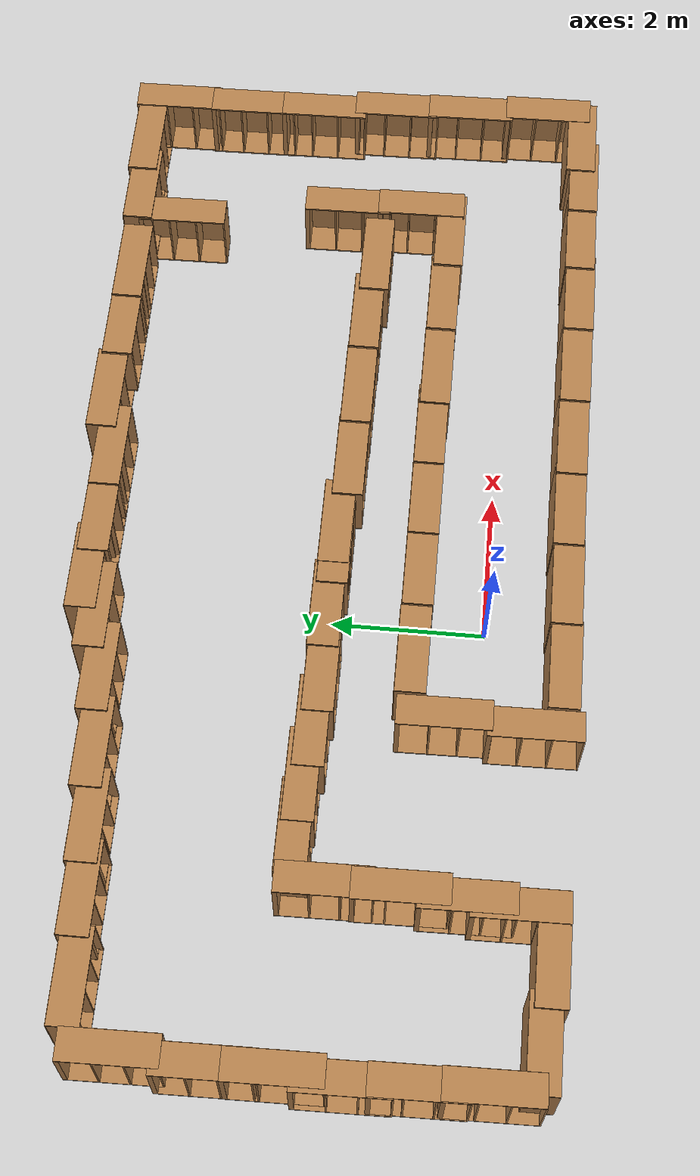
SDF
<sdf version="1.7">
 <world name="default">
  <light name="sun" type="directional">
   <pose>0 0 10 0 -0 0</pose>
   <diffuse>0.8 0.8 0.8 1</diffuse>
   <specular>0.2 0.2 0.2 1</specular>
   <attenuation>
    <range>1000</range>
    <constant>0.9</constant>
    <linear>0.01</linear>
    <quadratic>0.001</quadratic>
   </attenuation>
   <direction>-0.5 0.1 -0.9</direction>
   <spot><inner_angle>0</inner_angle><outer_angle>0</outer_angle><falloff>0</falloff></spot>
  </light>
  <model name="ground_plane">
   <static>1</static>
   <link name="link">
    <collision name="collision">
     <geometry><plane><normal>0 0 1</normal><size>100 100</size></plane></geometry>
     <surface>
      <contact><collide_bitmask>65535</collide_bitmask></contact>
      <friction><ode><mu>100</mu><mu2>50</mu2></ode></friction>
     </surface>
    </collision>
    <visual name="visual">
     <cast_shadows>0</cast_shadows>
     <geometry><plane><normal>0 0 1</normal><size>100 100</size></plane></geometry>
     <material>
      <script><uri>file://media/materials/scripts/gazebo.material</uri><name>Gazebo/Grey</name></script>
     </material>
    </visual>
   </link>
  </model>
  <gravity>0 0 -9.8</gravity>
  <magnetic_field>6e-06 2.3e-05 -4.2e-05</magnetic_field>
  <atmosphere type="adiabatic"/>
  <physics type="ode">
   <max_step_size>0.001</max_step_size>
   <real_time_factor>1</real_time_factor>
   <real_time_update_rate>1000</real_time_update_rate>
  </physics>
  <scene><ambient>0.4 0.4 0.4 1</ambient><background>0.7 0.7 0.7 1</background><shadows>1</shadows></scene>
  <audio><device>default</device></audio>
  <spherical_coordinates>
   <surface_model>EARTH_WGS84</surface_model>
   <latitude_deg>0</latitude_deg>
   <longitude_deg>0</longitude_deg>
   <elevation>0</elevation>
   <heading_deg>0</heading_deg>
  </spherical_coordinates>
  <model name="bookshelf">
   <static>1</static>
   <link name="link">
    <inertial><mass>1</mass></inertial>
    <collision name="back">
     <pose>0 0.005 0.6 0 -0 0</pose>
     <geometry><box><size>0.9 0.01 1.2</size></box></geometry>
    </collision>
    <visual name="visual1">
     <pose>0 0.005 0.6 0 -0 0</pose>
     <geometry><box><size>0.9 0.01 1.2</size></box></geometry>
     <material>
      <script><uri>file://media/materials/scripts/gazebo.material</uri><name>Gazebo/Wood</name></script>
     </material>
    </visual>
    <collision name="left_side">
     <pose>0.45 -0.195 0.6 0 -0 0</pose>
     <geometry><box><size>0.02 0.4 1.2</size></box></geometry>
    </collision>
    <visual name="visual2">
     <pose>0.45 -0.195 0.6 0 -0 0</pose>
     <geometry><box><size>0.02 0.4 1.2</size></box></geometry>
     <material>
      <script><uri>file://media/materials/scripts/gazebo.material</uri><name>Gazebo/Wood</name></script>
     </material>
    </visual>
    <collision name="right_side">
     <pose>-0.45 -0.195 0.6 0 -0 0</pose>
     <geometry><box><size>0.02 0.4 1.2</size></box></geometry>
    </collision>
    <visual name="visual3">
     <pose>-0.45 -0.195 0.6 0 -0 0</pose>
     <geometry><box><size>0.02 0.4 1.2</size></box></geometry>
     <material>
      <script><uri>file://media/materials/scripts/gazebo.material</uri><name>Gazebo/Wood</name></script>
     </material>
    </visual>
    <collision name="bottom">
     <pose>0 -0.195 0.03 0 -0 0</pose>
     <geometry><box><size>0.88 0.4 0.06</size></box></geometry>
    </collision>
    <visual name="visual4">
     <pose>0 -0.195 0.03 0 -0 0</pose>
     <geometry><box><size>0.88 0.4 0.06</size></box></geometry>
     <material>
      <script><uri>file://media/materials/scripts/gazebo.material</uri><name>Gazebo/Wood</name></script>
     </material>
    </visual>
    <collision name="top">
     <pose>0 -0.195 1.19 0 -0 0</pose>
     <geometry><box><size>0.88 0.4 0.02</size></box></geometry>
    </collision>
    <visual name="visual5">
     <pose>0 -0.195 1.19 0 -0 0</pose>
     <geometry><box><size>0.88 0.4 0.02</size></box></geometry>
     <material>
      <script><uri>file://media/materials/scripts/gazebo.material</uri><name>Gazebo/Wood</name></script>
     </material>
    </visual>
    <collision name="low_shelf">
     <pose>0 -0.195 0.43 0 -0 0</pose>
     <geometry><box><size>0.88 0.4 0.02</size></box></geometry>
    </collision>
    <visual name="visual6">
     <pose>0 -0.195 0.43 0 -0 0</pose>
     <geometry><box><size>0.88 0.4 0.02</size></box></geometry>
     <material>
      <script><uri>file://media/materials/scripts/gazebo.material</uri><name>Gazebo/Wood</name></script>
     </material>
    </visual>
    <collision name="high_shelf">
     <pose>0 -0.195 0.8 0 -0 0</pose>
     <geometry><box><size>0.88 0.4 0.02</size></box></geometry>
    </collision>
    <visual name="visual7">
     <pose>0 -0.195 0.8 0 -0 0</pose>
     <geometry><box><size>0.88 0.4 0.02</size></box></geometry>
     <material>
      <script><uri>file://media/materials/scripts/gazebo.material</uri><name>Gazebo/Wood</name></script>
     </material>
    </visual>
   </link>
   <pose>-0.039939 1.08937 0.469198 3.1373 1.52729 3.13696</pose>
  </model>
  <model name="bookshelf_clone">
   <static>1</static>
   <link name="link">
    <inertial><mass>1</mass></inertial>
    <collision name="back">
     <pose>0 0.005 0.6 0 -0 0</pose>
     <geometry><box><size>0.9 0.01 1.2</size></box></geometry>
    </collision>
    <visual name="visual1">
     <pose>0 0.005 0.6 0 -0 0</pose>
     <geometry><box><size>0.9 0.01 1.2</size></box></geometry>
     <material>
      <script><uri>file://media/materials/scripts/gazebo.material</uri><name>Gazebo/Wood</name></script>
     </material>
    </visual>
    <collision name="left_side">
     <pose>0.45 -0.195 0.6 0 -0 0</pose>
     <geometry><box><size>0.02 0.4 1.2</size></box></geometry>
    </collision>
    <visual name="visual2">
     <pose>0.45 -0.195 0.6 0 -0 0</pose>
     <geometry><box><size>0.02 0.4 1.2</size></box></geometry>
     <material>
      <script><uri>file://media/materials/scripts/gazebo.material</uri><name>Gazebo/Wood</name></script>
     </material>
    </visual>
    <collision name="right_side">
     <pose>-0.45 -0.195 0.6 0 -0 0</pose>
     <geometry><box><size>0.02 0.4 1.2</size></box></geometry>
    </collision>
    <visual name="visual3">
     <pose>-0.45 -0.195 0.6 0 -0 0</pose>
     <geometry><box><size>0.02 0.4 1.2</size></box></geometry>
     <material>
      <script><uri>file://media/materials/scripts/gazebo.material</uri><name>Gazebo/Wood</name></script>
     </material>
    </visual>
    <collision name="bottom">
     <pose>0 -0.195 0.03 0 -0 0</pose>
     <geometry><box><size>0.88 0.4 0.06</size></box></geometry>
    </collision>
    <visual name="visual4">
     <pose>0 -0.195 0.03 0 -0 0</pose>
     <geometry><box><size>0.88 0.4 0.06</size></box></geometry>
     <material>
      <script><uri>file://media/materials/scripts/gazebo.material</uri><name>Gazebo/Wood</name></script>
     </material>
    </visual>
    <collision name="top">
     <pose>0 -0.195 1.19 0 -0 0</pose>
     <geometry><box><size>0.88 0.4 0.02</size></box></geometry>
    </collision>
    <visual name="visual5">
     <pose>0 -0.195 1.19 0 -0 0</pose>
     <geometry><box><size>0.88 0.4 0.02</size></box></geometry>
     <material>
      <script><uri>file://media/materials/scripts/gazebo.material</uri><name>Gazebo/Wood</name></script>
     </material>
    </visual>
    <collision name="low_shelf">
     <pose>0 -0.195 0.43 0 -0 0</pose>
     <geometry><box><size>0.88 0.4 0.02</size></box></geometry>
    </collision>
    <visual name="visual6">
     <pose>0 -0.195 0.43 0 -0 0</pose>
     <geometry><box><size>0.88 0.4 0.02</size></box></geometry>
     <material>
      <script><uri>file://media/materials/scripts/gazebo.material</uri><name>Gazebo/Wood</name></script>
     </material>
    </visual>
    <collision name="high_shelf">
     <pose>0 -0.195 0.8 0 -0 0</pose>
     <geometry><box><size>0.88 0.4 0.02</size></box></geometry>
    </collision>
    <visual name="visual7">
     <pose>0 -0.195 0.8 0 -0 0</pose>
     <geometry><box><size>0.88 0.4 0.02</size></box></geometry>
     <material>
      <script><uri>file://media/materials/scripts/gazebo.material</uri><name>Gazebo/Wood</name></script>
     </material>
    </visual>
   </link>
   <pose>-1.23623 1.09859 0.469198 3.1373 1.52729 3.13696</pose>
  </model>
  <model name="bookshelf_clone_0">
   <static>1</static>
   <link name="link">
    <inertial><mass>1</mass></inertial>
    <collision name="back">
     <pose>0 0.005 0.6 0 -0 0</pose>
     <geometry><box><size>0.9 0.01 1.2</size></box></geometry>
    </collision>
    <visual name="visual1">
     <pose>0 0.005 0.6 0 -0 0</pose>
     <geometry><box><size>0.9 0.01 1.2</size></box></geometry>
     <material>
      <script><uri>file://media/materials/scripts/gazebo.material</uri><name>Gazebo/Wood</name></script>
     </material>
    </visual>
    <collision name="left_side">
     <pose>0.45 -0.195 0.6 0 -0 0</pose>
     <geometry><box><size>0.02 0.4 1.2</size></box></geometry>
    </collision>
    <visual name="visual2">
     <pose>0.45 -0.195 0.6 0 -0 0</pose>
     <geometry><box><size>0.02 0.4 1.2</size></box></geometry>
     <material>
      <script><uri>file://media/materials/scripts/gazebo.material</uri><name>Gazebo/Wood</name></script>
     </material>
    </visual>
    <collision name="right_side">
     <pose>-0.45 -0.195 0.6 0 -0 0</pose>
     <geometry><box><size>0.02 0.4 1.2</size></box></geometry>
    </collision>
    <visual name="visual3">
     <pose>-0.45 -0.195 0.6 0 -0 0</pose>
     <geometry><box><size>0.02 0.4 1.2</size></box></geometry>
     <material>
      <script><uri>file://media/materials/scripts/gazebo.material</uri><name>Gazebo/Wood</name></script>
     </material>
    </visual>
    <collision name="bottom">
     <pose>0 -0.195 0.03 0 -0 0</pose>
     <geometry><box><size>0.88 0.4 0.06</size></box></geometry>
    </collision>
    <visual name="visual4">
     <pose>0 -0.195 0.03 0 -0 0</pose>
     <geometry><box><size>0.88 0.4 0.06</size></box></geometry>
     <material>
      <script><uri>file://media/materials/scripts/gazebo.material</uri><name>Gazebo/Wood</name></script>
     </material>
    </visual>
    <collision name="top">
     <pose>0 -0.195 1.19 0 -0 0</pose>
     <geometry><box><size>0.88 0.4 0.02</size></box></geometry>
    </collision>
    <visual name="visual5">
     <pose>0 -0.195 1.19 0 -0 0</pose>
     <geometry><box><size>0.88 0.4 0.02</size></box></geometry>
     <material>
      <script><uri>file://media/materials/scripts/gazebo.material</uri><name>Gazebo/Wood</name></script>
     </material>
    </visual>
    <collision name="low_shelf">
     <pose>0 -0.195 0.43 0 -0 0</pose>
     <geometry><box><size>0.88 0.4 0.02</size></box></geometry>
    </collision>
    <visual name="visual6">
     <pose>0 -0.195 0.43 0 -0 0</pose>
     <geometry><box><size>0.88 0.4 0.02</size></box></geometry>
     <material>
      <script><uri>file://media/materials/scripts/gazebo.material</uri><name>Gazebo/Wood</name></script>
     </material>
    </visual>
    <collision name="high_shelf">
     <pose>0 -0.195 0.8 0 -0 0</pose>
     <geometry><box><size>0.88 0.4 0.02</size></box></geometry>
    </collision>
    <visual name="visual7">
     <pose>0 -0.195 0.8 0 -0 0</pose>
     <geometry><box><size>0.88 0.4 0.02</size></box></geometry>
     <material>
      <script><uri>file://media/materials/scripts/gazebo.material</uri><name>Gazebo/Wood</name></script>
     </material>
    </visual>
   </link>
   <pose>0.971842 1.08817 0.469198 3.1373 1.52729 3.13696</pose>
  </model>
  <model name="bookshelf_clone_1">
   <static>1</static>
   <link name="link">
    <inertial><mass>1</mass></inertial>
    <collision name="back">
     <pose>0 0.005 0.6 0 -0 0</pose>
     <geometry><box><size>0.9 0.01 1.2</size></box></geometry>
    </collision>
    <visual name="visual1">
     <pose>0 0.005 0.6 0 -0 0</pose>
     <geometry><box><size>0.9 0.01 1.2</size></box></geometry>
     <material>
      <script><uri>file://media/materials/scripts/gazebo.material</uri><name>Gazebo/Wood</name></script>
     </material>
    </visual>
    <collision name="left_side">
     <pose>0.45 -0.195 0.6 0 -0 0</pose>
     <geometry><box><size>0.02 0.4 1.2</size></box></geometry>
    </collision>
    <visual name="visual2">
     <pose>0.45 -0.195 0.6 0 -0 0</pose>
     <geometry><box><size>0.02 0.4 1.2</size></box></geometry>
     <material>
      <script><uri>file://media/materials/scripts/gazebo.material</uri><name>Gazebo/Wood</name></script>
     </material>
    </visual>
    <collision name="right_side">
     <pose>-0.45 -0.195 0.6 0 -0 0</pose>
     <geometry><box><size>0.02 0.4 1.2</size></box></geometry>
    </collision>
    <visual name="visual3">
     <pose>-0.45 -0.195 0.6 0 -0 0</pose>
     <geometry><box><size>0.02 0.4 1.2</size></box></geometry>
     <material>
      <script><uri>file://media/materials/scripts/gazebo.material</uri><name>Gazebo/Wood</name></script>
     </material>
    </visual>
    <collision name="bottom">
     <pose>0 -0.195 0.03 0 -0 0</pose>
     <geometry><box><size>0.88 0.4 0.06</size></box></geometry>
    </collision>
    <visual name="visual4">
     <pose>0 -0.195 0.03 0 -0 0</pose>
     <geometry><box><size>0.88 0.4 0.06</size></box></geometry>
     <material>
      <script><uri>file://media/materials/scripts/gazebo.material</uri><name>Gazebo/Wood</name></script>
     </material>
    </visual>
    <collision name="top">
     <pose>0 -0.195 1.19 0 -0 0</pose>
     <geometry><box><size>0.88 0.4 0.02</size></box></geometry>
    </collision>
    <visual name="visual5">
     <pose>0 -0.195 1.19 0 -0 0</pose>
     <geometry><box><size>0.88 0.4 0.02</size></box></geometry>
     <material>
      <script><uri>file://media/materials/scripts/gazebo.material</uri><name>Gazebo/Wood</name></script>
     </material>
    </visual>
    <collision name="low_shelf">
     <pose>0 -0.195 0.43 0 -0 0</pose>
     <geometry><box><size>0.88 0.4 0.02</size></box></geometry>
    </collision>
    <visual name="visual6">
     <pose>0 -0.195 0.43 0 -0 0</pose>
     <geometry><box><size>0.88 0.4 0.02</size></box></geometry>
     <material>
      <script><uri>file://media/materials/scripts/gazebo.material</uri><name>Gazebo/Wood</name></script>
     </material>
    </visual>
    <collision name="high_shelf">
     <pose>0 -0.195 0.8 0 -0 0</pose>
     <geometry><box><size>0.88 0.4 0.02</size></box></geometry>
    </collision>
    <visual name="visual7">
     <pose>0 -0.195 0.8 0 -0 0</pose>
     <geometry><box><size>0.88 0.4 0.02</size></box></geometry>
     <material>
      <script><uri>file://media/materials/scripts/gazebo.material</uri><name>Gazebo/Wood</name></script>
     </material>
    </visual>
   </link>
   <pose>1.99977 1.08853 0.469198 3.1373 1.52729 3.13696</pose>
  </model>
  <model name="bookshelf_clone_2">
   <static>1</static>
   <link name="link">
    <inertial><mass>1</mass></inertial>
    <collision name="back">
     <pose>0 0.005 0.6 0 -0 0</pose>
     <geometry><box><size>0.9 0.01 1.2</size></box></geometry>
    </collision>
    <visual name="visual1">
     <pose>0 0.005 0.6 0 -0 0</pose>
     <geometry><box><size>0.9 0.01 1.2</size></box></geometry>
     <material>
      <script><uri>file://media/materials/scripts/gazebo.material</uri><name>Gazebo/Wood</name></script>
     </material>
    </visual>
    <collision name="left_side">
     <pose>0.45 -0.195 0.6 0 -0 0</pose>
     <geometry><box><size>0.02 0.4 1.2</size></box></geometry>
    </collision>
    <visual name="visual2">
     <pose>0.45 -0.195 0.6 0 -0 0</pose>
     <geometry><box><size>0.02 0.4 1.2</size></box></geometry>
     <material>
      <script><uri>file://media/materials/scripts/gazebo.material</uri><name>Gazebo/Wood</name></script>
     </material>
    </visual>
    <collision name="right_side">
     <pose>-0.45 -0.195 0.6 0 -0 0</pose>
     <geometry><box><size>0.02 0.4 1.2</size></box></geometry>
    </collision>
    <visual name="visual3">
     <pose>-0.45 -0.195 0.6 0 -0 0</pose>
     <geometry><box><size>0.02 0.4 1.2</size></box></geometry>
     <material>
      <script><uri>file://media/materials/scripts/gazebo.material</uri><name>Gazebo/Wood</name></script>
     </material>
    </visual>
    <collision name="bottom">
     <pose>0 -0.195 0.03 0 -0 0</pose>
     <geometry><box><size>0.88 0.4 0.06</size></box></geometry>
    </collision>
    <visual name="visual4">
     <pose>0 -0.195 0.03 0 -0 0</pose>
     <geometry><box><size>0.88 0.4 0.06</size></box></geometry>
     <material>
      <script><uri>file://media/materials/scripts/gazebo.material</uri><name>Gazebo/Wood</name></script>
     </material>
    </visual>
    <collision name="top">
     <pose>0 -0.195 1.19 0 -0 0</pose>
     <geometry><box><size>0.88 0.4 0.02</size></box></geometry>
    </collision>
    <visual name="visual5">
     <pose>0 -0.195 1.19 0 -0 0</pose>
     <geometry><box><size>0.88 0.4 0.02</size></box></geometry>
     <material>
      <script><uri>file://media/materials/scripts/gazebo.material</uri><name>Gazebo/Wood</name></script>
     </material>
    </visual>
    <collision name="low_shelf">
     <pose>0 -0.195 0.43 0 -0 0</pose>
     <geometry><box><size>0.88 0.4 0.02</size></box></geometry>
    </collision>
    <visual name="visual6">
     <pose>0 -0.195 0.43 0 -0 0</pose>
     <geometry><box><size>0.88 0.4 0.02</size></box></geometry>
     <material>
      <script><uri>file://media/materials/scripts/gazebo.material</uri><name>Gazebo/Wood</name></script>
     </material>
    </visual>
    <collision name="high_shelf">
     <pose>0 -0.195 0.8 0 -0 0</pose>
     <geometry><box><size>0.88 0.4 0.02</size></box></geometry>
    </collision>
    <visual name="visual7">
     <pose>0 -0.195 0.8 0 -0 0</pose>
     <geometry><box><size>0.88 0.4 0.02</size></box></geometry>
     <material>
      <script><uri>file://media/materials/scripts/gazebo.material</uri><name>Gazebo/Wood</name></script>
     </material>
    </visual>
   </link>
   <pose>2.91076 1.0694 0.469198 3.1373 1.52729 3.13696</pose>
  </model>
  <model name="bookshelf_clone_3">
   <static>1</static>
   <link name="link">
    <inertial><mass>1</mass></inertial>
    <collision name="back">
     <pose>0 0.005 0.6 0 -0 0</pose>
     <geometry><box><size>0.9 0.01 1.2</size></box></geometry>
    </collision>
    <visual name="visual1">
     <pose>0 0.005 0.6 0 -0 0</pose>
     <geometry><box><size>0.9 0.01 1.2</size></box></geometry>
     <material>
      <script><uri>file://media/materials/scripts/gazebo.material</uri><name>Gazebo/Wood</name></script>
     </material>
    </visual>
    <collision name="left_side">
     <pose>0.45 -0.195 0.6 0 -0 0</pose>
     <geometry><box><size>0.02 0.4 1.2</size></box></geometry>
    </collision>
    <visual name="visual2">
     <pose>0.45 -0.195 0.6 0 -0 0</pose>
     <geometry><box><size>0.02 0.4 1.2</size></box></geometry>
     <material>
      <script><uri>file://media/materials/scripts/gazebo.material</uri><name>Gazebo/Wood</name></script>
     </material>
    </visual>
    <collision name="right_side">
     <pose>-0.45 -0.195 0.6 0 -0 0</pose>
     <geometry><box><size>0.02 0.4 1.2</size></box></geometry>
    </collision>
    <visual name="visual3">
     <pose>-0.45 -0.195 0.6 0 -0 0</pose>
     <geometry><box><size>0.02 0.4 1.2</size></box></geometry>
     <material>
      <script><uri>file://media/materials/scripts/gazebo.material</uri><name>Gazebo/Wood</name></script>
     </material>
    </visual>
    <collision name="bottom">
     <pose>0 -0.195 0.03 0 -0 0</pose>
     <geometry><box><size>0.88 0.4 0.06</size></box></geometry>
    </collision>
    <visual name="visual4">
     <pose>0 -0.195 0.03 0 -0 0</pose>
     <geometry><box><size>0.88 0.4 0.06</size></box></geometry>
     <material>
      <script><uri>file://media/materials/scripts/gazebo.material</uri><name>Gazebo/Wood</name></script>
     </material>
    </visual>
    <collision name="top">
     <pose>0 -0.195 1.19 0 -0 0</pose>
     <geometry><box><size>0.88 0.4 0.02</size></box></geometry>
    </collision>
    <visual name="visual5">
     <pose>0 -0.195 1.19 0 -0 0</pose>
     <geometry><box><size>0.88 0.4 0.02</size></box></geometry>
     <material>
      <script><uri>file://media/materials/scripts/gazebo.material</uri><name>Gazebo/Wood</name></script>
     </material>
    </visual>
    <collision name="low_shelf">
     <pose>0 -0.195 0.43 0 -0 0</pose>
     <geometry><box><size>0.88 0.4 0.02</size></box></geometry>
    </collision>
    <visual name="visual6">
     <pose>0 -0.195 0.43 0 -0 0</pose>
     <geometry><box><size>0.88 0.4 0.02</size></box></geometry>
     <material>
      <script><uri>file://media/materials/scripts/gazebo.material</uri><name>Gazebo/Wood</name></script>
     </material>
    </visual>
    <collision name="high_shelf">
     <pose>0 -0.195 0.8 0 -0 0</pose>
     <geometry><box><size>0.88 0.4 0.02</size></box></geometry>
    </collision>
    <visual name="visual7">
     <pose>0 -0.195 0.8 0 -0 0</pose>
     <geometry><box><size>0.88 0.4 0.02</size></box></geometry>
     <material>
      <script><uri>file://media/materials/scripts/gazebo.material</uri><name>Gazebo/Wood</name></script>
     </material>
    </visual>
   </link>
   <pose>4.07605 1.06263 0.469198 3.1373 1.52729 3.13696</pose>
  </model>
  <model name="bookshelf_clone_4">
   <static>1</static>
   <link name="link">
    <inertial><mass>1</mass></inertial>
    <collision name="back">
     <pose>0 0.005 0.6 0 -0 0</pose>
     <geometry><box><size>0.9 0.01 1.2</size></box></geometry>
    </collision>
    <visual name="visual1">
     <pose>0 0.005 0.6 0 -0 0</pose>
     <geometry><box><size>0.9 0.01 1.2</size></box></geometry>
     <material>
      <script><uri>file://media/materials/scripts/gazebo.material</uri><name>Gazebo/Wood</name></script>
     </material>
    </visual>
    <collision name="left_side">
     <pose>0.45 -0.195 0.6 0 -0 0</pose>
     <geometry><box><size>0.02 0.4 1.2</size></box></geometry>
    </collision>
    <visual name="visual2">
     <pose>0.45 -0.195 0.6 0 -0 0</pose>
     <geometry><box><size>0.02 0.4 1.2</size></box></geometry>
     <material>
      <script><uri>file://media/materials/scripts/gazebo.material</uri><name>Gazebo/Wood</name></script>
     </material>
    </visual>
    <collision name="right_side">
     <pose>-0.45 -0.195 0.6 0 -0 0</pose>
     <geometry><box><size>0.02 0.4 1.2</size></box></geometry>
    </collision>
    <visual name="visual3">
     <pose>-0.45 -0.195 0.6 0 -0 0</pose>
     <geometry><box><size>0.02 0.4 1.2</size></box></geometry>
     <material>
      <script><uri>file://media/materials/scripts/gazebo.material</uri><name>Gazebo/Wood</name></script>
     </material>
    </visual>
    <collision name="bottom">
     <pose>0 -0.195 0.03 0 -0 0</pose>
     <geometry><box><size>0.88 0.4 0.06</size></box></geometry>
    </collision>
    <visual name="visual4">
     <pose>0 -0.195 0.03 0 -0 0</pose>
     <geometry><box><size>0.88 0.4 0.06</size></box></geometry>
     <material>
      <script><uri>file://media/materials/scripts/gazebo.material</uri><name>Gazebo/Wood</name></script>
     </material>
    </visual>
    <collision name="top">
     <pose>0 -0.195 1.19 0 -0 0</pose>
     <geometry><box><size>0.88 0.4 0.02</size></box></geometry>
    </collision>
    <visual name="visual5">
     <pose>0 -0.195 1.19 0 -0 0</pose>
     <geometry><box><size>0.88 0.4 0.02</size></box></geometry>
     <material>
      <script><uri>file://media/materials/scripts/gazebo.material</uri><name>Gazebo/Wood</name></script>
     </material>
    </visual>
    <collision name="low_shelf">
     <pose>0 -0.195 0.43 0 -0 0</pose>
     <geometry><box><size>0.88 0.4 0.02</size></box></geometry>
    </collision>
    <visual name="visual6">
     <pose>0 -0.195 0.43 0 -0 0</pose>
     <geometry><box><size>0.88 0.4 0.02</size></box></geometry>
     <material>
      <script><uri>file://media/materials/scripts/gazebo.material</uri><name>Gazebo/Wood</name></script>
     </material>
    </visual>
    <collision name="high_shelf">
     <pose>0 -0.195 0.8 0 -0 0</pose>
     <geometry><box><size>0.88 0.4 0.02</size></box></geometry>
    </collision>
    <visual name="visual7">
     <pose>0 -0.195 0.8 0 -0 0</pose>
     <geometry><box><size>0.88 0.4 0.02</size></box></geometry>
     <material>
      <script><uri>file://media/materials/scripts/gazebo.material</uri><name>Gazebo/Wood</name></script>
     </material>
    </visual>
   </link>
   <pose>5.12004 1.03939 0.469198 3.1373 1.52729 3.13696</pose>
  </model>
  <model name="bookshelf_clone_clone">
   <static>1</static>
   <link name="link">
    <inertial><mass>1</mass></inertial>
    <collision name="back">
     <pose>0 0.005 0.6 0 -0 0</pose>
     <geometry><box><size>0.9 0.01 1.2</size></box></geometry>
    </collision>
    <visual name="visual1">
     <pose>0 0.005 0.6 0 -0 0</pose>
     <geometry><box><size>0.9 0.01 1.2</size></box></geometry>
     <material>
      <script><uri>file://media/materials/scripts/gazebo.material</uri><name>Gazebo/Wood</name></script>
     </material>
    </visual>
    <collision name="left_side">
     <pose>0.45 -0.195 0.6 0 -0 0</pose>
     <geometry><box><size>0.02 0.4 1.2</size></box></geometry>
    </collision>
    <visual name="visual2">
     <pose>0.45 -0.195 0.6 0 -0 0</pose>
     <geometry><box><size>0.02 0.4 1.2</size></box></geometry>
     <material>
      <script><uri>file://media/materials/scripts/gazebo.material</uri><name>Gazebo/Wood</name></script>
     </material>
    </visual>
    <collision name="right_side">
     <pose>-0.45 -0.195 0.6 0 -0 0</pose>
     <geometry><box><size>0.02 0.4 1.2</size></box></geometry>
    </collision>
    <visual name="visual3">
     <pose>-0.45 -0.195 0.6 0 -0 0</pose>
     <geometry><box><size>0.02 0.4 1.2</size></box></geometry>
     <material>
      <script><uri>file://media/materials/scripts/gazebo.material</uri><name>Gazebo/Wood</name></script>
     </material>
    </visual>
    <collision name="bottom">
     <pose>0 -0.195 0.03 0 -0 0</pose>
     <geometry><box><size>0.88 0.4 0.06</size></box></geometry>
    </collision>
    <visual name="visual4">
     <pose>0 -0.195 0.03 0 -0 0</pose>
     <geometry><box><size>0.88 0.4 0.06</size></box></geometry>
     <material>
      <script><uri>file://media/materials/scripts/gazebo.material</uri><name>Gazebo/Wood</name></script>
     </material>
    </visual>
    <collision name="top">
     <pose>0 -0.195 1.19 0 -0 0</pose>
     <geometry><box><size>0.88 0.4 0.02</size></box></geometry>
    </collision>
    <visual name="visual5">
     <pose>0 -0.195 1.19 0 -0 0</pose>
     <geometry><box><size>0.88 0.4 0.02</size></box></geometry>
     <material>
      <script><uri>file://media/materials/scripts/gazebo.material</uri><name>Gazebo/Wood</name></script>
     </material>
    </visual>
    <collision name="low_shelf">
     <pose>0 -0.195 0.43 0 -0 0</pose>
     <geometry><box><size>0.88 0.4 0.02</size></box></geometry>
    </collision>
    <visual name="visual6">
     <pose>0 -0.195 0.43 0 -0 0</pose>
     <geometry><box><size>0.88 0.4 0.02</size></box></geometry>
     <material>
      <script><uri>file://media/materials/scripts/gazebo.material</uri><name>Gazebo/Wood</name></script>
     </material>
    </visual>
    <collision name="high_shelf">
     <pose>0 -0.195 0.8 0 -0 0</pose>
     <geometry><box><size>0.88 0.4 0.02</size></box></geometry>
    </collision>
    <visual name="visual7">
     <pose>0 -0.195 0.8 0 -0 0</pose>
     <geometry><box><size>0.88 0.4 0.02</size></box></geometry>
     <material>
      <script><uri>file://media/materials/scripts/gazebo.material</uri><name>Gazebo/Wood</name></script>
     </material>
    </visual>
   </link>
   <pose>-1.31083 -0.80368 0.531222 3.1373 1.52729 3.13696</pose>
  </model>
  <model name="bookshelf_clone_clone_clone">
   <static>1</static>
   <link name="link">
    <inertial><mass>1</mass></inertial>
    <collision name="back">
     <pose>0 0.005 0.6 0 -0 0</pose>
     <geometry><box><size>0.9 0.01 1.2</size></box></geometry>
    </collision>
    <visual name="visual1">
     <pose>0 0.005 0.6 0 -0 0</pose>
     <geometry><box><size>0.9 0.01 1.2</size></box></geometry>
     <material>
      <script><uri>file://media/materials/scripts/gazebo.material</uri><name>Gazebo/Wood</name></script>
     </material>
    </visual>
    <collision name="left_side">
     <pose>0.45 -0.195 0.6 0 -0 0</pose>
     <geometry><box><size>0.02 0.4 1.2</size></box></geometry>
    </collision>
    <visual name="visual2">
     <pose>0.45 -0.195 0.6 0 -0 0</pose>
     <geometry><box><size>0.02 0.4 1.2</size></box></geometry>
     <material>
      <script><uri>file://media/materials/scripts/gazebo.material</uri><name>Gazebo/Wood</name></script>
     </material>
    </visual>
    <collision name="right_side">
     <pose>-0.45 -0.195 0.6 0 -0 0</pose>
     <geometry><box><size>0.02 0.4 1.2</size></box></geometry>
    </collision>
    <visual name="visual3">
     <pose>-0.45 -0.195 0.6 0 -0 0</pose>
     <geometry><box><size>0.02 0.4 1.2</size></box></geometry>
     <material>
      <script><uri>file://media/materials/scripts/gazebo.material</uri><name>Gazebo/Wood</name></script>
     </material>
    </visual>
    <collision name="bottom">
     <pose>0 -0.195 0.03 0 -0 0</pose>
     <geometry><box><size>0.88 0.4 0.06</size></box></geometry>
    </collision>
    <visual name="visual4">
     <pose>0 -0.195 0.03 0 -0 0</pose>
     <geometry><box><size>0.88 0.4 0.06</size></box></geometry>
     <material>
      <script><uri>file://media/materials/scripts/gazebo.material</uri><name>Gazebo/Wood</name></script>
     </material>
    </visual>
    <collision name="top">
     <pose>0 -0.195 1.19 0 -0 0</pose>
     <geometry><box><size>0.88 0.4 0.02</size></box></geometry>
    </collision>
    <visual name="visual5">
     <pose>0 -0.195 1.19 0 -0 0</pose>
     <geometry><box><size>0.88 0.4 0.02</size></box></geometry>
     <material>
      <script><uri>file://media/materials/scripts/gazebo.material</uri><name>Gazebo/Wood</name></script>
     </material>
    </visual>
    <collision name="low_shelf">
     <pose>0 -0.195 0.43 0 -0 0</pose>
     <geometry><box><size>0.88 0.4 0.02</size></box></geometry>
    </collision>
    <visual name="visual6">
     <pose>0 -0.195 0.43 0 -0 0</pose>
     <geometry><box><size>0.88 0.4 0.02</size></box></geometry>
     <material>
      <script><uri>file://media/materials/scripts/gazebo.material</uri><name>Gazebo/Wood</name></script>
     </material>
    </visual>
    <collision name="high_shelf">
     <pose>0 -0.195 0.8 0 -0 0</pose>
     <geometry><box><size>0.88 0.4 0.02</size></box></geometry>
    </collision>
    <visual name="visual7">
     <pose>0 -0.195 0.8 0 -0 0</pose>
     <geometry><box><size>0.88 0.4 0.02</size></box></geometry>
     <material>
      <script><uri>file://media/materials/scripts/gazebo.material</uri><name>Gazebo/Wood</name></script>
     </material>
    </visual>
   </link>
   <pose>-0.171859 -0.788269 0.531222 3.1373 1.52729 3.13696</pose>
  </model>
  <model name="bookshelf_clone_clone_clone_0">
   <static>1</static>
   <link name="link">
    <inertial><mass>1</mass></inertial>
    <collision name="back">
     <pose>0 0.005 0.6 0 -0 0</pose>
     <geometry><box><size>0.9 0.01 1.2</size></box></geometry>
    </collision>
    <visual name="visual1">
     <pose>0 0.005 0.6 0 -0 0</pose>
     <geometry><box><size>0.9 0.01 1.2</size></box></geometry>
     <material>
      <script><uri>file://media/materials/scripts/gazebo.material</uri><name>Gazebo/Wood</name></script>
     </material>
    </visual>
    <collision name="left_side">
     <pose>0.45 -0.195 0.6 0 -0 0</pose>
     <geometry><box><size>0.02 0.4 1.2</size></box></geometry>
    </collision>
    <visual name="visual2">
     <pose>0.45 -0.195 0.6 0 -0 0</pose>
     <geometry><box><size>0.02 0.4 1.2</size></box></geometry>
     <material>
      <script><uri>file://media/materials/scripts/gazebo.material</uri><name>Gazebo/Wood</name></script>
     </material>
    </visual>
    <collision name="right_side">
     <pose>-0.45 -0.195 0.6 0 -0 0</pose>
     <geometry><box><size>0.02 0.4 1.2</size></box></geometry>
    </collision>
    <visual name="visual3">
     <pose>-0.45 -0.195 0.6 0 -0 0</pose>
     <geometry><box><size>0.02 0.4 1.2</size></box></geometry>
     <material>
      <script><uri>file://media/materials/scripts/gazebo.material</uri><name>Gazebo/Wood</name></script>
     </material>
    </visual>
    <collision name="bottom">
     <pose>0 -0.195 0.03 0 -0 0</pose>
     <geometry><box><size>0.88 0.4 0.06</size></box></geometry>
    </collision>
    <visual name="visual4">
     <pose>0 -0.195 0.03 0 -0 0</pose>
     <geometry><box><size>0.88 0.4 0.06</size></box></geometry>
     <material>
      <script><uri>file://media/materials/scripts/gazebo.material</uri><name>Gazebo/Wood</name></script>
     </material>
    </visual>
    <collision name="top">
     <pose>0 -0.195 1.19 0 -0 0</pose>
     <geometry><box><size>0.88 0.4 0.02</size></box></geometry>
    </collision>
    <visual name="visual5">
     <pose>0 -0.195 1.19 0 -0 0</pose>
     <geometry><box><size>0.88 0.4 0.02</size></box></geometry>
     <material>
      <script><uri>file://media/materials/scripts/gazebo.material</uri><name>Gazebo/Wood</name></script>
     </material>
    </visual>
    <collision name="low_shelf">
     <pose>0 -0.195 0.43 0 -0 0</pose>
     <geometry><box><size>0.88 0.4 0.02</size></box></geometry>
    </collision>
    <visual name="visual6">
     <pose>0 -0.195 0.43 0 -0 0</pose>
     <geometry><box><size>0.88 0.4 0.02</size></box></geometry>
     <material>
      <script><uri>file://media/materials/scripts/gazebo.material</uri><name>Gazebo/Wood</name></script>
     </material>
    </visual>
    <collision name="high_shelf">
     <pose>0 -0.195 0.8 0 -0 0</pose>
     <geometry><box><size>0.88 0.4 0.02</size></box></geometry>
    </collision>
    <visual name="visual7">
     <pose>0 -0.195 0.8 0 -0 0</pose>
     <geometry><box><size>0.88 0.4 0.02</size></box></geometry>
     <material>
      <script><uri>file://media/materials/scripts/gazebo.material</uri><name>Gazebo/Wood</name></script>
     </material>
    </visual>
   </link>
   <pose>0.938619 -0.774846 0.531222 3.1373 1.52729 3.13696</pose>
  </model>
  <model name="bookshelf_clone_clone_clone_1">
   <static>1</static>
   <link name="link">
    <inertial><mass>1</mass></inertial>
    <collision name="back">
     <pose>0 0.005 0.6 0 -0 0</pose>
     <geometry><box><size>0.9 0.01 1.2</size></box></geometry>
    </collision>
    <visual name="visual1">
     <pose>0 0.005 0.6 0 -0 0</pose>
     <geometry><box><size>0.9 0.01 1.2</size></box></geometry>
     <material>
      <script><uri>file://media/materials/scripts/gazebo.material</uri><name>Gazebo/Wood</name></script>
     </material>
    </visual>
    <collision name="left_side">
     <pose>0.45 -0.195 0.6 0 -0 0</pose>
     <geometry><box><size>0.02 0.4 1.2</size></box></geometry>
    </collision>
    <visual name="visual2">
     <pose>0.45 -0.195 0.6 0 -0 0</pose>
     <geometry><box><size>0.02 0.4 1.2</size></box></geometry>
     <material>
      <script><uri>file://media/materials/scripts/gazebo.material</uri><name>Gazebo/Wood</name></script>
     </material>
    </visual>
    <collision name="right_side">
     <pose>-0.45 -0.195 0.6 0 -0 0</pose>
     <geometry><box><size>0.02 0.4 1.2</size></box></geometry>
    </collision>
    <visual name="visual3">
     <pose>-0.45 -0.195 0.6 0 -0 0</pose>
     <geometry><box><size>0.02 0.4 1.2</size></box></geometry>
     <material>
      <script><uri>file://media/materials/scripts/gazebo.material</uri><name>Gazebo/Wood</name></script>
     </material>
    </visual>
    <collision name="bottom">
     <pose>0 -0.195 0.03 0 -0 0</pose>
     <geometry><box><size>0.88 0.4 0.06</size></box></geometry>
    </collision>
    <visual name="visual4">
     <pose>0 -0.195 0.03 0 -0 0</pose>
     <geometry><box><size>0.88 0.4 0.06</size></box></geometry>
     <material>
      <script><uri>file://media/materials/scripts/gazebo.material</uri><name>Gazebo/Wood</name></script>
     </material>
    </visual>
    <collision name="top">
     <pose>0 -0.195 1.19 0 -0 0</pose>
     <geometry><box><size>0.88 0.4 0.02</size></box></geometry>
    </collision>
    <visual name="visual5">
     <pose>0 -0.195 1.19 0 -0 0</pose>
     <geometry><box><size>0.88 0.4 0.02</size></box></geometry>
     <material>
      <script><uri>file://media/materials/scripts/gazebo.material</uri><name>Gazebo/Wood</name></script>
     </material>
    </visual>
    <collision name="low_shelf">
     <pose>0 -0.195 0.43 0 -0 0</pose>
     <geometry><box><size>0.88 0.4 0.02</size></box></geometry>
    </collision>
    <visual name="visual6">
     <pose>0 -0.195 0.43 0 -0 0</pose>
     <geometry><box><size>0.88 0.4 0.02</size></box></geometry>
     <material>
      <script><uri>file://media/materials/scripts/gazebo.material</uri><name>Gazebo/Wood</name></script>
     </material>
    </visual>
    <collision name="high_shelf">
     <pose>0 -0.195 0.8 0 -0 0</pose>
     <geometry><box><size>0.88 0.4 0.02</size></box></geometry>
    </collision>
    <visual name="visual7">
     <pose>0 -0.195 0.8 0 -0 0</pose>
     <geometry><box><size>0.88 0.4 0.02</size></box></geometry>
     <material>
      <script><uri>file://media/materials/scripts/gazebo.material</uri><name>Gazebo/Wood</name></script>
     </material>
    </visual>
   </link>
   <pose>1.97036 -0.775682 0.531222 3.1373 1.52729 3.13696</pose>
  </model>
  <model name="bookshelf_clone_clone_clone_2">
   <static>1</static>
   <link name="link">
    <inertial><mass>1</mass></inertial>
    <collision name="back">
     <pose>0 0.005 0.6 0 -0 0</pose>
     <geometry><box><size>0.9 0.01 1.2</size></box></geometry>
    </collision>
    <visual name="visual1">
     <pose>0 0.005 0.6 0 -0 0</pose>
     <geometry><box><size>0.9 0.01 1.2</size></box></geometry>
     <material>
      <script><uri>file://media/materials/scripts/gazebo.material</uri><name>Gazebo/Wood</name></script>
     </material>
    </visual>
    <collision name="left_side">
     <pose>0.45 -0.195 0.6 0 -0 0</pose>
     <geometry><box><size>0.02 0.4 1.2</size></box></geometry>
    </collision>
    <visual name="visual2">
     <pose>0.45 -0.195 0.6 0 -0 0</pose>
     <geometry><box><size>0.02 0.4 1.2</size></box></geometry>
     <material>
      <script><uri>file://media/materials/scripts/gazebo.material</uri><name>Gazebo/Wood</name></script>
     </material>
    </visual>
    <collision name="right_side">
     <pose>-0.45 -0.195 0.6 0 -0 0</pose>
     <geometry><box><size>0.02 0.4 1.2</size></box></geometry>
    </collision>
    <visual name="visual3">
     <pose>-0.45 -0.195 0.6 0 -0 0</pose>
     <geometry><box><size>0.02 0.4 1.2</size></box></geometry>
     <material>
      <script><uri>file://media/materials/scripts/gazebo.material</uri><name>Gazebo/Wood</name></script>
     </material>
    </visual>
    <collision name="bottom">
     <pose>0 -0.195 0.03 0 -0 0</pose>
     <geometry><box><size>0.88 0.4 0.06</size></box></geometry>
    </collision>
    <visual name="visual4">
     <pose>0 -0.195 0.03 0 -0 0</pose>
     <geometry><box><size>0.88 0.4 0.06</size></box></geometry>
     <material>
      <script><uri>file://media/materials/scripts/gazebo.material</uri><name>Gazebo/Wood</name></script>
     </material>
    </visual>
    <collision name="top">
     <pose>0 -0.195 1.19 0 -0 0</pose>
     <geometry><box><size>0.88 0.4 0.02</size></box></geometry>
    </collision>
    <visual name="visual5">
     <pose>0 -0.195 1.19 0 -0 0</pose>
     <geometry><box><size>0.88 0.4 0.02</size></box></geometry>
     <material>
      <script><uri>file://media/materials/scripts/gazebo.material</uri><name>Gazebo/Wood</name></script>
     </material>
    </visual>
    <collision name="low_shelf">
     <pose>0 -0.195 0.43 0 -0 0</pose>
     <geometry><box><size>0.88 0.4 0.02</size></box></geometry>
    </collision>
    <visual name="visual6">
     <pose>0 -0.195 0.43 0 -0 0</pose>
     <geometry><box><size>0.88 0.4 0.02</size></box></geometry>
     <material>
      <script><uri>file://media/materials/scripts/gazebo.material</uri><name>Gazebo/Wood</name></script>
     </material>
    </visual>
    <collision name="high_shelf">
     <pose>0 -0.195 0.8 0 -0 0</pose>
     <geometry><box><size>0.88 0.4 0.02</size></box></geometry>
    </collision>
    <visual name="visual7">
     <pose>0 -0.195 0.8 0 -0 0</pose>
     <geometry><box><size>0.88 0.4 0.02</size></box></geometry>
     <material>
      <script><uri>file://media/materials/scripts/gazebo.material</uri><name>Gazebo/Wood</name></script>
     </material>
    </visual>
   </link>
   <pose>3.07146 -0.782007 0.531222 3.1373 1.52729 3.13696</pose>
  </model>
  <model name="bookshelf_clone_clone_clone_3">
   <static>1</static>
   <link name="link">
    <inertial><mass>1</mass></inertial>
    <collision name="back">
     <pose>0 0.005 0.6 0 -0 0</pose>
     <geometry><box><size>0.9 0.01 1.2</size></box></geometry>
    </collision>
    <visual name="visual1">
     <pose>0 0.005 0.6 0 -0 0</pose>
     <geometry><box><size>0.9 0.01 1.2</size></box></geometry>
     <material>
      <script><uri>file://media/materials/scripts/gazebo.material</uri><name>Gazebo/Wood</name></script>
     </material>
    </visual>
    <collision name="left_side">
     <pose>0.45 -0.195 0.6 0 -0 0</pose>
     <geometry><box><size>0.02 0.4 1.2</size></box></geometry>
    </collision>
    <visual name="visual2">
     <pose>0.45 -0.195 0.6 0 -0 0</pose>
     <geometry><box><size>0.02 0.4 1.2</size></box></geometry>
     <material>
      <script><uri>file://media/materials/scripts/gazebo.material</uri><name>Gazebo/Wood</name></script>
     </material>
    </visual>
    <collision name="right_side">
     <pose>-0.45 -0.195 0.6 0 -0 0</pose>
     <geometry><box><size>0.02 0.4 1.2</size></box></geometry>
    </collision>
    <visual name="visual3">
     <pose>-0.45 -0.195 0.6 0 -0 0</pose>
     <geometry><box><size>0.02 0.4 1.2</size></box></geometry>
     <material>
      <script><uri>file://media/materials/scripts/gazebo.material</uri><name>Gazebo/Wood</name></script>
     </material>
    </visual>
    <collision name="bottom">
     <pose>0 -0.195 0.03 0 -0 0</pose>
     <geometry><box><size>0.88 0.4 0.06</size></box></geometry>
    </collision>
    <visual name="visual4">
     <pose>0 -0.195 0.03 0 -0 0</pose>
     <geometry><box><size>0.88 0.4 0.06</size></box></geometry>
     <material>
      <script><uri>file://media/materials/scripts/gazebo.material</uri><name>Gazebo/Wood</name></script>
     </material>
    </visual>
    <collision name="top">
     <pose>0 -0.195 1.19 0 -0 0</pose>
     <geometry><box><size>0.88 0.4 0.02</size></box></geometry>
    </collision>
    <visual name="visual5">
     <pose>0 -0.195 1.19 0 -0 0</pose>
     <geometry><box><size>0.88 0.4 0.02</size></box></geometry>
     <material>
      <script><uri>file://media/materials/scripts/gazebo.material</uri><name>Gazebo/Wood</name></script>
     </material>
    </visual>
    <collision name="low_shelf">
     <pose>0 -0.195 0.43 0 -0 0</pose>
     <geometry><box><size>0.88 0.4 0.02</size></box></geometry>
    </collision>
    <visual name="visual6">
     <pose>0 -0.195 0.43 0 -0 0</pose>
     <geometry><box><size>0.88 0.4 0.02</size></box></geometry>
     <material>
      <script><uri>file://media/materials/scripts/gazebo.material</uri><name>Gazebo/Wood</name></script>
     </material>
    </visual>
    <collision name="high_shelf">
     <pose>0 -0.195 0.8 0 -0 0</pose>
     <geometry><box><size>0.88 0.4 0.02</size></box></geometry>
    </collision>
    <visual name="visual7">
     <pose>0 -0.195 0.8 0 -0 0</pose>
     <geometry><box><size>0.88 0.4 0.02</size></box></geometry>
     <material>
      <script><uri>file://media/materials/scripts/gazebo.material</uri><name>Gazebo/Wood</name></script>
     </material>
    </visual>
   </link>
   <pose>4.1959 -0.786375 0.531222 3.1373 1.52729 3.13696</pose>
  </model>
  <model name="bookshelf_clone_clone_clone_4">
   <static>1</static>
   <link name="link">
    <inertial><mass>1</mass></inertial>
    <collision name="back">
     <pose>0 0.005 0.6 0 -0 0</pose>
     <geometry><box><size>0.9 0.01 1.2</size></box></geometry>
    </collision>
    <visual name="visual1">
     <pose>0 0.005 0.6 0 -0 0</pose>
     <geometry><box><size>0.9 0.01 1.2</size></box></geometry>
     <material>
      <script><uri>file://media/materials/scripts/gazebo.material</uri><name>Gazebo/Wood</name></script>
     </material>
    </visual>
    <collision name="left_side">
     <pose>0.45 -0.195 0.6 0 -0 0</pose>
     <geometry><box><size>0.02 0.4 1.2</size></box></geometry>
    </collision>
    <visual name="visual2">
     <pose>0.45 -0.195 0.6 0 -0 0</pose>
     <geometry><box><size>0.02 0.4 1.2</size></box></geometry>
     <material>
      <script><uri>file://media/materials/scripts/gazebo.material</uri><name>Gazebo/Wood</name></script>
     </material>
    </visual>
    <collision name="right_side">
     <pose>-0.45 -0.195 0.6 0 -0 0</pose>
     <geometry><box><size>0.02 0.4 1.2</size></box></geometry>
    </collision>
    <visual name="visual3">
     <pose>-0.45 -0.195 0.6 0 -0 0</pose>
     <geometry><box><size>0.02 0.4 1.2</size></box></geometry>
     <material>
      <script><uri>file://media/materials/scripts/gazebo.material</uri><name>Gazebo/Wood</name></script>
     </material>
    </visual>
    <collision name="bottom">
     <pose>0 -0.195 0.03 0 -0 0</pose>
     <geometry><box><size>0.88 0.4 0.06</size></box></geometry>
    </collision>
    <visual name="visual4">
     <pose>0 -0.195 0.03 0 -0 0</pose>
     <geometry><box><size>0.88 0.4 0.06</size></box></geometry>
     <material>
      <script><uri>file://media/materials/scripts/gazebo.material</uri><name>Gazebo/Wood</name></script>
     </material>
    </visual>
    <collision name="top">
     <pose>0 -0.195 1.19 0 -0 0</pose>
     <geometry><box><size>0.88 0.4 0.02</size></box></geometry>
    </collision>
    <visual name="visual5">
     <pose>0 -0.195 1.19 0 -0 0</pose>
     <geometry><box><size>0.88 0.4 0.02</size></box></geometry>
     <material>
      <script><uri>file://media/materials/scripts/gazebo.material</uri><name>Gazebo/Wood</name></script>
     </material>
    </visual>
    <collision name="low_shelf">
     <pose>0 -0.195 0.43 0 -0 0</pose>
     <geometry><box><size>0.88 0.4 0.02</size></box></geometry>
    </collision>
    <visual name="visual6">
     <pose>0 -0.195 0.43 0 -0 0</pose>
     <geometry><box><size>0.88 0.4 0.02</size></box></geometry>
     <material>
      <script><uri>file://media/materials/scripts/gazebo.material</uri><name>Gazebo/Wood</name></script>
     </material>
    </visual>
    <collision name="high_shelf">
     <pose>0 -0.195 0.8 0 -0 0</pose>
     <geometry><box><size>0.88 0.4 0.02</size></box></geometry>
    </collision>
    <visual name="visual7">
     <pose>0 -0.195 0.8 0 -0 0</pose>
     <geometry><box><size>0.88 0.4 0.02</size></box></geometry>
     <material>
      <script><uri>file://media/materials/scripts/gazebo.material</uri><name>Gazebo/Wood</name></script>
     </material>
    </visual>
   </link>
   <pose>5.18438 -0.771863 0.531222 3.1373 1.52729 3.13696</pose>
  </model>
  <model name="bookshelf_clone_clone_clone_5">
   <static>1</static>
   <link name="link">
    <inertial><mass>1</mass></inertial>
    <collision name="back">
     <pose>0 0.005 0.6 0 -0 0</pose>
     <geometry><box><size>0.9 0.01 1.2</size></box></geometry>
    </collision>
    <visual name="visual1">
     <pose>0 0.005 0.6 0 -0 0</pose>
     <geometry><box><size>0.9 0.01 1.2</size></box></geometry>
     <material>
      <script><uri>file://media/materials/scripts/gazebo.material</uri><name>Gazebo/Wood</name></script>
     </material>
    </visual>
    <collision name="left_side">
     <pose>0.45 -0.195 0.6 0 -0 0</pose>
     <geometry><box><size>0.02 0.4 1.2</size></box></geometry>
    </collision>
    <visual name="visual2">
     <pose>0.45 -0.195 0.6 0 -0 0</pose>
     <geometry><box><size>0.02 0.4 1.2</size></box></geometry>
     <material>
      <script><uri>file://media/materials/scripts/gazebo.material</uri><name>Gazebo/Wood</name></script>
     </material>
    </visual>
    <collision name="right_side">
     <pose>-0.45 -0.195 0.6 0 -0 0</pose>
     <geometry><box><size>0.02 0.4 1.2</size></box></geometry>
    </collision>
    <visual name="visual3">
     <pose>-0.45 -0.195 0.6 0 -0 0</pose>
     <geometry><box><size>0.02 0.4 1.2</size></box></geometry>
     <material>
      <script><uri>file://media/materials/scripts/gazebo.material</uri><name>Gazebo/Wood</name></script>
     </material>
    </visual>
    <collision name="bottom">
     <pose>0 -0.195 0.03 0 -0 0</pose>
     <geometry><box><size>0.88 0.4 0.06</size></box></geometry>
    </collision>
    <visual name="visual4">
     <pose>0 -0.195 0.03 0 -0 0</pose>
     <geometry><box><size>0.88 0.4 0.06</size></box></geometry>
     <material>
      <script><uri>file://media/materials/scripts/gazebo.material</uri><name>Gazebo/Wood</name></script>
     </material>
    </visual>
    <collision name="top">
     <pose>0 -0.195 1.19 0 -0 0</pose>
     <geometry><box><size>0.88 0.4 0.02</size></box></geometry>
    </collision>
    <visual name="visual5">
     <pose>0 -0.195 1.19 0 -0 0</pose>
     <geometry><box><size>0.88 0.4 0.02</size></box></geometry>
     <material>
      <script><uri>file://media/materials/scripts/gazebo.material</uri><name>Gazebo/Wood</name></script>
     </material>
    </visual>
    <collision name="low_shelf">
     <pose>0 -0.195 0.43 0 -0 0</pose>
     <geometry><box><size>0.88 0.4 0.02</size></box></geometry>
    </collision>
    <visual name="visual6">
     <pose>0 -0.195 0.43 0 -0 0</pose>
     <geometry><box><size>0.88 0.4 0.02</size></box></geometry>
     <material>
      <script><uri>file://media/materials/scripts/gazebo.material</uri><name>Gazebo/Wood</name></script>
     </material>
    </visual>
    <collision name="high_shelf">
     <pose>0 -0.195 0.8 0 -0 0</pose>
     <geometry><box><size>0.88 0.4 0.02</size></box></geometry>
    </collision>
    <visual name="visual7">
     <pose>0 -0.195 0.8 0 -0 0</pose>
     <geometry><box><size>0.88 0.4 0.02</size></box></geometry>
     <material>
      <script><uri>file://media/materials/scripts/gazebo.material</uri><name>Gazebo/Wood</name></script>
     </material>
    </visual>
   </link>
   <pose>-1.34326 -0.066098 0.486113 -1.58898 1.52729 3.13696</pose>
  </model>
  <model name="bookshelf_clone_clone_clone_5_clone">
   <static>1</static>
   <link name="link">
    <inertial><mass>1</mass></inertial>
    <collision name="back">
     <pose>0 0.005 0.6 0 -0 0</pose>
     <geometry><box><size>0.9 0.01 1.2</size></box></geometry>
    </collision>
    <visual name="visual1">
     <pose>0 0.005 0.6 0 -0 0</pose>
     <geometry><box><size>0.9 0.01 1.2</size></box></geometry>
     <material>
      <script><uri>file://media/materials/scripts/gazebo.material</uri><name>Gazebo/Wood</name></script>
     </material>
    </visual>
    <collision name="left_side">
     <pose>0.45 -0.195 0.6 0 -0 0</pose>
     <geometry><box><size>0.02 0.4 1.2</size></box></geometry>
    </collision>
    <visual name="visual2">
     <pose>0.45 -0.195 0.6 0 -0 0</pose>
     <geometry><box><size>0.02 0.4 1.2</size></box></geometry>
     <material>
      <script><uri>file://media/materials/scripts/gazebo.material</uri><name>Gazebo/Wood</name></script>
     </material>
    </visual>
    <collision name="right_side">
     <pose>-0.45 -0.195 0.6 0 -0 0</pose>
     <geometry><box><size>0.02 0.4 1.2</size></box></geometry>
    </collision>
    <visual name="visual3">
     <pose>-0.45 -0.195 0.6 0 -0 0</pose>
     <geometry><box><size>0.02 0.4 1.2</size></box></geometry>
     <material>
      <script><uri>file://media/materials/scripts/gazebo.material</uri><name>Gazebo/Wood</name></script>
     </material>
    </visual>
    <collision name="bottom">
     <pose>0 -0.195 0.03 0 -0 0</pose>
     <geometry><box><size>0.88 0.4 0.06</size></box></geometry>
    </collision>
    <visual name="visual4">
     <pose>0 -0.195 0.03 0 -0 0</pose>
     <geometry><box><size>0.88 0.4 0.06</size></box></geometry>
     <material>
      <script><uri>file://media/materials/scripts/gazebo.material</uri><name>Gazebo/Wood</name></script>
     </material>
    </visual>
    <collision name="top">
     <pose>0 -0.195 1.19 0 -0 0</pose>
     <geometry><box><size>0.88 0.4 0.02</size></box></geometry>
    </collision>
    <visual name="visual5">
     <pose>0 -0.195 1.19 0 -0 0</pose>
     <geometry><box><size>0.88 0.4 0.02</size></box></geometry>
     <material>
      <script><uri>file://media/materials/scripts/gazebo.material</uri><name>Gazebo/Wood</name></script>
     </material>
    </visual>
    <collision name="low_shelf">
     <pose>0 -0.195 0.43 0 -0 0</pose>
     <geometry><box><size>0.88 0.4 0.02</size></box></geometry>
    </collision>
    <visual name="visual6">
     <pose>0 -0.195 0.43 0 -0 0</pose>
     <geometry><box><size>0.88 0.4 0.02</size></box></geometry>
     <material>
      <script><uri>file://media/materials/scripts/gazebo.material</uri><name>Gazebo/Wood</name></script>
     </material>
    </visual>
    <collision name="high_shelf">
     <pose>0 -0.195 0.8 0 -0 0</pose>
     <geometry><box><size>0.88 0.4 0.02</size></box></geometry>
    </collision>
    <visual name="visual7">
     <pose>0 -0.195 0.8 0 -0 0</pose>
     <geometry><box><size>0.88 0.4 0.02</size></box></geometry>
     <material>
      <script><uri>file://media/materials/scripts/gazebo.material</uri><name>Gazebo/Wood</name></script>
     </material>
    </visual>
   </link>
   <pose>-1.30319 1.06466 0.531222 -1.58898 1.52729 3.13696</pose>
  </model>
  <model name="bookshelf_clone_clone_clone_5_clone_0">
   <static>1</static>
   <link name="link">
    <inertial><mass>1</mass></inertial>
    <collision name="back">
     <pose>0 0.005 0.6 0 -0 0</pose>
     <geometry><box><size>0.9 0.01 1.2</size></box></geometry>
    </collision>
    <visual name="visual1">
     <pose>0 0.005 0.6 0 -0 0</pose>
     <geometry><box><size>0.9 0.01 1.2</size></box></geometry>
     <material>
      <script><uri>file://media/materials/scripts/gazebo.material</uri><name>Gazebo/Wood</name></script>
     </material>
    </visual>
    <collision name="left_side">
     <pose>0.45 -0.195 0.6 0 -0 0</pose>
     <geometry><box><size>0.02 0.4 1.2</size></box></geometry>
    </collision>
    <visual name="visual2">
     <pose>0.45 -0.195 0.6 0 -0 0</pose>
     <geometry><box><size>0.02 0.4 1.2</size></box></geometry>
     <material>
      <script><uri>file://media/materials/scripts/gazebo.material</uri><name>Gazebo/Wood</name></script>
     </material>
    </visual>
    <collision name="right_side">
     <pose>-0.45 -0.195 0.6 0 -0 0</pose>
     <geometry><box><size>0.02 0.4 1.2</size></box></geometry>
    </collision>
    <visual name="visual3">
     <pose>-0.45 -0.195 0.6 0 -0 0</pose>
     <geometry><box><size>0.02 0.4 1.2</size></box></geometry>
     <material>
      <script><uri>file://media/materials/scripts/gazebo.material</uri><name>Gazebo/Wood</name></script>
     </material>
    </visual>
    <collision name="bottom">
     <pose>0 -0.195 0.03 0 -0 0</pose>
     <geometry><box><size>0.88 0.4 0.06</size></box></geometry>
    </collision>
    <visual name="visual4">
     <pose>0 -0.195 0.03 0 -0 0</pose>
     <geometry><box><size>0.88 0.4 0.06</size></box></geometry>
     <material>
      <script><uri>file://media/materials/scripts/gazebo.material</uri><name>Gazebo/Wood</name></script>
     </material>
    </visual>
    <collision name="top">
     <pose>0 -0.195 1.19 0 -0 0</pose>
     <geometry><box><size>0.88 0.4 0.02</size></box></geometry>
    </collision>
    <visual name="visual5">
     <pose>0 -0.195 1.19 0 -0 0</pose>
     <geometry><box><size>0.88 0.4 0.02</size></box></geometry>
     <material>
      <script><uri>file://media/materials/scripts/gazebo.material</uri><name>Gazebo/Wood</name></script>
     </material>
    </visual>
    <collision name="low_shelf">
     <pose>0 -0.195 0.43 0 -0 0</pose>
     <geometry><box><size>0.88 0.4 0.02</size></box></geometry>
    </collision>
    <visual name="visual6">
     <pose>0 -0.195 0.43 0 -0 0</pose>
     <geometry><box><size>0.88 0.4 0.02</size></box></geometry>
     <material>
      <script><uri>file://media/materials/scripts/gazebo.material</uri><name>Gazebo/Wood</name></script>
     </material>
    </visual>
    <collision name="high_shelf">
     <pose>0 -0.195 0.8 0 -0 0</pose>
     <geometry><box><size>0.88 0.4 0.02</size></box></geometry>
    </collision>
    <visual name="visual7">
     <pose>0 -0.195 0.8 0 -0 0</pose>
     <geometry><box><size>0.88 0.4 0.02</size></box></geometry>
     <material>
      <script><uri>file://media/materials/scripts/gazebo.material</uri><name>Gazebo/Wood</name></script>
     </material>
    </visual>
   </link>
   <pose>6.292 1.87692 0.482938 -1.58898 1.52729 3.13696</pose>
  </model>
  <model name="bookshelf_clone_clone_clone_5_clone_1">
   <static>1</static>
   <link name="link">
    <inertial><mass>1</mass></inertial>
    <collision name="back">
     <pose>0 0.005 0.6 0 -0 0</pose>
     <geometry><box><size>0.9 0.01 1.2</size></box></geometry>
    </collision>
    <visual name="visual1">
     <pose>0 0.005 0.6 0 -0 0</pose>
     <geometry><box><size>0.9 0.01 1.2</size></box></geometry>
     <material>
      <script><uri>file://media/materials/scripts/gazebo.material</uri><name>Gazebo/Wood</name></script>
     </material>
    </visual>
    <collision name="left_side">
     <pose>0.45 -0.195 0.6 0 -0 0</pose>
     <geometry><box><size>0.02 0.4 1.2</size></box></geometry>
    </collision>
    <visual name="visual2">
     <pose>0.45 -0.195 0.6 0 -0 0</pose>
     <geometry><box><size>0.02 0.4 1.2</size></box></geometry>
     <material>
      <script><uri>file://media/materials/scripts/gazebo.material</uri><name>Gazebo/Wood</name></script>
     </material>
    </visual>
    <collision name="right_side">
     <pose>-0.45 -0.195 0.6 0 -0 0</pose>
     <geometry><box><size>0.02 0.4 1.2</size></box></geometry>
    </collision>
    <visual name="visual3">
     <pose>-0.45 -0.195 0.6 0 -0 0</pose>
     <geometry><box><size>0.02 0.4 1.2</size></box></geometry>
     <material>
      <script><uri>file://media/materials/scripts/gazebo.material</uri><name>Gazebo/Wood</name></script>
     </material>
    </visual>
    <collision name="bottom">
     <pose>0 -0.195 0.03 0 -0 0</pose>
     <geometry><box><size>0.88 0.4 0.06</size></box></geometry>
    </collision>
    <visual name="visual4">
     <pose>0 -0.195 0.03 0 -0 0</pose>
     <geometry><box><size>0.88 0.4 0.06</size></box></geometry>
     <material>
      <script><uri>file://media/materials/scripts/gazebo.material</uri><name>Gazebo/Wood</name></script>
     </material>
    </visual>
    <collision name="top">
     <pose>0 -0.195 1.19 0 -0 0</pose>
     <geometry><box><size>0.88 0.4 0.02</size></box></geometry>
    </collision>
    <visual name="visual5">
     <pose>0 -0.195 1.19 0 -0 0</pose>
     <geometry><box><size>0.88 0.4 0.02</size></box></geometry>
     <material>
      <script><uri>file://media/materials/scripts/gazebo.material</uri><name>Gazebo/Wood</name></script>
     </material>
    </visual>
    <collision name="low_shelf">
     <pose>0 -0.195 0.43 0 -0 0</pose>
     <geometry><box><size>0.88 0.4 0.02</size></box></geometry>
    </collision>
    <visual name="visual6">
     <pose>0 -0.195 0.43 0 -0 0</pose>
     <geometry><box><size>0.88 0.4 0.02</size></box></geometry>
     <material>
      <script><uri>file://media/materials/scripts/gazebo.material</uri><name>Gazebo/Wood</name></script>
     </material>
    </visual>
    <collision name="high_shelf">
     <pose>0 -0.195 0.8 0 -0 0</pose>
     <geometry><box><size>0.88 0.4 0.02</size></box></geometry>
    </collision>
    <visual name="visual7">
     <pose>0 -0.195 0.8 0 -0 0</pose>
     <geometry><box><size>0.88 0.4 0.02</size></box></geometry>
     <material>
      <script><uri>file://media/materials/scripts/gazebo.material</uri><name>Gazebo/Wood</name></script>
     </material>
    </visual>
   </link>
   <pose>5.88732 5.20047 0.482938 -1.58898 1.52729 3.13696</pose>
  </model>
  <model name="bookshelf_clone_clone_clone_5_clone_2">
   <static>1</static>
   <link name="link">
    <inertial><mass>1</mass></inertial>
    <collision name="back">
     <pose>0 0.005 0.6 0 -0 0</pose>
     <geometry><box><size>0.9 0.01 1.2</size></box></geometry>
    </collision>
    <visual name="visual1">
     <pose>0 0.005 0.6 0 -0 0</pose>
     <geometry><box><size>0.9 0.01 1.2</size></box></geometry>
     <material>
      <script><uri>file://media/materials/scripts/gazebo.material</uri><name>Gazebo/Wood</name></script>
     </material>
    </visual>
    <collision name="left_side">
     <pose>0.45 -0.195 0.6 0 -0 0</pose>
     <geometry><box><size>0.02 0.4 1.2</size></box></geometry>
    </collision>
    <visual name="visual2">
     <pose>0.45 -0.195 0.6 0 -0 0</pose>
     <geometry><box><size>0.02 0.4 1.2</size></box></geometry>
     <material>
      <script><uri>file://media/materials/scripts/gazebo.material</uri><name>Gazebo/Wood</name></script>
     </material>
    </visual>
    <collision name="right_side">
     <pose>-0.45 -0.195 0.6 0 -0 0</pose>
     <geometry><box><size>0.02 0.4 1.2</size></box></geometry>
    </collision>
    <visual name="visual3">
     <pose>-0.45 -0.195 0.6 0 -0 0</pose>
     <geometry><box><size>0.02 0.4 1.2</size></box></geometry>
     <material>
      <script><uri>file://media/materials/scripts/gazebo.material</uri><name>Gazebo/Wood</name></script>
     </material>
    </visual>
    <collision name="bottom">
     <pose>0 -0.195 0.03 0 -0 0</pose>
     <geometry><box><size>0.88 0.4 0.06</size></box></geometry>
    </collision>
    <visual name="visual4">
     <pose>0 -0.195 0.03 0 -0 0</pose>
     <geometry><box><size>0.88 0.4 0.06</size></box></geometry>
     <material>
      <script><uri>file://media/materials/scripts/gazebo.material</uri><name>Gazebo/Wood</name></script>
     </material>
    </visual>
    <collision name="top">
     <pose>0 -0.195 1.19 0 -0 0</pose>
     <geometry><box><size>0.88 0.4 0.02</size></box></geometry>
    </collision>
    <visual name="visual5">
     <pose>0 -0.195 1.19 0 -0 0</pose>
     <geometry><box><size>0.88 0.4 0.02</size></box></geometry>
     <material>
      <script><uri>file://media/materials/scripts/gazebo.material</uri><name>Gazebo/Wood</name></script>
     </material>
    </visual>
    <collision name="low_shelf">
     <pose>0 -0.195 0.43 0 -0 0</pose>
     <geometry><box><size>0.88 0.4 0.02</size></box></geometry>
    </collision>
    <visual name="visual6">
     <pose>0 -0.195 0.43 0 -0 0</pose>
     <geometry><box><size>0.88 0.4 0.02</size></box></geometry>
     <material>
      <script><uri>file://media/materials/scripts/gazebo.material</uri><name>Gazebo/Wood</name></script>
     </material>
    </visual>
    <collision name="high_shelf">
     <pose>0 -0.195 0.8 0 -0 0</pose>
     <geometry><box><size>0.88 0.4 0.02</size></box></geometry>
    </collision>
    <visual name="visual7">
     <pose>0 -0.195 0.8 0 -0 0</pose>
     <geometry><box><size>0.88 0.4 0.02</size></box></geometry>
     <material>
      <script><uri>file://media/materials/scripts/gazebo.material</uri><name>Gazebo/Wood</name></script>
     </material>
    </visual>
   </link>
   <pose>8.09522 0.177478 0.482938 -1.58898 1.52729 3.13696</pose>
  </model>
  <model name="bookshelf_clone_clone_clone_5_clone_3">
   <static>1</static>
   <link name="link">
    <inertial><mass>1</mass></inertial>
    <collision name="back">
     <pose>0 0.005 0.6 0 -0 0</pose>
     <geometry><box><size>0.9 0.01 1.2</size></box></geometry>
    </collision>
    <visual name="visual1">
     <pose>0 0.005 0.6 0 -0 0</pose>
     <geometry><box><size>0.9 0.01 1.2</size></box></geometry>
     <material>
      <script><uri>file://media/materials/scripts/gazebo.material</uri><name>Gazebo/Wood</name></script>
     </material>
    </visual>
    <collision name="left_side">
     <pose>0.45 -0.195 0.6 0 -0 0</pose>
     <geometry><box><size>0.02 0.4 1.2</size></box></geometry>
    </collision>
    <visual name="visual2">
     <pose>0.45 -0.195 0.6 0 -0 0</pose>
     <geometry><box><size>0.02 0.4 1.2</size></box></geometry>
     <material>
      <script><uri>file://media/materials/scripts/gazebo.material</uri><name>Gazebo/Wood</name></script>
     </material>
    </visual>
    <collision name="right_side">
     <pose>-0.45 -0.195 0.6 0 -0 0</pose>
     <geometry><box><size>0.02 0.4 1.2</size></box></geometry>
    </collision>
    <visual name="visual3">
     <pose>-0.45 -0.195 0.6 0 -0 0</pose>
     <geometry><box><size>0.02 0.4 1.2</size></box></geometry>
     <material>
      <script><uri>file://media/materials/scripts/gazebo.material</uri><name>Gazebo/Wood</name></script>
     </material>
    </visual>
    <collision name="bottom">
     <pose>0 -0.195 0.03 0 -0 0</pose>
     <geometry><box><size>0.88 0.4 0.06</size></box></geometry>
    </collision>
    <visual name="visual4">
     <pose>0 -0.195 0.03 0 -0 0</pose>
     <geometry><box><size>0.88 0.4 0.06</size></box></geometry>
     <material>
      <script><uri>file://media/materials/scripts/gazebo.material</uri><name>Gazebo/Wood</name></script>
     </material>
    </visual>
    <collision name="top">
     <pose>0 -0.195 1.19 0 -0 0</pose>
     <geometry><box><size>0.88 0.4 0.02</size></box></geometry>
    </collision>
    <visual name="visual5">
     <pose>0 -0.195 1.19 0 -0 0</pose>
     <geometry><box><size>0.88 0.4 0.02</size></box></geometry>
     <material>
      <script><uri>file://media/materials/scripts/gazebo.material</uri><name>Gazebo/Wood</name></script>
     </material>
    </visual>
    <collision name="low_shelf">
     <pose>0 -0.195 0.43 0 -0 0</pose>
     <geometry><box><size>0.88 0.4 0.02</size></box></geometry>
    </collision>
    <visual name="visual6">
     <pose>0 -0.195 0.43 0 -0 0</pose>
     <geometry><box><size>0.88 0.4 0.02</size></box></geometry>
     <material>
      <script><uri>file://media/materials/scripts/gazebo.material</uri><name>Gazebo/Wood</name></script>
     </material>
    </visual>
    <collision name="high_shelf">
     <pose>0 -0.195 0.8 0 -0 0</pose>
     <geometry><box><size>0.88 0.4 0.02</size></box></geometry>
    </collision>
    <visual name="visual7">
     <pose>0 -0.195 0.8 0 -0 0</pose>
     <geometry><box><size>0.88 0.4 0.02</size></box></geometry>
     <material>
      <script><uri>file://media/materials/scripts/gazebo.material</uri><name>Gazebo/Wood</name></script>
     </material>
    </visual>
   </link>
   <pose>8.02683 1.28732 0.482938 -1.58898 1.52729 3.13696</pose>
  </model>
  <model name="bookshelf_clone_clone_clone_4_clone">
   <static>1</static>
   <link name="link">
    <inertial><mass>1</mass></inertial>
    <collision name="back">
     <pose>0 0.005 0.6 0 -0 0</pose>
     <geometry><box><size>0.9 0.01 1.2</size></box></geometry>
    </collision>
    <visual name="visual1">
     <pose>0 0.005 0.6 0 -0 0</pose>
     <geometry><box><size>0.9 0.01 1.2</size></box></geometry>
     <material>
      <script><uri>file://media/materials/scripts/gazebo.material</uri><name>Gazebo/Wood</name></script>
     </material>
    </visual>
    <collision name="left_side">
     <pose>0.45 -0.195 0.6 0 -0 0</pose>
     <geometry><box><size>0.02 0.4 1.2</size></box></geometry>
    </collision>
    <visual name="visual2">
     <pose>0.45 -0.195 0.6 0 -0 0</pose>
     <geometry><box><size>0.02 0.4 1.2</size></box></geometry>
     <material>
      <script><uri>file://media/materials/scripts/gazebo.material</uri><name>Gazebo/Wood</name></script>
     </material>
    </visual>
    <collision name="right_side">
     <pose>-0.45 -0.195 0.6 0 -0 0</pose>
     <geometry><box><size>0.02 0.4 1.2</size></box></geometry>
    </collision>
    <visual name="visual3">
     <pose>-0.45 -0.195 0.6 0 -0 0</pose>
     <geometry><box><size>0.02 0.4 1.2</size></box></geometry>
     <material>
      <script><uri>file://media/materials/scripts/gazebo.material</uri><name>Gazebo/Wood</name></script>
     </material>
    </visual>
    <collision name="bottom">
     <pose>0 -0.195 0.03 0 -0 0</pose>
     <geometry><box><size>0.88 0.4 0.06</size></box></geometry>
    </collision>
    <visual name="visual4">
     <pose>0 -0.195 0.03 0 -0 0</pose>
     <geometry><box><size>0.88 0.4 0.06</size></box></geometry>
     <material>
      <script><uri>file://media/materials/scripts/gazebo.material</uri><name>Gazebo/Wood</name></script>
     </material>
    </visual>
    <collision name="top">
     <pose>0 -0.195 1.19 0 -0 0</pose>
     <geometry><box><size>0.88 0.4 0.02</size></box></geometry>
    </collision>
    <visual name="visual5">
     <pose>0 -0.195 1.19 0 -0 0</pose>
     <geometry><box><size>0.88 0.4 0.02</size></box></geometry>
     <material>
      <script><uri>file://media/materials/scripts/gazebo.material</uri><name>Gazebo/Wood</name></script>
     </material>
    </visual>
    <collision name="low_shelf">
     <pose>0 -0.195 0.43 0 -0 0</pose>
     <geometry><box><size>0.88 0.4 0.02</size></box></geometry>
    </collision>
    <visual name="visual6">
     <pose>0 -0.195 0.43 0 -0 0</pose>
     <geometry><box><size>0.88 0.4 0.02</size></box></geometry>
     <material>
      <script><uri>file://media/materials/scripts/gazebo.material</uri><name>Gazebo/Wood</name></script>
     </material>
    </visual>
    <collision name="high_shelf">
     <pose>0 -0.195 0.8 0 -0 0</pose>
     <geometry><box><size>0.88 0.4 0.02</size></box></geometry>
    </collision>
    <visual name="visual7">
     <pose>0 -0.195 0.8 0 -0 0</pose>
     <geometry><box><size>0.88 0.4 0.02</size></box></geometry>
     <material>
      <script><uri>file://media/materials/scripts/gazebo.material</uri><name>Gazebo/Wood</name></script>
     </material>
    </visual>
   </link>
   <pose>6.15092 -0.777255 0.531222 3.1373 1.52729 3.13696</pose>
  </model>
  <model name="bookshelf_clone_clone_clone_4_clone_0">
   <static>1</static>
   <link name="link">
    <inertial><mass>1</mass></inertial>
    <collision name="back">
     <pose>0 0.005 0.6 0 -0 0</pose>
     <geometry><box><size>0.9 0.01 1.2</size></box></geometry>
    </collision>
    <visual name="visual1">
     <pose>0 0.005 0.6 0 -0 0</pose>
     <geometry><box><size>0.9 0.01 1.2</size></box></geometry>
     <material>
      <script><uri>file://media/materials/scripts/gazebo.material</uri><name>Gazebo/Wood</name></script>
     </material>
    </visual>
    <collision name="left_side">
     <pose>0.45 -0.195 0.6 0 -0 0</pose>
     <geometry><box><size>0.02 0.4 1.2</size></box></geometry>
    </collision>
    <visual name="visual2">
     <pose>0.45 -0.195 0.6 0 -0 0</pose>
     <geometry><box><size>0.02 0.4 1.2</size></box></geometry>
     <material>
      <script><uri>file://media/materials/scripts/gazebo.material</uri><name>Gazebo/Wood</name></script>
     </material>
    </visual>
    <collision name="right_side">
     <pose>-0.45 -0.195 0.6 0 -0 0</pose>
     <geometry><box><size>0.02 0.4 1.2</size></box></geometry>
    </collision>
    <visual name="visual3">
     <pose>-0.45 -0.195 0.6 0 -0 0</pose>
     <geometry><box><size>0.02 0.4 1.2</size></box></geometry>
     <material>
      <script><uri>file://media/materials/scripts/gazebo.material</uri><name>Gazebo/Wood</name></script>
     </material>
    </visual>
    <collision name="bottom">
     <pose>0 -0.195 0.03 0 -0 0</pose>
     <geometry><box><size>0.88 0.4 0.06</size></box></geometry>
    </collision>
    <visual name="visual4">
     <pose>0 -0.195 0.03 0 -0 0</pose>
     <geometry><box><size>0.88 0.4 0.06</size></box></geometry>
     <material>
      <script><uri>file://media/materials/scripts/gazebo.material</uri><name>Gazebo/Wood</name></script>
     </material>
    </visual>
    <collision name="top">
     <pose>0 -0.195 1.19 0 -0 0</pose>
     <geometry><box><size>0.88 0.4 0.02</size></box></geometry>
    </collision>
    <visual name="visual5">
     <pose>0 -0.195 1.19 0 -0 0</pose>
     <geometry><box><size>0.88 0.4 0.02</size></box></geometry>
     <material>
      <script><uri>file://media/materials/scripts/gazebo.material</uri><name>Gazebo/Wood</name></script>
     </material>
    </visual>
    <collision name="low_shelf">
     <pose>0 -0.195 0.43 0 -0 0</pose>
     <geometry><box><size>0.88 0.4 0.02</size></box></geometry>
    </collision>
    <visual name="visual6">
     <pose>0 -0.195 0.43 0 -0 0</pose>
     <geometry><box><size>0.88 0.4 0.02</size></box></geometry>
     <material>
      <script><uri>file://media/materials/scripts/gazebo.material</uri><name>Gazebo/Wood</name></script>
     </material>
    </visual>
    <collision name="high_shelf">
     <pose>0 -0.195 0.8 0 -0 0</pose>
     <geometry><box><size>0.88 0.4 0.02</size></box></geometry>
    </collision>
    <visual name="visual7">
     <pose>0 -0.195 0.8 0 -0 0</pose>
     <geometry><box><size>0.88 0.4 0.02</size></box></geometry>
     <material>
      <script><uri>file://media/materials/scripts/gazebo.material</uri><name>Gazebo/Wood</name></script>
     </material>
    </visual>
   </link>
   <pose>6.83748 -0.726629 0.531222 3.1373 1.52729 3.13696</pose>
  </model>
  <model name="bookshelf_clone_clone_clone_5_clone_3_clone">
   <static>1</static>
   <link name="link">
    <inertial><mass>1</mass></inertial>
    <collision name="back">
     <pose>0 0.005 0.6 0 -0 0</pose>
     <geometry><box><size>0.9 0.01 1.2</size></box></geometry>
    </collision>
    <visual name="visual1">
     <pose>0 0.005 0.6 0 -0 0</pose>
     <geometry><box><size>0.9 0.01 1.2</size></box></geometry>
     <material>
      <script><uri>file://media/materials/scripts/gazebo.material</uri><name>Gazebo/Wood</name></script>
     </material>
    </visual>
    <collision name="left_side">
     <pose>0.45 -0.195 0.6 0 -0 0</pose>
     <geometry><box><size>0.02 0.4 1.2</size></box></geometry>
    </collision>
    <visual name="visual2">
     <pose>0.45 -0.195 0.6 0 -0 0</pose>
     <geometry><box><size>0.02 0.4 1.2</size></box></geometry>
     <material>
      <script><uri>file://media/materials/scripts/gazebo.material</uri><name>Gazebo/Wood</name></script>
     </material>
    </visual>
    <collision name="right_side">
     <pose>-0.45 -0.195 0.6 0 -0 0</pose>
     <geometry><box><size>0.02 0.4 1.2</size></box></geometry>
    </collision>
    <visual name="visual3">
     <pose>-0.45 -0.195 0.6 0 -0 0</pose>
     <geometry><box><size>0.02 0.4 1.2</size></box></geometry>
     <material>
      <script><uri>file://media/materials/scripts/gazebo.material</uri><name>Gazebo/Wood</name></script>
     </material>
    </visual>
    <collision name="bottom">
     <pose>0 -0.195 0.03 0 -0 0</pose>
     <geometry><box><size>0.88 0.4 0.06</size></box></geometry>
    </collision>
    <visual name="visual4">
     <pose>0 -0.195 0.03 0 -0 0</pose>
     <geometry><box><size>0.88 0.4 0.06</size></box></geometry>
     <material>
      <script><uri>file://media/materials/scripts/gazebo.material</uri><name>Gazebo/Wood</name></script>
     </material>
    </visual>
    <collision name="top">
     <pose>0 -0.195 1.19 0 -0 0</pose>
     <geometry><box><size>0.88 0.4 0.02</size></box></geometry>
    </collision>
    <visual name="visual5">
     <pose>0 -0.195 1.19 0 -0 0</pose>
     <geometry><box><size>0.88 0.4 0.02</size></box></geometry>
     <material>
      <script><uri>file://media/materials/scripts/gazebo.material</uri><name>Gazebo/Wood</name></script>
     </material>
    </visual>
    <collision name="low_shelf">
     <pose>0 -0.195 0.43 0 -0 0</pose>
     <geometry><box><size>0.88 0.4 0.02</size></box></geometry>
    </collision>
    <visual name="visual6">
     <pose>0 -0.195 0.43 0 -0 0</pose>
     <geometry><box><size>0.88 0.4 0.02</size></box></geometry>
     <material>
      <script><uri>file://media/materials/scripts/gazebo.material</uri><name>Gazebo/Wood</name></script>
     </material>
    </visual>
    <collision name="high_shelf">
     <pose>0 -0.195 0.8 0 -0 0</pose>
     <geometry><box><size>0.88 0.4 0.02</size></box></geometry>
    </collision>
    <visual name="visual7">
     <pose>0 -0.195 0.8 0 -0 0</pose>
     <geometry><box><size>0.88 0.4 0.02</size></box></geometry>
     <material>
      <script><uri>file://media/materials/scripts/gazebo.material</uri><name>Gazebo/Wood</name></script>
     </material>
    </visual>
   </link>
   <pose>7.99287 2.34294 0.482938 -1.58898 1.52729 3.13696</pose>
  </model>
  <model name="bookshelf_clone_clone_clone_5_clone_3_clone_0">
   <static>1</static>
   <link name="link">
    <inertial><mass>1</mass></inertial>
    <collision name="back">
     <pose>0 0.005 0.6 0 -0 0</pose>
     <geometry><box><size>0.9 0.01 1.2</size></box></geometry>
    </collision>
    <visual name="visual1">
     <pose>0 0.005 0.6 0 -0 0</pose>
     <geometry><box><size>0.9 0.01 1.2</size></box></geometry>
     <material>
      <script><uri>file://media/materials/scripts/gazebo.material</uri><name>Gazebo/Wood</name></script>
     </material>
    </visual>
    <collision name="left_side">
     <pose>0.45 -0.195 0.6 0 -0 0</pose>
     <geometry><box><size>0.02 0.4 1.2</size></box></geometry>
    </collision>
    <visual name="visual2">
     <pose>0.45 -0.195 0.6 0 -0 0</pose>
     <geometry><box><size>0.02 0.4 1.2</size></box></geometry>
     <material>
      <script><uri>file://media/materials/scripts/gazebo.material</uri><name>Gazebo/Wood</name></script>
     </material>
    </visual>
    <collision name="right_side">
     <pose>-0.45 -0.195 0.6 0 -0 0</pose>
     <geometry><box><size>0.02 0.4 1.2</size></box></geometry>
    </collision>
    <visual name="visual3">
     <pose>-0.45 -0.195 0.6 0 -0 0</pose>
     <geometry><box><size>0.02 0.4 1.2</size></box></geometry>
     <material>
      <script><uri>file://media/materials/scripts/gazebo.material</uri><name>Gazebo/Wood</name></script>
     </material>
    </visual>
    <collision name="bottom">
     <pose>0 -0.195 0.03 0 -0 0</pose>
     <geometry><box><size>0.88 0.4 0.06</size></box></geometry>
    </collision>
    <visual name="visual4">
     <pose>0 -0.195 0.03 0 -0 0</pose>
     <geometry><box><size>0.88 0.4 0.06</size></box></geometry>
     <material>
      <script><uri>file://media/materials/scripts/gazebo.material</uri><name>Gazebo/Wood</name></script>
     </material>
    </visual>
    <collision name="top">
     <pose>0 -0.195 1.19 0 -0 0</pose>
     <geometry><box><size>0.88 0.4 0.02</size></box></geometry>
    </collision>
    <visual name="visual5">
     <pose>0 -0.195 1.19 0 -0 0</pose>
     <geometry><box><size>0.88 0.4 0.02</size></box></geometry>
     <material>
      <script><uri>file://media/materials/scripts/gazebo.material</uri><name>Gazebo/Wood</name></script>
     </material>
    </visual>
    <collision name="low_shelf">
     <pose>0 -0.195 0.43 0 -0 0</pose>
     <geometry><box><size>0.88 0.4 0.02</size></box></geometry>
    </collision>
    <visual name="visual6">
     <pose>0 -0.195 0.43 0 -0 0</pose>
     <geometry><box><size>0.88 0.4 0.02</size></box></geometry>
     <material>
      <script><uri>file://media/materials/scripts/gazebo.material</uri><name>Gazebo/Wood</name></script>
     </material>
    </visual>
    <collision name="high_shelf">
     <pose>0 -0.195 0.8 0 -0 0</pose>
     <geometry><box><size>0.88 0.4 0.02</size></box></geometry>
    </collision>
    <visual name="visual7">
     <pose>0 -0.195 0.8 0 -0 0</pose>
     <geometry><box><size>0.88 0.4 0.02</size></box></geometry>
     <material>
      <script><uri>file://media/materials/scripts/gazebo.material</uri><name>Gazebo/Wood</name></script>
     </material>
    </visual>
   </link>
   <pose>7.89296 3.39109 0.482938 -1.58898 1.52729 3.13696</pose>
  </model>
  <model name="bookshelf_clone_clone_clone_5_clone_3_clone_1">
   <static>1</static>
   <link name="link">
    <inertial><mass>1</mass></inertial>
    <collision name="back">
     <pose>0 0.005 0.6 0 -0 0</pose>
     <geometry><box><size>0.9 0.01 1.2</size></box></geometry>
    </collision>
    <visual name="visual1">
     <pose>0 0.005 0.6 0 -0 0</pose>
     <geometry><box><size>0.9 0.01 1.2</size></box></geometry>
     <material>
      <script><uri>file://media/materials/scripts/gazebo.material</uri><name>Gazebo/Wood</name></script>
     </material>
    </visual>
    <collision name="left_side">
     <pose>0.45 -0.195 0.6 0 -0 0</pose>
     <geometry><box><size>0.02 0.4 1.2</size></box></geometry>
    </collision>
    <visual name="visual2">
     <pose>0.45 -0.195 0.6 0 -0 0</pose>
     <geometry><box><size>0.02 0.4 1.2</size></box></geometry>
     <material>
      <script><uri>file://media/materials/scripts/gazebo.material</uri><name>Gazebo/Wood</name></script>
     </material>
    </visual>
    <collision name="right_side">
     <pose>-0.45 -0.195 0.6 0 -0 0</pose>
     <geometry><box><size>0.02 0.4 1.2</size></box></geometry>
    </collision>
    <visual name="visual3">
     <pose>-0.45 -0.195 0.6 0 -0 0</pose>
     <geometry><box><size>0.02 0.4 1.2</size></box></geometry>
     <material>
      <script><uri>file://media/materials/scripts/gazebo.material</uri><name>Gazebo/Wood</name></script>
     </material>
    </visual>
    <collision name="bottom">
     <pose>0 -0.195 0.03 0 -0 0</pose>
     <geometry><box><size>0.88 0.4 0.06</size></box></geometry>
    </collision>
    <visual name="visual4">
     <pose>0 -0.195 0.03 0 -0 0</pose>
     <geometry><box><size>0.88 0.4 0.06</size></box></geometry>
     <material>
      <script><uri>file://media/materials/scripts/gazebo.material</uri><name>Gazebo/Wood</name></script>
     </material>
    </visual>
    <collision name="top">
     <pose>0 -0.195 1.19 0 -0 0</pose>
     <geometry><box><size>0.88 0.4 0.02</size></box></geometry>
    </collision>
    <visual name="visual5">
     <pose>0 -0.195 1.19 0 -0 0</pose>
     <geometry><box><size>0.88 0.4 0.02</size></box></geometry>
     <material>
      <script><uri>file://media/materials/scripts/gazebo.material</uri><name>Gazebo/Wood</name></script>
     </material>
    </visual>
    <collision name="low_shelf">
     <pose>0 -0.195 0.43 0 -0 0</pose>
     <geometry><box><size>0.88 0.4 0.02</size></box></geometry>
    </collision>
    <visual name="visual6">
     <pose>0 -0.195 0.43 0 -0 0</pose>
     <geometry><box><size>0.88 0.4 0.02</size></box></geometry>
     <material>
      <script><uri>file://media/materials/scripts/gazebo.material</uri><name>Gazebo/Wood</name></script>
     </material>
    </visual>
    <collision name="high_shelf">
     <pose>0 -0.195 0.8 0 -0 0</pose>
     <geometry><box><size>0.88 0.4 0.02</size></box></geometry>
    </collision>
    <visual name="visual7">
     <pose>0 -0.195 0.8 0 -0 0</pose>
     <geometry><box><size>0.88 0.4 0.02</size></box></geometry>
     <material>
      <script><uri>file://media/materials/scripts/gazebo.material</uri><name>Gazebo/Wood</name></script>
     </material>
    </visual>
   </link>
   <pose>7.87619 4.4114 0.482938 -1.58898 1.52729 3.13696</pose>
  </model>
  <model name="bookshelf_clone_clone_clone_5_clone_3_clone_2">
   <static>1</static>
   <link name="link">
    <inertial><mass>1</mass></inertial>
    <collision name="back">
     <pose>0 0.005 0.6 0 -0 0</pose>
     <geometry><box><size>0.9 0.01 1.2</size></box></geometry>
    </collision>
    <visual name="visual1">
     <pose>0 0.005 0.6 0 -0 0</pose>
     <geometry><box><size>0.9 0.01 1.2</size></box></geometry>
     <material>
      <script><uri>file://media/materials/scripts/gazebo.material</uri><name>Gazebo/Wood</name></script>
     </material>
    </visual>
    <collision name="left_side">
     <pose>0.45 -0.195 0.6 0 -0 0</pose>
     <geometry><box><size>0.02 0.4 1.2</size></box></geometry>
    </collision>
    <visual name="visual2">
     <pose>0.45 -0.195 0.6 0 -0 0</pose>
     <geometry><box><size>0.02 0.4 1.2</size></box></geometry>
     <material>
      <script><uri>file://media/materials/scripts/gazebo.material</uri><name>Gazebo/Wood</name></script>
     </material>
    </visual>
    <collision name="right_side">
     <pose>-0.45 -0.195 0.6 0 -0 0</pose>
     <geometry><box><size>0.02 0.4 1.2</size></box></geometry>
    </collision>
    <visual name="visual3">
     <pose>-0.45 -0.195 0.6 0 -0 0</pose>
     <geometry><box><size>0.02 0.4 1.2</size></box></geometry>
     <material>
      <script><uri>file://media/materials/scripts/gazebo.material</uri><name>Gazebo/Wood</name></script>
     </material>
    </visual>
    <collision name="bottom">
     <pose>0 -0.195 0.03 0 -0 0</pose>
     <geometry><box><size>0.88 0.4 0.06</size></box></geometry>
    </collision>
    <visual name="visual4">
     <pose>0 -0.195 0.03 0 -0 0</pose>
     <geometry><box><size>0.88 0.4 0.06</size></box></geometry>
     <material>
      <script><uri>file://media/materials/scripts/gazebo.material</uri><name>Gazebo/Wood</name></script>
     </material>
    </visual>
    <collision name="top">
     <pose>0 -0.195 1.19 0 -0 0</pose>
     <geometry><box><size>0.88 0.4 0.02</size></box></geometry>
    </collision>
    <visual name="visual5">
     <pose>0 -0.195 1.19 0 -0 0</pose>
     <geometry><box><size>0.88 0.4 0.02</size></box></geometry>
     <material>
      <script><uri>file://media/materials/scripts/gazebo.material</uri><name>Gazebo/Wood</name></script>
     </material>
    </visual>
    <collision name="low_shelf">
     <pose>0 -0.195 0.43 0 -0 0</pose>
     <geometry><box><size>0.88 0.4 0.02</size></box></geometry>
    </collision>
    <visual name="visual6">
     <pose>0 -0.195 0.43 0 -0 0</pose>
     <geometry><box><size>0.88 0.4 0.02</size></box></geometry>
     <material>
      <script><uri>file://media/materials/scripts/gazebo.material</uri><name>Gazebo/Wood</name></script>
     </material>
    </visual>
    <collision name="high_shelf">
     <pose>0 -0.195 0.8 0 -0 0</pose>
     <geometry><box><size>0.88 0.4 0.02</size></box></geometry>
    </collision>
    <visual name="visual7">
     <pose>0 -0.195 0.8 0 -0 0</pose>
     <geometry><box><size>0.88 0.4 0.02</size></box></geometry>
     <material>
      <script><uri>file://media/materials/scripts/gazebo.material</uri><name>Gazebo/Wood</name></script>
     </material>
    </visual>
   </link>
   <pose>7.87494 5.49145 0.482938 -1.58898 1.52729 3.13696</pose>
  </model>
  <model name="bookshelf_clone_clone_clone_4_clone_1">
   <static>1</static>
   <link name="link">
    <inertial><mass>1</mass></inertial>
    <collision name="back">
     <pose>0 0.005 0.6 0 -0 0</pose>
     <geometry><box><size>0.9 0.01 1.2</size></box></geometry>
    </collision>
    <visual name="visual1">
     <pose>0 0.005 0.6 0 -0 0</pose>
     <geometry><box><size>0.9 0.01 1.2</size></box></geometry>
     <material>
      <script><uri>file://media/materials/scripts/gazebo.material</uri><name>Gazebo/Wood</name></script>
     </material>
    </visual>
    <collision name="left_side">
     <pose>0.45 -0.195 0.6 0 -0 0</pose>
     <geometry><box><size>0.02 0.4 1.2</size></box></geometry>
    </collision>
    <visual name="visual2">
     <pose>0.45 -0.195 0.6 0 -0 0</pose>
     <geometry><box><size>0.02 0.4 1.2</size></box></geometry>
     <material>
      <script><uri>file://media/materials/scripts/gazebo.material</uri><name>Gazebo/Wood</name></script>
     </material>
    </visual>
    <collision name="right_side">
     <pose>-0.45 -0.195 0.6 0 -0 0</pose>
     <geometry><box><size>0.02 0.4 1.2</size></box></geometry>
    </collision>
    <visual name="visual3">
     <pose>-0.45 -0.195 0.6 0 -0 0</pose>
     <geometry><box><size>0.02 0.4 1.2</size></box></geometry>
     <material>
      <script><uri>file://media/materials/scripts/gazebo.material</uri><name>Gazebo/Wood</name></script>
     </material>
    </visual>
    <collision name="bottom">
     <pose>0 -0.195 0.03 0 -0 0</pose>
     <geometry><box><size>0.88 0.4 0.06</size></box></geometry>
    </collision>
    <visual name="visual4">
     <pose>0 -0.195 0.03 0 -0 0</pose>
     <geometry><box><size>0.88 0.4 0.06</size></box></geometry>
     <material>
      <script><uri>file://media/materials/scripts/gazebo.material</uri><name>Gazebo/Wood</name></script>
     </material>
    </visual>
    <collision name="top">
     <pose>0 -0.195 1.19 0 -0 0</pose>
     <geometry><box><size>0.88 0.4 0.02</size></box></geometry>
    </collision>
    <visual name="visual5">
     <pose>0 -0.195 1.19 0 -0 0</pose>
     <geometry><box><size>0.88 0.4 0.02</size></box></geometry>
     <material>
      <script><uri>file://media/materials/scripts/gazebo.material</uri><name>Gazebo/Wood</name></script>
     </material>
    </visual>
    <collision name="low_shelf">
     <pose>0 -0.195 0.43 0 -0 0</pose>
     <geometry><box><size>0.88 0.4 0.02</size></box></geometry>
    </collision>
    <visual name="visual6">
     <pose>0 -0.195 0.43 0 -0 0</pose>
     <geometry><box><size>0.88 0.4 0.02</size></box></geometry>
     <material>
      <script><uri>file://media/materials/scripts/gazebo.material</uri><name>Gazebo/Wood</name></script>
     </material>
    </visual>
    <collision name="high_shelf">
     <pose>0 -0.195 0.8 0 -0 0</pose>
     <geometry><box><size>0.88 0.4 0.02</size></box></geometry>
    </collision>
    <visual name="visual7">
     <pose>0 -0.195 0.8 0 -0 0</pose>
     <geometry><box><size>0.88 0.4 0.02</size></box></geometry>
     <material>
      <script><uri>file://media/materials/scripts/gazebo.material</uri><name>Gazebo/Wood</name></script>
     </material>
    </visual>
   </link>
   <pose>6.34371 5.44821 0.531222 3.1373 1.52729 3.13696</pose>
  </model>
  <model name="bookshelf_clone_clone_clone_4_clone_2">
   <static>1</static>
   <link name="link">
    <inertial><mass>1</mass></inertial>
    <collision name="back">
     <pose>0 0.005 0.6 0 -0 0</pose>
     <geometry><box><size>0.9 0.01 1.2</size></box></geometry>
    </collision>
    <visual name="visual1">
     <pose>0 0.005 0.6 0 -0 0</pose>
     <geometry><box><size>0.9 0.01 1.2</size></box></geometry>
     <material>
      <script><uri>file://media/materials/scripts/gazebo.material</uri><name>Gazebo/Wood</name></script>
     </material>
    </visual>
    <collision name="left_side">
     <pose>0.45 -0.195 0.6 0 -0 0</pose>
     <geometry><box><size>0.02 0.4 1.2</size></box></geometry>
    </collision>
    <visual name="visual2">
     <pose>0.45 -0.195 0.6 0 -0 0</pose>
     <geometry><box><size>0.02 0.4 1.2</size></box></geometry>
     <material>
      <script><uri>file://media/materials/scripts/gazebo.material</uri><name>Gazebo/Wood</name></script>
     </material>
    </visual>
    <collision name="right_side">
     <pose>-0.45 -0.195 0.6 0 -0 0</pose>
     <geometry><box><size>0.02 0.4 1.2</size></box></geometry>
    </collision>
    <visual name="visual3">
     <pose>-0.45 -0.195 0.6 0 -0 0</pose>
     <geometry><box><size>0.02 0.4 1.2</size></box></geometry>
     <material>
      <script><uri>file://media/materials/scripts/gazebo.material</uri><name>Gazebo/Wood</name></script>
     </material>
    </visual>
    <collision name="bottom">
     <pose>0 -0.195 0.03 0 -0 0</pose>
     <geometry><box><size>0.88 0.4 0.06</size></box></geometry>
    </collision>
    <visual name="visual4">
     <pose>0 -0.195 0.03 0 -0 0</pose>
     <geometry><box><size>0.88 0.4 0.06</size></box></geometry>
     <material>
      <script><uri>file://media/materials/scripts/gazebo.material</uri><name>Gazebo/Wood</name></script>
     </material>
    </visual>
    <collision name="top">
     <pose>0 -0.195 1.19 0 -0 0</pose>
     <geometry><box><size>0.88 0.4 0.02</size></box></geometry>
    </collision>
    <visual name="visual5">
     <pose>0 -0.195 1.19 0 -0 0</pose>
     <geometry><box><size>0.88 0.4 0.02</size></box></geometry>
     <material>
      <script><uri>file://media/materials/scripts/gazebo.material</uri><name>Gazebo/Wood</name></script>
     </material>
    </visual>
    <collision name="low_shelf">
     <pose>0 -0.195 0.43 0 -0 0</pose>
     <geometry><box><size>0.88 0.4 0.02</size></box></geometry>
    </collision>
    <visual name="visual6">
     <pose>0 -0.195 0.43 0 -0 0</pose>
     <geometry><box><size>0.88 0.4 0.02</size></box></geometry>
     <material>
      <script><uri>file://media/materials/scripts/gazebo.material</uri><name>Gazebo/Wood</name></script>
     </material>
    </visual>
    <collision name="high_shelf">
     <pose>0 -0.195 0.8 0 -0 0</pose>
     <geometry><box><size>0.88 0.4 0.02</size></box></geometry>
    </collision>
    <visual name="visual7">
     <pose>0 -0.195 0.8 0 -0 0</pose>
     <geometry><box><size>0.88 0.4 0.02</size></box></geometry>
     <material>
      <script><uri>file://media/materials/scripts/gazebo.material</uri><name>Gazebo/Wood</name></script>
     </material>
    </visual>
   </link>
   <pose>5.50381 5.4079 0.531222 3.1373 1.52729 3.13696</pose>
  </model>
  <model name="bookshelf_clone_clone_clone_4_clone_3">
   <static>1</static>
   <link name="link">
    <inertial><mass>1</mass></inertial>
    <collision name="back">
     <pose>0 0.005 0.6 0 -0 0</pose>
     <geometry><box><size>0.9 0.01 1.2</size></box></geometry>
    </collision>
    <visual name="visual1">
     <pose>0 0.005 0.6 0 -0 0</pose>
     <geometry><box><size>0.9 0.01 1.2</size></box></geometry>
     <material>
      <script><uri>file://media/materials/scripts/gazebo.material</uri><name>Gazebo/Wood</name></script>
     </material>
    </visual>
    <collision name="left_side">
     <pose>0.45 -0.195 0.6 0 -0 0</pose>
     <geometry><box><size>0.02 0.4 1.2</size></box></geometry>
    </collision>
    <visual name="visual2">
     <pose>0.45 -0.195 0.6 0 -0 0</pose>
     <geometry><box><size>0.02 0.4 1.2</size></box></geometry>
     <material>
      <script><uri>file://media/materials/scripts/gazebo.material</uri><name>Gazebo/Wood</name></script>
     </material>
    </visual>
    <collision name="right_side">
     <pose>-0.45 -0.195 0.6 0 -0 0</pose>
     <geometry><box><size>0.02 0.4 1.2</size></box></geometry>
    </collision>
    <visual name="visual3">
     <pose>-0.45 -0.195 0.6 0 -0 0</pose>
     <geometry><box><size>0.02 0.4 1.2</size></box></geometry>
     <material>
      <script><uri>file://media/materials/scripts/gazebo.material</uri><name>Gazebo/Wood</name></script>
     </material>
    </visual>
    <collision name="bottom">
     <pose>0 -0.195 0.03 0 -0 0</pose>
     <geometry><box><size>0.88 0.4 0.06</size></box></geometry>
    </collision>
    <visual name="visual4">
     <pose>0 -0.195 0.03 0 -0 0</pose>
     <geometry><box><size>0.88 0.4 0.06</size></box></geometry>
     <material>
      <script><uri>file://media/materials/scripts/gazebo.material</uri><name>Gazebo/Wood</name></script>
     </material>
    </visual>
    <collision name="top">
     <pose>0 -0.195 1.19 0 -0 0</pose>
     <geometry><box><size>0.88 0.4 0.02</size></box></geometry>
    </collision>
    <visual name="visual5">
     <pose>0 -0.195 1.19 0 -0 0</pose>
     <geometry><box><size>0.88 0.4 0.02</size></box></geometry>
     <material>
      <script><uri>file://media/materials/scripts/gazebo.material</uri><name>Gazebo/Wood</name></script>
     </material>
    </visual>
    <collision name="low_shelf">
     <pose>0 -0.195 0.43 0 -0 0</pose>
     <geometry><box><size>0.88 0.4 0.02</size></box></geometry>
    </collision>
    <visual name="visual6">
     <pose>0 -0.195 0.43 0 -0 0</pose>
     <geometry><box><size>0.88 0.4 0.02</size></box></geometry>
     <material>
      <script><uri>file://media/materials/scripts/gazebo.material</uri><name>Gazebo/Wood</name></script>
     </material>
    </visual>
    <collision name="high_shelf">
     <pose>0 -0.195 0.8 0 -0 0</pose>
     <geometry><box><size>0.88 0.4 0.02</size></box></geometry>
    </collision>
    <visual name="visual7">
     <pose>0 -0.195 0.8 0 -0 0</pose>
     <geometry><box><size>0.88 0.4 0.02</size></box></geometry>
     <material>
      <script><uri>file://media/materials/scripts/gazebo.material</uri><name>Gazebo/Wood</name></script>
     </material>
    </visual>
   </link>
   <pose>4.19933 5.37529 0.531222 3.1373 1.52729 3.13696</pose>
  </model>
  <model name="bookshelf_clone_clone_clone_4_clone_4">
   <static>1</static>
   <link name="link">
    <inertial><mass>1</mass></inertial>
    <collision name="back">
     <pose>0 0.005 0.6 0 -0 0</pose>
     <geometry><box><size>0.9 0.01 1.2</size></box></geometry>
    </collision>
    <visual name="visual1">
     <pose>0 0.005 0.6 0 -0 0</pose>
     <geometry><box><size>0.9 0.01 1.2</size></box></geometry>
     <material>
      <script><uri>file://media/materials/scripts/gazebo.material</uri><name>Gazebo/Wood</name></script>
     </material>
    </visual>
    <collision name="left_side">
     <pose>0.45 -0.195 0.6 0 -0 0</pose>
     <geometry><box><size>0.02 0.4 1.2</size></box></geometry>
    </collision>
    <visual name="visual2">
     <pose>0.45 -0.195 0.6 0 -0 0</pose>
     <geometry><box><size>0.02 0.4 1.2</size></box></geometry>
     <material>
      <script><uri>file://media/materials/scripts/gazebo.material</uri><name>Gazebo/Wood</name></script>
     </material>
    </visual>
    <collision name="right_side">
     <pose>-0.45 -0.195 0.6 0 -0 0</pose>
     <geometry><box><size>0.02 0.4 1.2</size></box></geometry>
    </collision>
    <visual name="visual3">
     <pose>-0.45 -0.195 0.6 0 -0 0</pose>
     <geometry><box><size>0.02 0.4 1.2</size></box></geometry>
     <material>
      <script><uri>file://media/materials/scripts/gazebo.material</uri><name>Gazebo/Wood</name></script>
     </material>
    </visual>
    <collision name="bottom">
     <pose>0 -0.195 0.03 0 -0 0</pose>
     <geometry><box><size>0.88 0.4 0.06</size></box></geometry>
    </collision>
    <visual name="visual4">
     <pose>0 -0.195 0.03 0 -0 0</pose>
     <geometry><box><size>0.88 0.4 0.06</size></box></geometry>
     <material>
      <script><uri>file://media/materials/scripts/gazebo.material</uri><name>Gazebo/Wood</name></script>
     </material>
    </visual>
    <collision name="top">
     <pose>0 -0.195 1.19 0 -0 0</pose>
     <geometry><box><size>0.88 0.4 0.02</size></box></geometry>
    </collision>
    <visual name="visual5">
     <pose>0 -0.195 1.19 0 -0 0</pose>
     <geometry><box><size>0.88 0.4 0.02</size></box></geometry>
     <material>
      <script><uri>file://media/materials/scripts/gazebo.material</uri><name>Gazebo/Wood</name></script>
     </material>
    </visual>
    <collision name="low_shelf">
     <pose>0 -0.195 0.43 0 -0 0</pose>
     <geometry><box><size>0.88 0.4 0.02</size></box></geometry>
    </collision>
    <visual name="visual6">
     <pose>0 -0.195 0.43 0 -0 0</pose>
     <geometry><box><size>0.88 0.4 0.02</size></box></geometry>
     <material>
      <script><uri>file://media/materials/scripts/gazebo.material</uri><name>Gazebo/Wood</name></script>
     </material>
    </visual>
    <collision name="high_shelf">
     <pose>0 -0.195 0.8 0 -0 0</pose>
     <geometry><box><size>0.88 0.4 0.02</size></box></geometry>
    </collision>
    <visual name="visual7">
     <pose>0 -0.195 0.8 0 -0 0</pose>
     <geometry><box><size>0.88 0.4 0.02</size></box></geometry>
     <material>
      <script><uri>file://media/materials/scripts/gazebo.material</uri><name>Gazebo/Wood</name></script>
     </material>
    </visual>
   </link>
   <pose>3.27478 5.37904 0.531222 3.1373 1.52729 3.13696</pose>
  </model>
  <model name="bookshelf_clone_clone_clone_4_clone_5">
   <static>1</static>
   <link name="link">
    <inertial><mass>1</mass></inertial>
    <collision name="back">
     <pose>0 0.005 0.6 0 -0 0</pose>
     <geometry><box><size>0.9 0.01 1.2</size></box></geometry>
    </collision>
    <visual name="visual1">
     <pose>0 0.005 0.6 0 -0 0</pose>
     <geometry><box><size>0.9 0.01 1.2</size></box></geometry>
     <material>
      <script><uri>file://media/materials/scripts/gazebo.material</uri><name>Gazebo/Wood</name></script>
     </material>
    </visual>
    <collision name="left_side">
     <pose>0.45 -0.195 0.6 0 -0 0</pose>
     <geometry><box><size>0.02 0.4 1.2</size></box></geometry>
    </collision>
    <visual name="visual2">
     <pose>0.45 -0.195 0.6 0 -0 0</pose>
     <geometry><box><size>0.02 0.4 1.2</size></box></geometry>
     <material>
      <script><uri>file://media/materials/scripts/gazebo.material</uri><name>Gazebo/Wood</name></script>
     </material>
    </visual>
    <collision name="right_side">
     <pose>-0.45 -0.195 0.6 0 -0 0</pose>
     <geometry><box><size>0.02 0.4 1.2</size></box></geometry>
    </collision>
    <visual name="visual3">
     <pose>-0.45 -0.195 0.6 0 -0 0</pose>
     <geometry><box><size>0.02 0.4 1.2</size></box></geometry>
     <material>
      <script><uri>file://media/materials/scripts/gazebo.material</uri><name>Gazebo/Wood</name></script>
     </material>
    </visual>
    <collision name="bottom">
     <pose>0 -0.195 0.03 0 -0 0</pose>
     <geometry><box><size>0.88 0.4 0.06</size></box></geometry>
    </collision>
    <visual name="visual4">
     <pose>0 -0.195 0.03 0 -0 0</pose>
     <geometry><box><size>0.88 0.4 0.06</size></box></geometry>
     <material>
      <script><uri>file://media/materials/scripts/gazebo.material</uri><name>Gazebo/Wood</name></script>
     </material>
    </visual>
    <collision name="top">
     <pose>0 -0.195 1.19 0 -0 0</pose>
     <geometry><box><size>0.88 0.4 0.02</size></box></geometry>
    </collision>
    <visual name="visual5">
     <pose>0 -0.195 1.19 0 -0 0</pose>
     <geometry><box><size>0.88 0.4 0.02</size></box></geometry>
     <material>
      <script><uri>file://media/materials/scripts/gazebo.material</uri><name>Gazebo/Wood</name></script>
     </material>
    </visual>
    <collision name="low_shelf">
     <pose>0 -0.195 0.43 0 -0 0</pose>
     <geometry><box><size>0.88 0.4 0.02</size></box></geometry>
    </collision>
    <visual name="visual6">
     <pose>0 -0.195 0.43 0 -0 0</pose>
     <geometry><box><size>0.88 0.4 0.02</size></box></geometry>
     <material>
      <script><uri>file://media/materials/scripts/gazebo.material</uri><name>Gazebo/Wood</name></script>
     </material>
    </visual>
    <collision name="high_shelf">
     <pose>0 -0.195 0.8 0 -0 0</pose>
     <geometry><box><size>0.88 0.4 0.02</size></box></geometry>
    </collision>
    <visual name="visual7">
     <pose>0 -0.195 0.8 0 -0 0</pose>
     <geometry><box><size>0.88 0.4 0.02</size></box></geometry>
     <material>
      <script><uri>file://media/materials/scripts/gazebo.material</uri><name>Gazebo/Wood</name></script>
     </material>
    </visual>
   </link>
   <pose>2.14716 5.43188 0.531222 3.1373 1.52729 3.13696</pose>
  </model>
  <model name="bookshelf_clone_clone_clone_5_clone_0_clone">
   <static>1</static>
   <link name="link">
    <inertial><mass>1</mass></inertial>
    <collision name="back">
     <pose>0 0.005 0.6 0 -0 0</pose>
     <geometry><box><size>0.9 0.01 1.2</size></box></geometry>
    </collision>
    <visual name="visual1">
     <pose>0 0.005 0.6 0 -0 0</pose>
     <geometry><box><size>0.9 0.01 1.2</size></box></geometry>
     <material>
      <script><uri>file://media/materials/scripts/gazebo.material</uri><name>Gazebo/Wood</name></script>
     </material>
    </visual>
    <collision name="left_side">
     <pose>0.45 -0.195 0.6 0 -0 0</pose>
     <geometry><box><size>0.02 0.4 1.2</size></box></geometry>
    </collision>
    <visual name="visual2">
     <pose>0.45 -0.195 0.6 0 -0 0</pose>
     <geometry><box><size>0.02 0.4 1.2</size></box></geometry>
     <material>
      <script><uri>file://media/materials/scripts/gazebo.material</uri><name>Gazebo/Wood</name></script>
     </material>
    </visual>
    <collision name="right_side">
     <pose>-0.45 -0.195 0.6 0 -0 0</pose>
     <geometry><box><size>0.02 0.4 1.2</size></box></geometry>
    </collision>
    <visual name="visual3">
     <pose>-0.45 -0.195 0.6 0 -0 0</pose>
     <geometry><box><size>0.02 0.4 1.2</size></box></geometry>
     <material>
      <script><uri>file://media/materials/scripts/gazebo.material</uri><name>Gazebo/Wood</name></script>
     </material>
    </visual>
    <collision name="bottom">
     <pose>0 -0.195 0.03 0 -0 0</pose>
     <geometry><box><size>0.88 0.4 0.06</size></box></geometry>
    </collision>
    <visual name="visual4">
     <pose>0 -0.195 0.03 0 -0 0</pose>
     <geometry><box><size>0.88 0.4 0.06</size></box></geometry>
     <material>
      <script><uri>file://media/materials/scripts/gazebo.material</uri><name>Gazebo/Wood</name></script>
     </material>
    </visual>
    <collision name="top">
     <pose>0 -0.195 1.19 0 -0 0</pose>
     <geometry><box><size>0.88 0.4 0.02</size></box></geometry>
    </collision>
    <visual name="visual5">
     <pose>0 -0.195 1.19 0 -0 0</pose>
     <geometry><box><size>0.88 0.4 0.02</size></box></geometry>
     <material>
      <script><uri>file://media/materials/scripts/gazebo.material</uri><name>Gazebo/Wood</name></script>
     </material>
    </visual>
    <collision name="low_shelf">
     <pose>0 -0.195 0.43 0 -0 0</pose>
     <geometry><box><size>0.88 0.4 0.02</size></box></geometry>
    </collision>
    <visual name="visual6">
     <pose>0 -0.195 0.43 0 -0 0</pose>
     <geometry><box><size>0.88 0.4 0.02</size></box></geometry>
     <material>
      <script><uri>file://media/materials/scripts/gazebo.material</uri><name>Gazebo/Wood</name></script>
     </material>
    </visual>
    <collision name="high_shelf">
     <pose>0 -0.195 0.8 0 -0 0</pose>
     <geometry><box><size>0.88 0.4 0.02</size></box></geometry>
    </collision>
    <visual name="visual7">
     <pose>0 -0.195 0.8 0 -0 0</pose>
     <geometry><box><size>0.88 0.4 0.02</size></box></geometry>
     <material>
      <script><uri>file://media/materials/scripts/gazebo.material</uri><name>Gazebo/Wood</name></script>
     </material>
    </visual>
   </link>
   <pose>6.25501 2.90035 0.482938 -1.58898 1.52729 3.13696</pose>
  </model>
  <model name="bookshelf_clone_clone_clone_4_clone_5_clone">
   <static>1</static>
   <link name="link">
    <inertial><mass>1</mass></inertial>
    <collision name="back">
     <pose>0 0.005 0.6 0 -0 0</pose>
     <geometry><box><size>0.9 0.01 1.2</size></box></geometry>
    </collision>
    <visual name="visual1">
     <pose>0 0.005 0.6 0 -0 0</pose>
     <geometry><box><size>0.9 0.01 1.2</size></box></geometry>
     <material>
      <script><uri>file://media/materials/scripts/gazebo.material</uri><name>Gazebo/Wood</name></script>
     </material>
    </visual>
    <collision name="left_side">
     <pose>0.45 -0.195 0.6 0 -0 0</pose>
     <geometry><box><size>0.02 0.4 1.2</size></box></geometry>
    </collision>
    <visual name="visual2">
     <pose>0.45 -0.195 0.6 0 -0 0</pose>
     <geometry><box><size>0.02 0.4 1.2</size></box></geometry>
     <material>
      <script><uri>file://media/materials/scripts/gazebo.material</uri><name>Gazebo/Wood</name></script>
     </material>
    </visual>
    <collision name="right_side">
     <pose>-0.45 -0.195 0.6 0 -0 0</pose>
     <geometry><box><size>0.02 0.4 1.2</size></box></geometry>
    </collision>
    <visual name="visual3">
     <pose>-0.45 -0.195 0.6 0 -0 0</pose>
     <geometry><box><size>0.02 0.4 1.2</size></box></geometry>
     <material>
      <script><uri>file://media/materials/scripts/gazebo.material</uri><name>Gazebo/Wood</name></script>
     </material>
    </visual>
    <collision name="bottom">
     <pose>0 -0.195 0.03 0 -0 0</pose>
     <geometry><box><size>0.88 0.4 0.06</size></box></geometry>
    </collision>
    <visual name="visual4">
     <pose>0 -0.195 0.03 0 -0 0</pose>
     <geometry><box><size>0.88 0.4 0.06</size></box></geometry>
     <material>
      <script><uri>file://media/materials/scripts/gazebo.material</uri><name>Gazebo/Wood</name></script>
     </material>
    </visual>
    <collision name="top">
     <pose>0 -0.195 1.19 0 -0 0</pose>
     <geometry><box><size>0.88 0.4 0.02</size></box></geometry>
    </collision>
    <visual name="visual5">
     <pose>0 -0.195 1.19 0 -0 0</pose>
     <geometry><box><size>0.88 0.4 0.02</size></box></geometry>
     <material>
      <script><uri>file://media/materials/scripts/gazebo.material</uri><name>Gazebo/Wood</name></script>
     </material>
    </visual>
    <collision name="low_shelf">
     <pose>0 -0.195 0.43 0 -0 0</pose>
     <geometry><box><size>0.88 0.4 0.02</size></box></geometry>
    </collision>
    <visual name="visual6">
     <pose>0 -0.195 0.43 0 -0 0</pose>
     <geometry><box><size>0.88 0.4 0.02</size></box></geometry>
     <material>
      <script><uri>file://media/materials/scripts/gazebo.material</uri><name>Gazebo/Wood</name></script>
     </material>
    </visual>
    <collision name="high_shelf">
     <pose>0 -0.195 0.8 0 -0 0</pose>
     <geometry><box><size>0.88 0.4 0.02</size></box></geometry>
    </collision>
    <visual name="visual7">
     <pose>0 -0.195 0.8 0 -0 0</pose>
     <geometry><box><size>0.88 0.4 0.02</size></box></geometry>
     <material>
      <script><uri>file://media/materials/scripts/gazebo.material</uri><name>Gazebo/Wood</name></script>
     </material>
    </visual>
   </link>
   <pose>4.5989 2.02504 0.531222 3.1373 1.52729 3.13696</pose>
  </model>
  <model name="bookshelf_clone_clone_clone_4_clone_5_clone_0">
   <static>1</static>
   <link name="link">
    <inertial><mass>1</mass></inertial>
    <collision name="back">
     <pose>0 0.005 0.6 0 -0 0</pose>
     <geometry><box><size>0.9 0.01 1.2</size></box></geometry>
    </collision>
    <visual name="visual1">
     <pose>0 0.005 0.6 0 -0 0</pose>
     <geometry><box><size>0.9 0.01 1.2</size></box></geometry>
     <material>
      <script><uri>file://media/materials/scripts/gazebo.material</uri><name>Gazebo/Wood</name></script>
     </material>
    </visual>
    <collision name="left_side">
     <pose>0.45 -0.195 0.6 0 -0 0</pose>
     <geometry><box><size>0.02 0.4 1.2</size></box></geometry>
    </collision>
    <visual name="visual2">
     <pose>0.45 -0.195 0.6 0 -0 0</pose>
     <geometry><box><size>0.02 0.4 1.2</size></box></geometry>
     <material>
      <script><uri>file://media/materials/scripts/gazebo.material</uri><name>Gazebo/Wood</name></script>
     </material>
    </visual>
    <collision name="right_side">
     <pose>-0.45 -0.195 0.6 0 -0 0</pose>
     <geometry><box><size>0.02 0.4 1.2</size></box></geometry>
    </collision>
    <visual name="visual3">
     <pose>-0.45 -0.195 0.6 0 -0 0</pose>
     <geometry><box><size>0.02 0.4 1.2</size></box></geometry>
     <material>
      <script><uri>file://media/materials/scripts/gazebo.material</uri><name>Gazebo/Wood</name></script>
     </material>
    </visual>
    <collision name="bottom">
     <pose>0 -0.195 0.03 0 -0 0</pose>
     <geometry><box><size>0.88 0.4 0.06</size></box></geometry>
    </collision>
    <visual name="visual4">
     <pose>0 -0.195 0.03 0 -0 0</pose>
     <geometry><box><size>0.88 0.4 0.06</size></box></geometry>
     <material>
      <script><uri>file://media/materials/scripts/gazebo.material</uri><name>Gazebo/Wood</name></script>
     </material>
    </visual>
    <collision name="top">
     <pose>0 -0.195 1.19 0 -0 0</pose>
     <geometry><box><size>0.88 0.4 0.02</size></box></geometry>
    </collision>
    <visual name="visual5">
     <pose>0 -0.195 1.19 0 -0 0</pose>
     <geometry><box><size>0.88 0.4 0.02</size></box></geometry>
     <material>
      <script><uri>file://media/materials/scripts/gazebo.material</uri><name>Gazebo/Wood</name></script>
     </material>
    </visual>
    <collision name="low_shelf">
     <pose>0 -0.195 0.43 0 -0 0</pose>
     <geometry><box><size>0.88 0.4 0.02</size></box></geometry>
    </collision>
    <visual name="visual6">
     <pose>0 -0.195 0.43 0 -0 0</pose>
     <geometry><box><size>0.88 0.4 0.02</size></box></geometry>
     <material>
      <script><uri>file://media/materials/scripts/gazebo.material</uri><name>Gazebo/Wood</name></script>
     </material>
    </visual>
    <collision name="high_shelf">
     <pose>0 -0.195 0.8 0 -0 0</pose>
     <geometry><box><size>0.88 0.4 0.02</size></box></geometry>
    </collision>
    <visual name="visual7">
     <pose>0 -0.195 0.8 0 -0 0</pose>
     <geometry><box><size>0.88 0.4 0.02</size></box></geometry>
     <material>
      <script><uri>file://media/materials/scripts/gazebo.material</uri><name>Gazebo/Wood</name></script>
     </material>
    </visual>
   </link>
   <pose>3.6597 2.08551 0.531222 3.1373 1.52729 3.13696</pose>
  </model>
  <model name="bookshelf_clone_clone_clone_4_clone_5_clone_1">
   <static>1</static>
   <link name="link">
    <inertial><mass>1</mass></inertial>
    <collision name="back">
     <pose>0 0.005 0.6 0 -0 0</pose>
     <geometry><box><size>0.9 0.01 1.2</size></box></geometry>
    </collision>
    <visual name="visual1">
     <pose>0 0.005 0.6 0 -0 0</pose>
     <geometry><box><size>0.9 0.01 1.2</size></box></geometry>
     <material>
      <script><uri>file://media/materials/scripts/gazebo.material</uri><name>Gazebo/Wood</name></script>
     </material>
    </visual>
    <collision name="left_side">
     <pose>0.45 -0.195 0.6 0 -0 0</pose>
     <geometry><box><size>0.02 0.4 1.2</size></box></geometry>
    </collision>
    <visual name="visual2">
     <pose>0.45 -0.195 0.6 0 -0 0</pose>
     <geometry><box><size>0.02 0.4 1.2</size></box></geometry>
     <material>
      <script><uri>file://media/materials/scripts/gazebo.material</uri><name>Gazebo/Wood</name></script>
     </material>
    </visual>
    <collision name="right_side">
     <pose>-0.45 -0.195 0.6 0 -0 0</pose>
     <geometry><box><size>0.02 0.4 1.2</size></box></geometry>
    </collision>
    <visual name="visual3">
     <pose>-0.45 -0.195 0.6 0 -0 0</pose>
     <geometry><box><size>0.02 0.4 1.2</size></box></geometry>
     <material>
      <script><uri>file://media/materials/scripts/gazebo.material</uri><name>Gazebo/Wood</name></script>
     </material>
    </visual>
    <collision name="bottom">
     <pose>0 -0.195 0.03 0 -0 0</pose>
     <geometry><box><size>0.88 0.4 0.06</size></box></geometry>
    </collision>
    <visual name="visual4">
     <pose>0 -0.195 0.03 0 -0 0</pose>
     <geometry><box><size>0.88 0.4 0.06</size></box></geometry>
     <material>
      <script><uri>file://media/materials/scripts/gazebo.material</uri><name>Gazebo/Wood</name></script>
     </material>
    </visual>
    <collision name="top">
     <pose>0 -0.195 1.19 0 -0 0</pose>
     <geometry><box><size>0.88 0.4 0.02</size></box></geometry>
    </collision>
    <visual name="visual5">
     <pose>0 -0.195 1.19 0 -0 0</pose>
     <geometry><box><size>0.88 0.4 0.02</size></box></geometry>
     <material>
      <script><uri>file://media/materials/scripts/gazebo.material</uri><name>Gazebo/Wood</name></script>
     </material>
    </visual>
    <collision name="low_shelf">
     <pose>0 -0.195 0.43 0 -0 0</pose>
     <geometry><box><size>0.88 0.4 0.02</size></box></geometry>
    </collision>
    <visual name="visual6">
     <pose>0 -0.195 0.43 0 -0 0</pose>
     <geometry><box><size>0.88 0.4 0.02</size></box></geometry>
     <material>
      <script><uri>file://media/materials/scripts/gazebo.material</uri><name>Gazebo/Wood</name></script>
     </material>
    </visual>
    <collision name="high_shelf">
     <pose>0 -0.195 0.8 0 -0 0</pose>
     <geometry><box><size>0.88 0.4 0.02</size></box></geometry>
    </collision>
    <visual name="visual7">
     <pose>0 -0.195 0.8 0 -0 0</pose>
     <geometry><box><size>0.88 0.4 0.02</size></box></geometry>
     <material>
      <script><uri>file://media/materials/scripts/gazebo.material</uri><name>Gazebo/Wood</name></script>
     </material>
    </visual>
   </link>
   <pose>1.29215 5.26956 0.531222 3.1373 1.52729 3.13696</pose>
  </model>
  <model name="bookshelf_clone_clone_clone_4_clone_5_clone_2">
   <static>1</static>
   <link name="link">
    <inertial><mass>1</mass></inertial>
    <collision name="back">
     <pose>0 0.005 0.6 0 -0 0</pose>
     <geometry><box><size>0.9 0.01 1.2</size></box></geometry>
    </collision>
    <visual name="visual1">
     <pose>0 0.005 0.6 0 -0 0</pose>
     <geometry><box><size>0.9 0.01 1.2</size></box></geometry>
     <material>
      <script><uri>file://media/materials/scripts/gazebo.material</uri><name>Gazebo/Wood</name></script>
     </material>
    </visual>
    <collision name="left_side">
     <pose>0.45 -0.195 0.6 0 -0 0</pose>
     <geometry><box><size>0.02 0.4 1.2</size></box></geometry>
    </collision>
    <visual name="visual2">
     <pose>0.45 -0.195 0.6 0 -0 0</pose>
     <geometry><box><size>0.02 0.4 1.2</size></box></geometry>
     <material>
      <script><uri>file://media/materials/scripts/gazebo.material</uri><name>Gazebo/Wood</name></script>
     </material>
    </visual>
    <collision name="right_side">
     <pose>-0.45 -0.195 0.6 0 -0 0</pose>
     <geometry><box><size>0.02 0.4 1.2</size></box></geometry>
    </collision>
    <visual name="visual3">
     <pose>-0.45 -0.195 0.6 0 -0 0</pose>
     <geometry><box><size>0.02 0.4 1.2</size></box></geometry>
     <material>
      <script><uri>file://media/materials/scripts/gazebo.material</uri><name>Gazebo/Wood</name></script>
     </material>
    </visual>
    <collision name="bottom">
     <pose>0 -0.195 0.03 0 -0 0</pose>
     <geometry><box><size>0.88 0.4 0.06</size></box></geometry>
    </collision>
    <visual name="visual4">
     <pose>0 -0.195 0.03 0 -0 0</pose>
     <geometry><box><size>0.88 0.4 0.06</size></box></geometry>
     <material>
      <script><uri>file://media/materials/scripts/gazebo.material</uri><name>Gazebo/Wood</name></script>
     </material>
    </visual>
    <collision name="top">
     <pose>0 -0.195 1.19 0 -0 0</pose>
     <geometry><box><size>0.88 0.4 0.02</size></box></geometry>
    </collision>
    <visual name="visual5">
     <pose>0 -0.195 1.19 0 -0 0</pose>
     <geometry><box><size>0.88 0.4 0.02</size></box></geometry>
     <material>
      <script><uri>file://media/materials/scripts/gazebo.material</uri><name>Gazebo/Wood</name></script>
     </material>
    </visual>
    <collision name="low_shelf">
     <pose>0 -0.195 0.43 0 -0 0</pose>
     <geometry><box><size>0.88 0.4 0.02</size></box></geometry>
    </collision>
    <visual name="visual6">
     <pose>0 -0.195 0.43 0 -0 0</pose>
     <geometry><box><size>0.88 0.4 0.02</size></box></geometry>
     <material>
      <script><uri>file://media/materials/scripts/gazebo.material</uri><name>Gazebo/Wood</name></script>
     </material>
    </visual>
    <collision name="high_shelf">
     <pose>0 -0.195 0.8 0 -0 0</pose>
     <geometry><box><size>0.88 0.4 0.02</size></box></geometry>
    </collision>
    <visual name="visual7">
     <pose>0 -0.195 0.8 0 -0 0</pose>
     <geometry><box><size>0.88 0.4 0.02</size></box></geometry>
     <material>
      <script><uri>file://media/materials/scripts/gazebo.material</uri><name>Gazebo/Wood</name></script>
     </material>
    </visual>
   </link>
   <pose>0.330227 5.27536 0.531222 3.1373 1.52729 3.13696</pose>
  </model>
  <model name="bookshelf_clone_clone_clone_4_clone_5_clone_3">
   <static>1</static>
   <link name="link">
    <inertial><mass>1</mass></inertial>
    <collision name="back">
     <pose>0 0.005 0.6 0 -0 0</pose>
     <geometry><box><size>0.9 0.01 1.2</size></box></geometry>
    </collision>
    <visual name="visual1">
     <pose>0 0.005 0.6 0 -0 0</pose>
     <geometry><box><size>0.9 0.01 1.2</size></box></geometry>
     <material>
      <script><uri>file://media/materials/scripts/gazebo.material</uri><name>Gazebo/Wood</name></script>
     </material>
    </visual>
    <collision name="left_side">
     <pose>0.45 -0.195 0.6 0 -0 0</pose>
     <geometry><box><size>0.02 0.4 1.2</size></box></geometry>
    </collision>
    <visual name="visual2">
     <pose>0.45 -0.195 0.6 0 -0 0</pose>
     <geometry><box><size>0.02 0.4 1.2</size></box></geometry>
     <material>
      <script><uri>file://media/materials/scripts/gazebo.material</uri><name>Gazebo/Wood</name></script>
     </material>
    </visual>
    <collision name="right_side">
     <pose>-0.45 -0.195 0.6 0 -0 0</pose>
     <geometry><box><size>0.02 0.4 1.2</size></box></geometry>
    </collision>
    <visual name="visual3">
     <pose>-0.45 -0.195 0.6 0 -0 0</pose>
     <geometry><box><size>0.02 0.4 1.2</size></box></geometry>
     <material>
      <script><uri>file://media/materials/scripts/gazebo.material</uri><name>Gazebo/Wood</name></script>
     </material>
    </visual>
    <collision name="bottom">
     <pose>0 -0.195 0.03 0 -0 0</pose>
     <geometry><box><size>0.88 0.4 0.06</size></box></geometry>
    </collision>
    <visual name="visual4">
     <pose>0 -0.195 0.03 0 -0 0</pose>
     <geometry><box><size>0.88 0.4 0.06</size></box></geometry>
     <material>
      <script><uri>file://media/materials/scripts/gazebo.material</uri><name>Gazebo/Wood</name></script>
     </material>
    </visual>
    <collision name="top">
     <pose>0 -0.195 1.19 0 -0 0</pose>
     <geometry><box><size>0.88 0.4 0.02</size></box></geometry>
    </collision>
    <visual name="visual5">
     <pose>0 -0.195 1.19 0 -0 0</pose>
     <geometry><box><size>0.88 0.4 0.02</size></box></geometry>
     <material>
      <script><uri>file://media/materials/scripts/gazebo.material</uri><name>Gazebo/Wood</name></script>
     </material>
    </visual>
    <collision name="low_shelf">
     <pose>0 -0.195 0.43 0 -0 0</pose>
     <geometry><box><size>0.88 0.4 0.02</size></box></geometry>
    </collision>
    <visual name="visual6">
     <pose>0 -0.195 0.43 0 -0 0</pose>
     <geometry><box><size>0.88 0.4 0.02</size></box></geometry>
     <material>
      <script><uri>file://media/materials/scripts/gazebo.material</uri><name>Gazebo/Wood</name></script>
     </material>
    </visual>
    <collision name="high_shelf">
     <pose>0 -0.195 0.8 0 -0 0</pose>
     <geometry><box><size>0.88 0.4 0.02</size></box></geometry>
    </collision>
    <visual name="visual7">
     <pose>0 -0.195 0.8 0 -0 0</pose>
     <geometry><box><size>0.88 0.4 0.02</size></box></geometry>
     <material>
      <script><uri>file://media/materials/scripts/gazebo.material</uri><name>Gazebo/Wood</name></script>
     </material>
    </visual>
   </link>
   <pose>-0.474148 5.32165 0.531222 3.1373 1.52729 3.13696</pose>
  </model>
  <model name="bookshelf_clone_clone_clone_4_clone_5_clone_4">
   <static>1</static>
   <link name="link">
    <inertial><mass>1</mass></inertial>
    <collision name="back">
     <pose>0 0.005 0.6 0 -0 0</pose>
     <geometry><box><size>0.9 0.01 1.2</size></box></geometry>
    </collision>
    <visual name="visual1">
     <pose>0 0.005 0.6 0 -0 0</pose>
     <geometry><box><size>0.9 0.01 1.2</size></box></geometry>
     <material>
      <script><uri>file://media/materials/scripts/gazebo.material</uri><name>Gazebo/Wood</name></script>
     </material>
    </visual>
    <collision name="left_side">
     <pose>0.45 -0.195 0.6 0 -0 0</pose>
     <geometry><box><size>0.02 0.4 1.2</size></box></geometry>
    </collision>
    <visual name="visual2">
     <pose>0.45 -0.195 0.6 0 -0 0</pose>
     <geometry><box><size>0.02 0.4 1.2</size></box></geometry>
     <material>
      <script><uri>file://media/materials/scripts/gazebo.material</uri><name>Gazebo/Wood</name></script>
     </material>
    </visual>
    <collision name="right_side">
     <pose>-0.45 -0.195 0.6 0 -0 0</pose>
     <geometry><box><size>0.02 0.4 1.2</size></box></geometry>
    </collision>
    <visual name="visual3">
     <pose>-0.45 -0.195 0.6 0 -0 0</pose>
     <geometry><box><size>0.02 0.4 1.2</size></box></geometry>
     <material>
      <script><uri>file://media/materials/scripts/gazebo.material</uri><name>Gazebo/Wood</name></script>
     </material>
    </visual>
    <collision name="bottom">
     <pose>0 -0.195 0.03 0 -0 0</pose>
     <geometry><box><size>0.88 0.4 0.06</size></box></geometry>
    </collision>
    <visual name="visual4">
     <pose>0 -0.195 0.03 0 -0 0</pose>
     <geometry><box><size>0.88 0.4 0.06</size></box></geometry>
     <material>
      <script><uri>file://media/materials/scripts/gazebo.material</uri><name>Gazebo/Wood</name></script>
     </material>
    </visual>
    <collision name="top">
     <pose>0 -0.195 1.19 0 -0 0</pose>
     <geometry><box><size>0.88 0.4 0.02</size></box></geometry>
    </collision>
    <visual name="visual5">
     <pose>0 -0.195 1.19 0 -0 0</pose>
     <geometry><box><size>0.88 0.4 0.02</size></box></geometry>
     <material>
      <script><uri>file://media/materials/scripts/gazebo.material</uri><name>Gazebo/Wood</name></script>
     </material>
    </visual>
    <collision name="low_shelf">
     <pose>0 -0.195 0.43 0 -0 0</pose>
     <geometry><box><size>0.88 0.4 0.02</size></box></geometry>
    </collision>
    <visual name="visual6">
     <pose>0 -0.195 0.43 0 -0 0</pose>
     <geometry><box><size>0.88 0.4 0.02</size></box></geometry>
     <material>
      <script><uri>file://media/materials/scripts/gazebo.material</uri><name>Gazebo/Wood</name></script>
     </material>
    </visual>
    <collision name="high_shelf">
     <pose>0 -0.195 0.8 0 -0 0</pose>
     <geometry><box><size>0.88 0.4 0.02</size></box></geometry>
    </collision>
    <visual name="visual7">
     <pose>0 -0.195 0.8 0 -0 0</pose>
     <geometry><box><size>0.88 0.4 0.02</size></box></geometry>
     <material>
      <script><uri>file://media/materials/scripts/gazebo.material</uri><name>Gazebo/Wood</name></script>
     </material>
    </visual>
   </link>
   <pose>-0.996923 5.14027 0.531222 3.1373 1.52729 3.13696</pose>
  </model>
  <model name="bookshelf_clone_clone_clone_4_clone_5_clone_5">
   <static>1</static>
   <link name="link">
    <inertial><mass>1</mass></inertial>
    <collision name="back">
     <pose>0 0.005 0.6 0 -0 0</pose>
     <geometry><box><size>0.9 0.01 1.2</size></box></geometry>
    </collision>
    <visual name="visual1">
     <pose>0 0.005 0.6 0 -0 0</pose>
     <geometry><box><size>0.9 0.01 1.2</size></box></geometry>
     <material>
      <script><uri>file://media/materials/scripts/gazebo.material</uri><name>Gazebo/Wood</name></script>
     </material>
    </visual>
    <collision name="left_side">
     <pose>0.45 -0.195 0.6 0 -0 0</pose>
     <geometry><box><size>0.02 0.4 1.2</size></box></geometry>
    </collision>
    <visual name="visual2">
     <pose>0.45 -0.195 0.6 0 -0 0</pose>
     <geometry><box><size>0.02 0.4 1.2</size></box></geometry>
     <material>
      <script><uri>file://media/materials/scripts/gazebo.material</uri><name>Gazebo/Wood</name></script>
     </material>
    </visual>
    <collision name="right_side">
     <pose>-0.45 -0.195 0.6 0 -0 0</pose>
     <geometry><box><size>0.02 0.4 1.2</size></box></geometry>
    </collision>
    <visual name="visual3">
     <pose>-0.45 -0.195 0.6 0 -0 0</pose>
     <geometry><box><size>0.02 0.4 1.2</size></box></geometry>
     <material>
      <script><uri>file://media/materials/scripts/gazebo.material</uri><name>Gazebo/Wood</name></script>
     </material>
    </visual>
    <collision name="bottom">
     <pose>0 -0.195 0.03 0 -0 0</pose>
     <geometry><box><size>0.88 0.4 0.06</size></box></geometry>
    </collision>
    <visual name="visual4">
     <pose>0 -0.195 0.03 0 -0 0</pose>
     <geometry><box><size>0.88 0.4 0.06</size></box></geometry>
     <material>
      <script><uri>file://media/materials/scripts/gazebo.material</uri><name>Gazebo/Wood</name></script>
     </material>
    </visual>
    <collision name="top">
     <pose>0 -0.195 1.19 0 -0 0</pose>
     <geometry><box><size>0.88 0.4 0.02</size></box></geometry>
    </collision>
    <visual name="visual5">
     <pose>0 -0.195 1.19 0 -0 0</pose>
     <geometry><box><size>0.88 0.4 0.02</size></box></geometry>
     <material>
      <script><uri>file://media/materials/scripts/gazebo.material</uri><name>Gazebo/Wood</name></script>
     </material>
    </visual>
    <collision name="low_shelf">
     <pose>0 -0.195 0.43 0 -0 0</pose>
     <geometry><box><size>0.88 0.4 0.02</size></box></geometry>
    </collision>
    <visual name="visual6">
     <pose>0 -0.195 0.43 0 -0 0</pose>
     <geometry><box><size>0.88 0.4 0.02</size></box></geometry>
     <material>
      <script><uri>file://media/materials/scripts/gazebo.material</uri><name>Gazebo/Wood</name></script>
     </material>
    </visual>
    <collision name="high_shelf">
     <pose>0 -0.195 0.8 0 -0 0</pose>
     <geometry><box><size>0.88 0.4 0.02</size></box></geometry>
    </collision>
    <visual name="visual7">
     <pose>0 -0.195 0.8 0 -0 0</pose>
     <geometry><box><size>0.88 0.4 0.02</size></box></geometry>
     <material>
      <script><uri>file://media/materials/scripts/gazebo.material</uri><name>Gazebo/Wood</name></script>
     </material>
    </visual>
   </link>
   <pose>-1.82659 4.97604 0.531222 3.1373 1.52729 3.13696</pose>
  </model>
  <model name="bookshelf_clone_clone_clone_4_clone_5_clone_6">
   <static>1</static>
   <link name="link">
    <inertial><mass>1</mass></inertial>
    <collision name="back">
     <pose>0 0.005 0.6 0 -0 0</pose>
     <geometry><box><size>0.9 0.01 1.2</size></box></geometry>
    </collision>
    <visual name="visual1">
     <pose>0 0.005 0.6 0 -0 0</pose>
     <geometry><box><size>0.9 0.01 1.2</size></box></geometry>
     <material>
      <script><uri>file://media/materials/scripts/gazebo.material</uri><name>Gazebo/Wood</name></script>
     </material>
    </visual>
    <collision name="left_side">
     <pose>0.45 -0.195 0.6 0 -0 0</pose>
     <geometry><box><size>0.02 0.4 1.2</size></box></geometry>
    </collision>
    <visual name="visual2">
     <pose>0.45 -0.195 0.6 0 -0 0</pose>
     <geometry><box><size>0.02 0.4 1.2</size></box></geometry>
     <material>
      <script><uri>file://media/materials/scripts/gazebo.material</uri><name>Gazebo/Wood</name></script>
     </material>
    </visual>
    <collision name="right_side">
     <pose>-0.45 -0.195 0.6 0 -0 0</pose>
     <geometry><box><size>0.02 0.4 1.2</size></box></geometry>
    </collision>
    <visual name="visual3">
     <pose>-0.45 -0.195 0.6 0 -0 0</pose>
     <geometry><box><size>0.02 0.4 1.2</size></box></geometry>
     <material>
      <script><uri>file://media/materials/scripts/gazebo.material</uri><name>Gazebo/Wood</name></script>
     </material>
    </visual>
    <collision name="bottom">
     <pose>0 -0.195 0.03 0 -0 0</pose>
     <geometry><box><size>0.88 0.4 0.06</size></box></geometry>
    </collision>
    <visual name="visual4">
     <pose>0 -0.195 0.03 0 -0 0</pose>
     <geometry><box><size>0.88 0.4 0.06</size></box></geometry>
     <material>
      <script><uri>file://media/materials/scripts/gazebo.material</uri><name>Gazebo/Wood</name></script>
     </material>
    </visual>
    <collision name="top">
     <pose>0 -0.195 1.19 0 -0 0</pose>
     <geometry><box><size>0.88 0.4 0.02</size></box></geometry>
    </collision>
    <visual name="visual5">
     <pose>0 -0.195 1.19 0 -0 0</pose>
     <geometry><box><size>0.88 0.4 0.02</size></box></geometry>
     <material>
      <script><uri>file://media/materials/scripts/gazebo.material</uri><name>Gazebo/Wood</name></script>
     </material>
    </visual>
    <collision name="low_shelf">
     <pose>0 -0.195 0.43 0 -0 0</pose>
     <geometry><box><size>0.88 0.4 0.02</size></box></geometry>
    </collision>
    <visual name="visual6">
     <pose>0 -0.195 0.43 0 -0 0</pose>
     <geometry><box><size>0.88 0.4 0.02</size></box></geometry>
     <material>
      <script><uri>file://media/materials/scripts/gazebo.material</uri><name>Gazebo/Wood</name></script>
     </material>
    </visual>
    <collision name="high_shelf">
     <pose>0 -0.195 0.8 0 -0 0</pose>
     <geometry><box><size>0.88 0.4 0.02</size></box></geometry>
    </collision>
    <visual name="visual7">
     <pose>0 -0.195 0.8 0 -0 0</pose>
     <geometry><box><size>0.88 0.4 0.02</size></box></geometry>
     <material>
      <script><uri>file://media/materials/scripts/gazebo.material</uri><name>Gazebo/Wood</name></script>
     </material>
    </visual>
   </link>
   <pose>-2.81139 4.90462 0.531222 3.1373 1.52729 3.13696</pose>
  </model>
  <model name="bookshelf_clone_clone_clone_4_clone_5_clone_7">
   <static>1</static>
   <link name="link">
    <inertial><mass>1</mass></inertial>
    <collision name="back">
     <pose>0 0.005 0.6 0 -0 0</pose>
     <geometry><box><size>0.9 0.01 1.2</size></box></geometry>
    </collision>
    <visual name="visual1">
     <pose>0 0.005 0.6 0 -0 0</pose>
     <geometry><box><size>0.9 0.01 1.2</size></box></geometry>
     <material>
      <script><uri>file://media/materials/scripts/gazebo.material</uri><name>Gazebo/Wood</name></script>
     </material>
    </visual>
    <collision name="left_side">
     <pose>0.45 -0.195 0.6 0 -0 0</pose>
     <geometry><box><size>0.02 0.4 1.2</size></box></geometry>
    </collision>
    <visual name="visual2">
     <pose>0.45 -0.195 0.6 0 -0 0</pose>
     <geometry><box><size>0.02 0.4 1.2</size></box></geometry>
     <material>
      <script><uri>file://media/materials/scripts/gazebo.material</uri><name>Gazebo/Wood</name></script>
     </material>
    </visual>
    <collision name="right_side">
     <pose>-0.45 -0.195 0.6 0 -0 0</pose>
     <geometry><box><size>0.02 0.4 1.2</size></box></geometry>
    </collision>
    <visual name="visual3">
     <pose>-0.45 -0.195 0.6 0 -0 0</pose>
     <geometry><box><size>0.02 0.4 1.2</size></box></geometry>
     <material>
      <script><uri>file://media/materials/scripts/gazebo.material</uri><name>Gazebo/Wood</name></script>
     </material>
    </visual>
    <collision name="bottom">
     <pose>0 -0.195 0.03 0 -0 0</pose>
     <geometry><box><size>0.88 0.4 0.06</size></box></geometry>
    </collision>
    <visual name="visual4">
     <pose>0 -0.195 0.03 0 -0 0</pose>
     <geometry><box><size>0.88 0.4 0.06</size></box></geometry>
     <material>
      <script><uri>file://media/materials/scripts/gazebo.material</uri><name>Gazebo/Wood</name></script>
     </material>
    </visual>
    <collision name="top">
     <pose>0 -0.195 1.19 0 -0 0</pose>
     <geometry><box><size>0.88 0.4 0.02</size></box></geometry>
    </collision>
    <visual name="visual5">
     <pose>0 -0.195 1.19 0 -0 0</pose>
     <geometry><box><size>0.88 0.4 0.02</size></box></geometry>
     <material>
      <script><uri>file://media/materials/scripts/gazebo.material</uri><name>Gazebo/Wood</name></script>
     </material>
    </visual>
    <collision name="low_shelf">
     <pose>0 -0.195 0.43 0 -0 0</pose>
     <geometry><box><size>0.88 0.4 0.02</size></box></geometry>
    </collision>
    <visual name="visual6">
     <pose>0 -0.195 0.43 0 -0 0</pose>
     <geometry><box><size>0.88 0.4 0.02</size></box></geometry>
     <material>
      <script><uri>file://media/materials/scripts/gazebo.material</uri><name>Gazebo/Wood</name></script>
     </material>
    </visual>
    <collision name="high_shelf">
     <pose>0 -0.195 0.8 0 -0 0</pose>
     <geometry><box><size>0.88 0.4 0.02</size></box></geometry>
    </collision>
    <visual name="visual7">
     <pose>0 -0.195 0.8 0 -0 0</pose>
     <geometry><box><size>0.88 0.4 0.02</size></box></geometry>
     <material>
      <script><uri>file://media/materials/scripts/gazebo.material</uri><name>Gazebo/Wood</name></script>
     </material>
    </visual>
   </link>
   <pose>-3.74348 4.82169 0.531222 3.1373 1.52729 3.13696</pose>
  </model>
  <model name="bookshelf_clone_clone_clone_4_clone_5_clone_8">
   <static>1</static>
   <link name="link">
    <inertial><mass>1</mass></inertial>
    <collision name="back">
     <pose>0 0.005 0.6 0 -0 0</pose>
     <geometry><box><size>0.9 0.01 1.2</size></box></geometry>
    </collision>
    <visual name="visual1">
     <pose>0 0.005 0.6 0 -0 0</pose>
     <geometry><box><size>0.9 0.01 1.2</size></box></geometry>
     <material>
      <script><uri>file://media/materials/scripts/gazebo.material</uri><name>Gazebo/Wood</name></script>
     </material>
    </visual>
    <collision name="left_side">
     <pose>0.45 -0.195 0.6 0 -0 0</pose>
     <geometry><box><size>0.02 0.4 1.2</size></box></geometry>
    </collision>
    <visual name="visual2">
     <pose>0.45 -0.195 0.6 0 -0 0</pose>
     <geometry><box><size>0.02 0.4 1.2</size></box></geometry>
     <material>
      <script><uri>file://media/materials/scripts/gazebo.material</uri><name>Gazebo/Wood</name></script>
     </material>
    </visual>
    <collision name="right_side">
     <pose>-0.45 -0.195 0.6 0 -0 0</pose>
     <geometry><box><size>0.02 0.4 1.2</size></box></geometry>
    </collision>
    <visual name="visual3">
     <pose>-0.45 -0.195 0.6 0 -0 0</pose>
     <geometry><box><size>0.02 0.4 1.2</size></box></geometry>
     <material>
      <script><uri>file://media/materials/scripts/gazebo.material</uri><name>Gazebo/Wood</name></script>
     </material>
    </visual>
    <collision name="bottom">
     <pose>0 -0.195 0.03 0 -0 0</pose>
     <geometry><box><size>0.88 0.4 0.06</size></box></geometry>
    </collision>
    <visual name="visual4">
     <pose>0 -0.195 0.03 0 -0 0</pose>
     <geometry><box><size>0.88 0.4 0.06</size></box></geometry>
     <material>
      <script><uri>file://media/materials/scripts/gazebo.material</uri><name>Gazebo/Wood</name></script>
     </material>
    </visual>
    <collision name="top">
     <pose>0 -0.195 1.19 0 -0 0</pose>
     <geometry><box><size>0.88 0.4 0.02</size></box></geometry>
    </collision>
    <visual name="visual5">
     <pose>0 -0.195 1.19 0 -0 0</pose>
     <geometry><box><size>0.88 0.4 0.02</size></box></geometry>
     <material>
      <script><uri>file://media/materials/scripts/gazebo.material</uri><name>Gazebo/Wood</name></script>
     </material>
    </visual>
    <collision name="low_shelf">
     <pose>0 -0.195 0.43 0 -0 0</pose>
     <geometry><box><size>0.88 0.4 0.02</size></box></geometry>
    </collision>
    <visual name="visual6">
     <pose>0 -0.195 0.43 0 -0 0</pose>
     <geometry><box><size>0.88 0.4 0.02</size></box></geometry>
     <material>
      <script><uri>file://media/materials/scripts/gazebo.material</uri><name>Gazebo/Wood</name></script>
     </material>
    </visual>
    <collision name="high_shelf">
     <pose>0 -0.195 0.8 0 -0 0</pose>
     <geometry><box><size>0.88 0.4 0.02</size></box></geometry>
    </collision>
    <visual name="visual7">
     <pose>0 -0.195 0.8 0 -0 0</pose>
     <geometry><box><size>0.88 0.4 0.02</size></box></geometry>
     <material>
      <script><uri>file://media/materials/scripts/gazebo.material</uri><name>Gazebo/Wood</name></script>
     </material>
    </visual>
   </link>
   <pose>2.50112 2.09559 0.531222 3.1373 1.52729 3.13696</pose>
  </model>
  <model name="bookshelf_clone_clone_clone_4_clone_5_clone_9">
   <static>1</static>
   <link name="link">
    <inertial><mass>1</mass></inertial>
    <collision name="back">
     <pose>0 0.005 0.6 0 -0 0</pose>
     <geometry><box><size>0.9 0.01 1.2</size></box></geometry>
    </collision>
    <visual name="visual1">
     <pose>0 0.005 0.6 0 -0 0</pose>
     <geometry><box><size>0.9 0.01 1.2</size></box></geometry>
     <material>
      <script><uri>file://media/materials/scripts/gazebo.material</uri><name>Gazebo/Wood</name></script>
     </material>
    </visual>
    <collision name="left_side">
     <pose>0.45 -0.195 0.6 0 -0 0</pose>
     <geometry><box><size>0.02 0.4 1.2</size></box></geometry>
    </collision>
    <visual name="visual2">
     <pose>0.45 -0.195 0.6 0 -0 0</pose>
     <geometry><box><size>0.02 0.4 1.2</size></box></geometry>
     <material>
      <script><uri>file://media/materials/scripts/gazebo.material</uri><name>Gazebo/Wood</name></script>
     </material>
    </visual>
    <collision name="right_side">
     <pose>-0.45 -0.195 0.6 0 -0 0</pose>
     <geometry><box><size>0.02 0.4 1.2</size></box></geometry>
    </collision>
    <visual name="visual3">
     <pose>-0.45 -0.195 0.6 0 -0 0</pose>
     <geometry><box><size>0.02 0.4 1.2</size></box></geometry>
     <material>
      <script><uri>file://media/materials/scripts/gazebo.material</uri><name>Gazebo/Wood</name></script>
     </material>
    </visual>
    <collision name="bottom">
     <pose>0 -0.195 0.03 0 -0 0</pose>
     <geometry><box><size>0.88 0.4 0.06</size></box></geometry>
    </collision>
    <visual name="visual4">
     <pose>0 -0.195 0.03 0 -0 0</pose>
     <geometry><box><size>0.88 0.4 0.06</size></box></geometry>
     <material>
      <script><uri>file://media/materials/scripts/gazebo.material</uri><name>Gazebo/Wood</name></script>
     </material>
    </visual>
    <collision name="top">
     <pose>0 -0.195 1.19 0 -0 0</pose>
     <geometry><box><size>0.88 0.4 0.02</size></box></geometry>
    </collision>
    <visual name="visual5">
     <pose>0 -0.195 1.19 0 -0 0</pose>
     <geometry><box><size>0.88 0.4 0.02</size></box></geometry>
     <material>
      <script><uri>file://media/materials/scripts/gazebo.material</uri><name>Gazebo/Wood</name></script>
     </material>
    </visual>
    <collision name="low_shelf">
     <pose>0 -0.195 0.43 0 -0 0</pose>
     <geometry><box><size>0.88 0.4 0.02</size></box></geometry>
    </collision>
    <visual name="visual6">
     <pose>0 -0.195 0.43 0 -0 0</pose>
     <geometry><box><size>0.88 0.4 0.02</size></box></geometry>
     <material>
      <script><uri>file://media/materials/scripts/gazebo.material</uri><name>Gazebo/Wood</name></script>
     </material>
    </visual>
    <collision name="high_shelf">
     <pose>0 -0.195 0.8 0 -0 0</pose>
     <geometry><box><size>0.88 0.4 0.02</size></box></geometry>
    </collision>
    <visual name="visual7">
     <pose>0 -0.195 0.8 0 -0 0</pose>
     <geometry><box><size>0.88 0.4 0.02</size></box></geometry>
     <material>
      <script><uri>file://media/materials/scripts/gazebo.material</uri><name>Gazebo/Wood</name></script>
     </material>
    </visual>
   </link>
   <pose>1.41444 2.10726 0.531222 3.1373 1.52729 3.13696</pose>
  </model>
  <model name="bookshelf_clone_clone_clone_4_clone_5_clone_10">
   <static>1</static>
   <link name="link">
    <inertial><mass>1</mass></inertial>
    <collision name="back">
     <pose>0 0.005 0.6 0 -0 0</pose>
     <geometry><box><size>0.9 0.01 1.2</size></box></geometry>
    </collision>
    <visual name="visual1">
     <pose>0 0.005 0.6 0 -0 0</pose>
     <geometry><box><size>0.9 0.01 1.2</size></box></geometry>
     <material>
      <script><uri>file://media/materials/scripts/gazebo.material</uri><name>Gazebo/Wood</name></script>
     </material>
    </visual>
    <collision name="left_side">
     <pose>0.45 -0.195 0.6 0 -0 0</pose>
     <geometry><box><size>0.02 0.4 1.2</size></box></geometry>
    </collision>
    <visual name="visual2">
     <pose>0.45 -0.195 0.6 0 -0 0</pose>
     <geometry><box><size>0.02 0.4 1.2</size></box></geometry>
     <material>
      <script><uri>file://media/materials/scripts/gazebo.material</uri><name>Gazebo/Wood</name></script>
     </material>
    </visual>
    <collision name="right_side">
     <pose>-0.45 -0.195 0.6 0 -0 0</pose>
     <geometry><box><size>0.02 0.4 1.2</size></box></geometry>
    </collision>
    <visual name="visual3">
     <pose>-0.45 -0.195 0.6 0 -0 0</pose>
     <geometry><box><size>0.02 0.4 1.2</size></box></geometry>
     <material>
      <script><uri>file://media/materials/scripts/gazebo.material</uri><name>Gazebo/Wood</name></script>
     </material>
    </visual>
    <collision name="bottom">
     <pose>0 -0.195 0.03 0 -0 0</pose>
     <geometry><box><size>0.88 0.4 0.06</size></box></geometry>
    </collision>
    <visual name="visual4">
     <pose>0 -0.195 0.03 0 -0 0</pose>
     <geometry><box><size>0.88 0.4 0.06</size></box></geometry>
     <material>
      <script><uri>file://media/materials/scripts/gazebo.material</uri><name>Gazebo/Wood</name></script>
     </material>
    </visual>
    <collision name="top">
     <pose>0 -0.195 1.19 0 -0 0</pose>
     <geometry><box><size>0.88 0.4 0.02</size></box></geometry>
    </collision>
    <visual name="visual5">
     <pose>0 -0.195 1.19 0 -0 0</pose>
     <geometry><box><size>0.88 0.4 0.02</size></box></geometry>
     <material>
      <script><uri>file://media/materials/scripts/gazebo.material</uri><name>Gazebo/Wood</name></script>
     </material>
    </visual>
    <collision name="low_shelf">
     <pose>0 -0.195 0.43 0 -0 0</pose>
     <geometry><box><size>0.88 0.4 0.02</size></box></geometry>
    </collision>
    <visual name="visual6">
     <pose>0 -0.195 0.43 0 -0 0</pose>
     <geometry><box><size>0.88 0.4 0.02</size></box></geometry>
     <material>
      <script><uri>file://media/materials/scripts/gazebo.material</uri><name>Gazebo/Wood</name></script>
     </material>
    </visual>
    <collision name="high_shelf">
     <pose>0 -0.195 0.8 0 -0 0</pose>
     <geometry><box><size>0.88 0.4 0.02</size></box></geometry>
    </collision>
    <visual name="visual7">
     <pose>0 -0.195 0.8 0 -0 0</pose>
     <geometry><box><size>0.88 0.4 0.02</size></box></geometry>
     <material>
      <script><uri>file://media/materials/scripts/gazebo.material</uri><name>Gazebo/Wood</name></script>
     </material>
    </visual>
   </link>
   <pose>0.14195 2.19203 0.531222 3.1373 1.52729 3.13696</pose>
  </model>
  <model name="bookshelf_clone_clone_clone_4_clone_5_clone_11">
   <static>1</static>
   <link name="link">
    <inertial><mass>1</mass></inertial>
    <collision name="back">
     <pose>0 0.005 0.6 0 -0 0</pose>
     <geometry><box><size>0.9 0.01 1.2</size></box></geometry>
    </collision>
    <visual name="visual1">
     <pose>0 0.005 0.6 0 -0 0</pose>
     <geometry><box><size>0.9 0.01 1.2</size></box></geometry>
     <material>
      <script><uri>file://media/materials/scripts/gazebo.material</uri><name>Gazebo/Wood</name></script>
     </material>
    </visual>
    <collision name="left_side">
     <pose>0.45 -0.195 0.6 0 -0 0</pose>
     <geometry><box><size>0.02 0.4 1.2</size></box></geometry>
    </collision>
    <visual name="visual2">
     <pose>0.45 -0.195 0.6 0 -0 0</pose>
     <geometry><box><size>0.02 0.4 1.2</size></box></geometry>
     <material>
      <script><uri>file://media/materials/scripts/gazebo.material</uri><name>Gazebo/Wood</name></script>
     </material>
    </visual>
    <collision name="right_side">
     <pose>-0.45 -0.195 0.6 0 -0 0</pose>
     <geometry><box><size>0.02 0.4 1.2</size></box></geometry>
    </collision>
    <visual name="visual3">
     <pose>-0.45 -0.195 0.6 0 -0 0</pose>
     <geometry><box><size>0.02 0.4 1.2</size></box></geometry>
     <material>
      <script><uri>file://media/materials/scripts/gazebo.material</uri><name>Gazebo/Wood</name></script>
     </material>
    </visual>
    <collision name="bottom">
     <pose>0 -0.195 0.03 0 -0 0</pose>
     <geometry><box><size>0.88 0.4 0.06</size></box></geometry>
    </collision>
    <visual name="visual4">
     <pose>0 -0.195 0.03 0 -0 0</pose>
     <geometry><box><size>0.88 0.4 0.06</size></box></geometry>
     <material>
      <script><uri>file://media/materials/scripts/gazebo.material</uri><name>Gazebo/Wood</name></script>
     </material>
    </visual>
    <collision name="top">
     <pose>0 -0.195 1.19 0 -0 0</pose>
     <geometry><box><size>0.88 0.4 0.02</size></box></geometry>
    </collision>
    <visual name="visual5">
     <pose>0 -0.195 1.19 0 -0 0</pose>
     <geometry><box><size>0.88 0.4 0.02</size></box></geometry>
     <material>
      <script><uri>file://media/materials/scripts/gazebo.material</uri><name>Gazebo/Wood</name></script>
     </material>
    </visual>
    <collision name="low_shelf">
     <pose>0 -0.195 0.43 0 -0 0</pose>
     <geometry><box><size>0.88 0.4 0.02</size></box></geometry>
    </collision>
    <visual name="visual6">
     <pose>0 -0.195 0.43 0 -0 0</pose>
     <geometry><box><size>0.88 0.4 0.02</size></box></geometry>
     <material>
      <script><uri>file://media/materials/scripts/gazebo.material</uri><name>Gazebo/Wood</name></script>
     </material>
    </visual>
    <collision name="high_shelf">
     <pose>0 -0.195 0.8 0 -0 0</pose>
     <geometry><box><size>0.88 0.4 0.02</size></box></geometry>
    </collision>
    <visual name="visual7">
     <pose>0 -0.195 0.8 0 -0 0</pose>
     <geometry><box><size>0.88 0.4 0.02</size></box></geometry>
     <material>
      <script><uri>file://media/materials/scripts/gazebo.material</uri><name>Gazebo/Wood</name></script>
     </material>
    </visual>
   </link>
   <pose>0.427079 2.20301 0.531222 3.1373 1.52729 3.13696</pose>
  </model>
  <model name="bookshelf_clone_clone_clone_4_clone_5_clone_12">
   <static>1</static>
   <link name="link">
    <inertial><mass>1</mass></inertial>
    <collision name="back">
     <pose>0 0.005 0.6 0 -0 0</pose>
     <geometry><box><size>0.9 0.01 1.2</size></box></geometry>
    </collision>
    <visual name="visual1">
     <pose>0 0.005 0.6 0 -0 0</pose>
     <geometry><box><size>0.9 0.01 1.2</size></box></geometry>
     <material>
      <script><uri>file://media/materials/scripts/gazebo.material</uri><name>Gazebo/Wood</name></script>
     </material>
    </visual>
    <collision name="left_side">
     <pose>0.45 -0.195 0.6 0 -0 0</pose>
     <geometry><box><size>0.02 0.4 1.2</size></box></geometry>
    </collision>
    <visual name="visual2">
     <pose>0.45 -0.195 0.6 0 -0 0</pose>
     <geometry><box><size>0.02 0.4 1.2</size></box></geometry>
     <material>
      <script><uri>file://media/materials/scripts/gazebo.material</uri><name>Gazebo/Wood</name></script>
     </material>
    </visual>
    <collision name="right_side">
     <pose>-0.45 -0.195 0.6 0 -0 0</pose>
     <geometry><box><size>0.02 0.4 1.2</size></box></geometry>
    </collision>
    <visual name="visual3">
     <pose>-0.45 -0.195 0.6 0 -0 0</pose>
     <geometry><box><size>0.02 0.4 1.2</size></box></geometry>
     <material>
      <script><uri>file://media/materials/scripts/gazebo.material</uri><name>Gazebo/Wood</name></script>
     </material>
    </visual>
    <collision name="bottom">
     <pose>0 -0.195 0.03 0 -0 0</pose>
     <geometry><box><size>0.88 0.4 0.06</size></box></geometry>
    </collision>
    <visual name="visual4">
     <pose>0 -0.195 0.03 0 -0 0</pose>
     <geometry><box><size>0.88 0.4 0.06</size></box></geometry>
     <material>
      <script><uri>file://media/materials/scripts/gazebo.material</uri><name>Gazebo/Wood</name></script>
     </material>
    </visual>
    <collision name="top">
     <pose>0 -0.195 1.19 0 -0 0</pose>
     <geometry><box><size>0.88 0.4 0.02</size></box></geometry>
    </collision>
    <visual name="visual5">
     <pose>0 -0.195 1.19 0 -0 0</pose>
     <geometry><box><size>0.88 0.4 0.02</size></box></geometry>
     <material>
      <script><uri>file://media/materials/scripts/gazebo.material</uri><name>Gazebo/Wood</name></script>
     </material>
    </visual>
    <collision name="low_shelf">
     <pose>0 -0.195 0.43 0 -0 0</pose>
     <geometry><box><size>0.88 0.4 0.02</size></box></geometry>
    </collision>
    <visual name="visual6">
     <pose>0 -0.195 0.43 0 -0 0</pose>
     <geometry><box><size>0.88 0.4 0.02</size></box></geometry>
     <material>
      <script><uri>file://media/materials/scripts/gazebo.material</uri><name>Gazebo/Wood</name></script>
     </material>
    </visual>
    <collision name="high_shelf">
     <pose>0 -0.195 0.8 0 -0 0</pose>
     <geometry><box><size>0.88 0.4 0.02</size></box></geometry>
    </collision>
    <visual name="visual7">
     <pose>0 -0.195 0.8 0 -0 0</pose>
     <geometry><box><size>0.88 0.4 0.02</size></box></geometry>
     <material>
      <script><uri>file://media/materials/scripts/gazebo.material</uri><name>Gazebo/Wood</name></script>
     </material>
    </visual>
   </link>
   <pose>-0.732278 2.23122 0.531222 3.1373 1.52729 3.13696</pose>
  </model>
  <model name="bookshelf_clone_clone_clone_4_clone_5_clone_13">
   <static>1</static>
   <link name="link">
    <inertial><mass>1</mass></inertial>
    <collision name="back">
     <pose>0 0.005 0.6 0 -0 0</pose>
     <geometry><box><size>0.9 0.01 1.2</size></box></geometry>
    </collision>
    <visual name="visual1">
     <pose>0 0.005 0.6 0 -0 0</pose>
     <geometry><box><size>0.9 0.01 1.2</size></box></geometry>
     <material>
      <script><uri>file://media/materials/scripts/gazebo.material</uri><name>Gazebo/Wood</name></script>
     </material>
    </visual>
    <collision name="left_side">
     <pose>0.45 -0.195 0.6 0 -0 0</pose>
     <geometry><box><size>0.02 0.4 1.2</size></box></geometry>
    </collision>
    <visual name="visual2">
     <pose>0.45 -0.195 0.6 0 -0 0</pose>
     <geometry><box><size>0.02 0.4 1.2</size></box></geometry>
     <material>
      <script><uri>file://media/materials/scripts/gazebo.material</uri><name>Gazebo/Wood</name></script>
     </material>
    </visual>
    <collision name="right_side">
     <pose>-0.45 -0.195 0.6 0 -0 0</pose>
     <geometry><box><size>0.02 0.4 1.2</size></box></geometry>
    </collision>
    <visual name="visual3">
     <pose>-0.45 -0.195 0.6 0 -0 0</pose>
     <geometry><box><size>0.02 0.4 1.2</size></box></geometry>
     <material>
      <script><uri>file://media/materials/scripts/gazebo.material</uri><name>Gazebo/Wood</name></script>
     </material>
    </visual>
    <collision name="bottom">
     <pose>0 -0.195 0.03 0 -0 0</pose>
     <geometry><box><size>0.88 0.4 0.06</size></box></geometry>
    </collision>
    <visual name="visual4">
     <pose>0 -0.195 0.03 0 -0 0</pose>
     <geometry><box><size>0.88 0.4 0.06</size></box></geometry>
     <material>
      <script><uri>file://media/materials/scripts/gazebo.material</uri><name>Gazebo/Wood</name></script>
     </material>
    </visual>
    <collision name="top">
     <pose>0 -0.195 1.19 0 -0 0</pose>
     <geometry><box><size>0.88 0.4 0.02</size></box></geometry>
    </collision>
    <visual name="visual5">
     <pose>0 -0.195 1.19 0 -0 0</pose>
     <geometry><box><size>0.88 0.4 0.02</size></box></geometry>
     <material>
      <script><uri>file://media/materials/scripts/gazebo.material</uri><name>Gazebo/Wood</name></script>
     </material>
    </visual>
    <collision name="low_shelf">
     <pose>0 -0.195 0.43 0 -0 0</pose>
     <geometry><box><size>0.88 0.4 0.02</size></box></geometry>
    </collision>
    <visual name="visual6">
     <pose>0 -0.195 0.43 0 -0 0</pose>
     <geometry><box><size>0.88 0.4 0.02</size></box></geometry>
     <material>
      <script><uri>file://media/materials/scripts/gazebo.material</uri><name>Gazebo/Wood</name></script>
     </material>
    </visual>
    <collision name="high_shelf">
     <pose>0 -0.195 0.8 0 -0 0</pose>
     <geometry><box><size>0.88 0.4 0.02</size></box></geometry>
    </collision>
    <visual name="visual7">
     <pose>0 -0.195 0.8 0 -0 0</pose>
     <geometry><box><size>0.88 0.4 0.02</size></box></geometry>
     <material>
      <script><uri>file://media/materials/scripts/gazebo.material</uri><name>Gazebo/Wood</name></script>
     </material>
    </visual>
   </link>
   <pose>-1.60174 2.21571 0.531222 3.1373 1.52729 3.13696</pose>
  </model>
  <model name="bookshelf_clone_clone_clone_4_clone_5_clone_14">
   <static>1</static>
   <link name="link">
    <inertial><mass>1</mass></inertial>
    <collision name="back">
     <pose>0 0.005 0.6 0 -0 0</pose>
     <geometry><box><size>0.9 0.01 1.2</size></box></geometry>
    </collision>
    <visual name="visual1">
     <pose>0 0.005 0.6 0 -0 0</pose>
     <geometry><box><size>0.9 0.01 1.2</size></box></geometry>
     <material>
      <script><uri>file://media/materials/scripts/gazebo.material</uri><name>Gazebo/Wood</name></script>
     </material>
    </visual>
    <collision name="left_side">
     <pose>0.45 -0.195 0.6 0 -0 0</pose>
     <geometry><box><size>0.02 0.4 1.2</size></box></geometry>
    </collision>
    <visual name="visual2">
     <pose>0.45 -0.195 0.6 0 -0 0</pose>
     <geometry><box><size>0.02 0.4 1.2</size></box></geometry>
     <material>
      <script><uri>file://media/materials/scripts/gazebo.material</uri><name>Gazebo/Wood</name></script>
     </material>
    </visual>
    <collision name="right_side">
     <pose>-0.45 -0.195 0.6 0 -0 0</pose>
     <geometry><box><size>0.02 0.4 1.2</size></box></geometry>
    </collision>
    <visual name="visual3">
     <pose>-0.45 -0.195 0.6 0 -0 0</pose>
     <geometry><box><size>0.02 0.4 1.2</size></box></geometry>
     <material>
      <script><uri>file://media/materials/scripts/gazebo.material</uri><name>Gazebo/Wood</name></script>
     </material>
    </visual>
    <collision name="bottom">
     <pose>0 -0.195 0.03 0 -0 0</pose>
     <geometry><box><size>0.88 0.4 0.06</size></box></geometry>
    </collision>
    <visual name="visual4">
     <pose>0 -0.195 0.03 0 -0 0</pose>
     <geometry><box><size>0.88 0.4 0.06</size></box></geometry>
     <material>
      <script><uri>file://media/materials/scripts/gazebo.material</uri><name>Gazebo/Wood</name></script>
     </material>
    </visual>
    <collision name="top">
     <pose>0 -0.195 1.19 0 -0 0</pose>
     <geometry><box><size>0.88 0.4 0.02</size></box></geometry>
    </collision>
    <visual name="visual5">
     <pose>0 -0.195 1.19 0 -0 0</pose>
     <geometry><box><size>0.88 0.4 0.02</size></box></geometry>
     <material>
      <script><uri>file://media/materials/scripts/gazebo.material</uri><name>Gazebo/Wood</name></script>
     </material>
    </visual>
    <collision name="low_shelf">
     <pose>0 -0.195 0.43 0 -0 0</pose>
     <geometry><box><size>0.88 0.4 0.02</size></box></geometry>
    </collision>
    <visual name="visual6">
     <pose>0 -0.195 0.43 0 -0 0</pose>
     <geometry><box><size>0.88 0.4 0.02</size></box></geometry>
     <material>
      <script><uri>file://media/materials/scripts/gazebo.material</uri><name>Gazebo/Wood</name></script>
     </material>
    </visual>
    <collision name="high_shelf">
     <pose>0 -0.195 0.8 0 -0 0</pose>
     <geometry><box><size>0.88 0.4 0.02</size></box></geometry>
    </collision>
    <visual name="visual7">
     <pose>0 -0.195 0.8 0 -0 0</pose>
     <geometry><box><size>0.88 0.4 0.02</size></box></geometry>
     <material>
      <script><uri>file://media/materials/scripts/gazebo.material</uri><name>Gazebo/Wood</name></script>
     </material>
    </visual>
   </link>
   <pose>-2.31926 2.26401 0.531222 3.1373 1.52729 3.13696</pose>
  </model>
  <model name="bookshelf_clone_clone_clone_4_clone_5_clone_15">
   <static>1</static>
   <link name="link">
    <inertial><mass>1</mass></inertial>
    <collision name="back">
     <pose>0 0.005 0.6 0 -0 0</pose>
     <geometry><box><size>0.9 0.01 1.2</size></box></geometry>
    </collision>
    <visual name="visual1">
     <pose>0 0.005 0.6 0 -0 0</pose>
     <geometry><box><size>0.9 0.01 1.2</size></box></geometry>
     <material>
      <script><uri>file://media/materials/scripts/gazebo.material</uri><name>Gazebo/Wood</name></script>
     </material>
    </visual>
    <collision name="left_side">
     <pose>0.45 -0.195 0.6 0 -0 0</pose>
     <geometry><box><size>0.02 0.4 1.2</size></box></geometry>
    </collision>
    <visual name="visual2">
     <pose>0.45 -0.195 0.6 0 -0 0</pose>
     <geometry><box><size>0.02 0.4 1.2</size></box></geometry>
     <material>
      <script><uri>file://media/materials/scripts/gazebo.material</uri><name>Gazebo/Wood</name></script>
     </material>
    </visual>
    <collision name="right_side">
     <pose>-0.45 -0.195 0.6 0 -0 0</pose>
     <geometry><box><size>0.02 0.4 1.2</size></box></geometry>
    </collision>
    <visual name="visual3">
     <pose>-0.45 -0.195 0.6 0 -0 0</pose>
     <geometry><box><size>0.02 0.4 1.2</size></box></geometry>
     <material>
      <script><uri>file://media/materials/scripts/gazebo.material</uri><name>Gazebo/Wood</name></script>
     </material>
    </visual>
    <collision name="bottom">
     <pose>0 -0.195 0.03 0 -0 0</pose>
     <geometry><box><size>0.88 0.4 0.06</size></box></geometry>
    </collision>
    <visual name="visual4">
     <pose>0 -0.195 0.03 0 -0 0</pose>
     <geometry><box><size>0.88 0.4 0.06</size></box></geometry>
     <material>
      <script><uri>file://media/materials/scripts/gazebo.material</uri><name>Gazebo/Wood</name></script>
     </material>
    </visual>
    <collision name="top">
     <pose>0 -0.195 1.19 0 -0 0</pose>
     <geometry><box><size>0.88 0.4 0.02</size></box></geometry>
    </collision>
    <visual name="visual5">
     <pose>0 -0.195 1.19 0 -0 0</pose>
     <geometry><box><size>0.88 0.4 0.02</size></box></geometry>
     <material>
      <script><uri>file://media/materials/scripts/gazebo.material</uri><name>Gazebo/Wood</name></script>
     </material>
    </visual>
    <collision name="low_shelf">
     <pose>0 -0.195 0.43 0 -0 0</pose>
     <geometry><box><size>0.88 0.4 0.02</size></box></geometry>
    </collision>
    <visual name="visual6">
     <pose>0 -0.195 0.43 0 -0 0</pose>
     <geometry><box><size>0.88 0.4 0.02</size></box></geometry>
     <material>
      <script><uri>file://media/materials/scripts/gazebo.material</uri><name>Gazebo/Wood</name></script>
     </material>
    </visual>
    <collision name="high_shelf">
     <pose>0 -0.195 0.8 0 -0 0</pose>
     <geometry><box><size>0.88 0.4 0.02</size></box></geometry>
    </collision>
    <visual name="visual7">
     <pose>0 -0.195 0.8 0 -0 0</pose>
     <geometry><box><size>0.88 0.4 0.02</size></box></geometry>
     <material>
      <script><uri>file://media/materials/scripts/gazebo.material</uri><name>Gazebo/Wood</name></script>
     </material>
    </visual>
   </link>
   <pose>-3.01775 2.32048 0.531222 3.1373 1.52729 3.13696</pose>
  </model>
  <model name="bookshelf_clone_clone_clone_4_clone_5_clone_16">
   <static>1</static>
   <link name="link">
    <inertial><mass>1</mass></inertial>
    <collision name="back">
     <pose>0 0.005 0.6 0 -0 0</pose>
     <geometry><box><size>0.9 0.01 1.2</size></box></geometry>
    </collision>
    <visual name="visual1">
     <pose>0 0.005 0.6 0 -0 0</pose>
     <geometry><box><size>0.9 0.01 1.2</size></box></geometry>
     <material>
      <script><uri>file://media/materials/scripts/gazebo.material</uri><name>Gazebo/Wood</name></script>
     </material>
    </visual>
    <collision name="left_side">
     <pose>0.45 -0.195 0.6 0 -0 0</pose>
     <geometry><box><size>0.02 0.4 1.2</size></box></geometry>
    </collision>
    <visual name="visual2">
     <pose>0.45 -0.195 0.6 0 -0 0</pose>
     <geometry><box><size>0.02 0.4 1.2</size></box></geometry>
     <material>
      <script><uri>file://media/materials/scripts/gazebo.material</uri><name>Gazebo/Wood</name></script>
     </material>
    </visual>
    <collision name="right_side">
     <pose>-0.45 -0.195 0.6 0 -0 0</pose>
     <geometry><box><size>0.02 0.4 1.2</size></box></geometry>
    </collision>
    <visual name="visual3">
     <pose>-0.45 -0.195 0.6 0 -0 0</pose>
     <geometry><box><size>0.02 0.4 1.2</size></box></geometry>
     <material>
      <script><uri>file://media/materials/scripts/gazebo.material</uri><name>Gazebo/Wood</name></script>
     </material>
    </visual>
    <collision name="bottom">
     <pose>0 -0.195 0.03 0 -0 0</pose>
     <geometry><box><size>0.88 0.4 0.06</size></box></geometry>
    </collision>
    <visual name="visual4">
     <pose>0 -0.195 0.03 0 -0 0</pose>
     <geometry><box><size>0.88 0.4 0.06</size></box></geometry>
     <material>
      <script><uri>file://media/materials/scripts/gazebo.material</uri><name>Gazebo/Wood</name></script>
     </material>
    </visual>
    <collision name="top">
     <pose>0 -0.195 1.19 0 -0 0</pose>
     <geometry><box><size>0.88 0.4 0.02</size></box></geometry>
    </collision>
    <visual name="visual5">
     <pose>0 -0.195 1.19 0 -0 0</pose>
     <geometry><box><size>0.88 0.4 0.02</size></box></geometry>
     <material>
      <script><uri>file://media/materials/scripts/gazebo.material</uri><name>Gazebo/Wood</name></script>
     </material>
    </visual>
    <collision name="low_shelf">
     <pose>0 -0.195 0.43 0 -0 0</pose>
     <geometry><box><size>0.88 0.4 0.02</size></box></geometry>
    </collision>
    <visual name="visual6">
     <pose>0 -0.195 0.43 0 -0 0</pose>
     <geometry><box><size>0.88 0.4 0.02</size></box></geometry>
     <material>
      <script><uri>file://media/materials/scripts/gazebo.material</uri><name>Gazebo/Wood</name></script>
     </material>
    </visual>
    <collision name="high_shelf">
     <pose>0 -0.195 0.8 0 -0 0</pose>
     <geometry><box><size>0.88 0.4 0.02</size></box></geometry>
    </collision>
    <visual name="visual7">
     <pose>0 -0.195 0.8 0 -0 0</pose>
     <geometry><box><size>0.88 0.4 0.02</size></box></geometry>
     <material>
      <script><uri>file://media/materials/scripts/gazebo.material</uri><name>Gazebo/Wood</name></script>
     </material>
    </visual>
   </link>
   <pose>-3.66049 2.3496 0.531222 3.1373 1.52729 3.13696</pose>
  </model>
  <model name="bookshelf_clone_clone_clone_4_clone_5_clone_17">
   <static>1</static>
   <link name="link">
    <inertial><mass>1</mass></inertial>
    <collision name="back">
     <pose>0 0.005 0.6 0 -0 0</pose>
     <geometry><box><size>0.9 0.01 1.2</size></box></geometry>
    </collision>
    <visual name="visual1">
     <pose>0 0.005 0.6 0 -0 0</pose>
     <geometry><box><size>0.9 0.01 1.2</size></box></geometry>
     <material>
      <script><uri>file://media/materials/scripts/gazebo.material</uri><name>Gazebo/Wood</name></script>
     </material>
    </visual>
    <collision name="left_side">
     <pose>0.45 -0.195 0.6 0 -0 0</pose>
     <geometry><box><size>0.02 0.4 1.2</size></box></geometry>
    </collision>
    <visual name="visual2">
     <pose>0.45 -0.195 0.6 0 -0 0</pose>
     <geometry><box><size>0.02 0.4 1.2</size></box></geometry>
     <material>
      <script><uri>file://media/materials/scripts/gazebo.material</uri><name>Gazebo/Wood</name></script>
     </material>
    </visual>
    <collision name="right_side">
     <pose>-0.45 -0.195 0.6 0 -0 0</pose>
     <geometry><box><size>0.02 0.4 1.2</size></box></geometry>
    </collision>
    <visual name="visual3">
     <pose>-0.45 -0.195 0.6 0 -0 0</pose>
     <geometry><box><size>0.02 0.4 1.2</size></box></geometry>
     <material>
      <script><uri>file://media/materials/scripts/gazebo.material</uri><name>Gazebo/Wood</name></script>
     </material>
    </visual>
    <collision name="bottom">
     <pose>0 -0.195 0.03 0 -0 0</pose>
     <geometry><box><size>0.88 0.4 0.06</size></box></geometry>
    </collision>
    <visual name="visual4">
     <pose>0 -0.195 0.03 0 -0 0</pose>
     <geometry><box><size>0.88 0.4 0.06</size></box></geometry>
     <material>
      <script><uri>file://media/materials/scripts/gazebo.material</uri><name>Gazebo/Wood</name></script>
     </material>
    </visual>
    <collision name="top">
     <pose>0 -0.195 1.19 0 -0 0</pose>
     <geometry><box><size>0.88 0.4 0.02</size></box></geometry>
    </collision>
    <visual name="visual5">
     <pose>0 -0.195 1.19 0 -0 0</pose>
     <geometry><box><size>0.88 0.4 0.02</size></box></geometry>
     <material>
      <script><uri>file://media/materials/scripts/gazebo.material</uri><name>Gazebo/Wood</name></script>
     </material>
    </visual>
    <collision name="low_shelf">
     <pose>0 -0.195 0.43 0 -0 0</pose>
     <geometry><box><size>0.88 0.4 0.02</size></box></geometry>
    </collision>
    <visual name="visual6">
     <pose>0 -0.195 0.43 0 -0 0</pose>
     <geometry><box><size>0.88 0.4 0.02</size></box></geometry>
     <material>
      <script><uri>file://media/materials/scripts/gazebo.material</uri><name>Gazebo/Wood</name></script>
     </material>
    </visual>
    <collision name="high_shelf">
     <pose>0 -0.195 0.8 0 -0 0</pose>
     <geometry><box><size>0.88 0.4 0.02</size></box></geometry>
    </collision>
    <visual name="visual7">
     <pose>0 -0.195 0.8 0 -0 0</pose>
     <geometry><box><size>0.88 0.4 0.02</size></box></geometry>
     <material>
      <script><uri>file://media/materials/scripts/gazebo.material</uri><name>Gazebo/Wood</name></script>
     </material>
    </visual>
   </link>
   <pose>-4.62934 4.78568 0.531222 3.1373 1.52729 3.13696</pose>
  </model>
  <model name="bookshelf_clone_clone_clone_5_clone_clone">
   <static>1</static>
   <link name="link">
    <inertial><mass>1</mass></inertial>
    <collision name="back">
     <pose>0 0.005 0.6 0 -0 0</pose>
     <geometry><box><size>0.9 0.01 1.2</size></box></geometry>
    </collision>
    <visual name="visual1">
     <pose>0 0.005 0.6 0 -0 0</pose>
     <geometry><box><size>0.9 0.01 1.2</size></box></geometry>
     <material>
      <script><uri>file://media/materials/scripts/gazebo.material</uri><name>Gazebo/Wood</name></script>
     </material>
    </visual>
    <collision name="left_side">
     <pose>0.45 -0.195 0.6 0 -0 0</pose>
     <geometry><box><size>0.02 0.4 1.2</size></box></geometry>
    </collision>
    <visual name="visual2">
     <pose>0.45 -0.195 0.6 0 -0 0</pose>
     <geometry><box><size>0.02 0.4 1.2</size></box></geometry>
     <material>
      <script><uri>file://media/materials/scripts/gazebo.material</uri><name>Gazebo/Wood</name></script>
     </material>
    </visual>
    <collision name="right_side">
     <pose>-0.45 -0.195 0.6 0 -0 0</pose>
     <geometry><box><size>0.02 0.4 1.2</size></box></geometry>
    </collision>
    <visual name="visual3">
     <pose>-0.45 -0.195 0.6 0 -0 0</pose>
     <geometry><box><size>0.02 0.4 1.2</size></box></geometry>
     <material>
      <script><uri>file://media/materials/scripts/gazebo.material</uri><name>Gazebo/Wood</name></script>
     </material>
    </visual>
    <collision name="bottom">
     <pose>0 -0.195 0.03 0 -0 0</pose>
     <geometry><box><size>0.88 0.4 0.06</size></box></geometry>
    </collision>
    <visual name="visual4">
     <pose>0 -0.195 0.03 0 -0 0</pose>
     <geometry><box><size>0.88 0.4 0.06</size></box></geometry>
     <material>
      <script><uri>file://media/materials/scripts/gazebo.material</uri><name>Gazebo/Wood</name></script>
     </material>
    </visual>
    <collision name="top">
     <pose>0 -0.195 1.19 0 -0 0</pose>
     <geometry><box><size>0.88 0.4 0.02</size></box></geometry>
    </collision>
    <visual name="visual5">
     <pose>0 -0.195 1.19 0 -0 0</pose>
     <geometry><box><size>0.88 0.4 0.02</size></box></geometry>
     <material>
      <script><uri>file://media/materials/scripts/gazebo.material</uri><name>Gazebo/Wood</name></script>
     </material>
    </visual>
    <collision name="low_shelf">
     <pose>0 -0.195 0.43 0 -0 0</pose>
     <geometry><box><size>0.88 0.4 0.02</size></box></geometry>
    </collision>
    <visual name="visual6">
     <pose>0 -0.195 0.43 0 -0 0</pose>
     <geometry><box><size>0.88 0.4 0.02</size></box></geometry>
     <material>
      <script><uri>file://media/materials/scripts/gazebo.material</uri><name>Gazebo/Wood</name></script>
     </material>
    </visual>
    <collision name="high_shelf">
     <pose>0 -0.195 0.8 0 -0 0</pose>
     <geometry><box><size>0.88 0.4 0.02</size></box></geometry>
    </collision>
    <visual name="visual7">
     <pose>0 -0.195 0.8 0 -0 0</pose>
     <geometry><box><size>0.88 0.4 0.02</size></box></geometry>
     <material>
      <script><uri>file://media/materials/scripts/gazebo.material</uri><name>Gazebo/Wood</name></script>
     </material>
    </visual>
   </link>
   <pose>-3.51899 2.34244 0.531222 -1.58898 1.52729 3.13696</pose>
  </model>
  <model name="bookshelf_clone_clone_clone_5_clone_clone_0">
   <static>1</static>
   <link name="link">
    <inertial><mass>1</mass></inertial>
    <collision name="back">
     <pose>0 0.005 0.6 0 -0 0</pose>
     <geometry><box><size>0.9 0.01 1.2</size></box></geometry>
    </collision>
    <visual name="visual1">
     <pose>0 0.005 0.6 0 -0 0</pose>
     <geometry><box><size>0.9 0.01 1.2</size></box></geometry>
     <material>
      <script><uri>file://media/materials/scripts/gazebo.material</uri><name>Gazebo/Wood</name></script>
     </material>
    </visual>
    <collision name="left_side">
     <pose>0.45 -0.195 0.6 0 -0 0</pose>
     <geometry><box><size>0.02 0.4 1.2</size></box></geometry>
    </collision>
    <visual name="visual2">
     <pose>0.45 -0.195 0.6 0 -0 0</pose>
     <geometry><box><size>0.02 0.4 1.2</size></box></geometry>
     <material>
      <script><uri>file://media/materials/scripts/gazebo.material</uri><name>Gazebo/Wood</name></script>
     </material>
    </visual>
    <collision name="right_side">
     <pose>-0.45 -0.195 0.6 0 -0 0</pose>
     <geometry><box><size>0.02 0.4 1.2</size></box></geometry>
    </collision>
    <visual name="visual3">
     <pose>-0.45 -0.195 0.6 0 -0 0</pose>
     <geometry><box><size>0.02 0.4 1.2</size></box></geometry>
     <material>
      <script><uri>file://media/materials/scripts/gazebo.material</uri><name>Gazebo/Wood</name></script>
     </material>
    </visual>
    <collision name="bottom">
     <pose>0 -0.195 0.03 0 -0 0</pose>
     <geometry><box><size>0.88 0.4 0.06</size></box></geometry>
    </collision>
    <visual name="visual4">
     <pose>0 -0.195 0.03 0 -0 0</pose>
     <geometry><box><size>0.88 0.4 0.06</size></box></geometry>
     <material>
      <script><uri>file://media/materials/scripts/gazebo.material</uri><name>Gazebo/Wood</name></script>
     </material>
    </visual>
    <collision name="top">
     <pose>0 -0.195 1.19 0 -0 0</pose>
     <geometry><box><size>0.88 0.4 0.02</size></box></geometry>
    </collision>
    <visual name="visual5">
     <pose>0 -0.195 1.19 0 -0 0</pose>
     <geometry><box><size>0.88 0.4 0.02</size></box></geometry>
     <material>
      <script><uri>file://media/materials/scripts/gazebo.material</uri><name>Gazebo/Wood</name></script>
     </material>
    </visual>
    <collision name="low_shelf">
     <pose>0 -0.195 0.43 0 -0 0</pose>
     <geometry><box><size>0.88 0.4 0.02</size></box></geometry>
    </collision>
    <visual name="visual6">
     <pose>0 -0.195 0.43 0 -0 0</pose>
     <geometry><box><size>0.88 0.4 0.02</size></box></geometry>
     <material>
      <script><uri>file://media/materials/scripts/gazebo.material</uri><name>Gazebo/Wood</name></script>
     </material>
    </visual>
    <collision name="high_shelf">
     <pose>0 -0.195 0.8 0 -0 0</pose>
     <geometry><box><size>0.88 0.4 0.02</size></box></geometry>
    </collision>
    <visual name="visual7">
     <pose>0 -0.195 0.8 0 -0 0</pose>
     <geometry><box><size>0.88 0.4 0.02</size></box></geometry>
     <material>
      <script><uri>file://media/materials/scripts/gazebo.material</uri><name>Gazebo/Wood</name></script>
     </material>
    </visual>
   </link>
   <pose>-3.51838 1.43037 0.531222 -1.58898 1.52729 3.13696</pose>
  </model>
  <model name="bookshelf_clone_clone_clone_5_clone_clone_1">
   <static>1</static>
   <link name="link">
    <inertial><mass>1</mass></inertial>
    <collision name="back">
     <pose>0 0.005 0.6 0 -0 0</pose>
     <geometry><box><size>0.9 0.01 1.2</size></box></geometry>
    </collision>
    <visual name="visual1">
     <pose>0 0.005 0.6 0 -0 0</pose>
     <geometry><box><size>0.9 0.01 1.2</size></box></geometry>
     <material>
      <script><uri>file://media/materials/scripts/gazebo.material</uri><name>Gazebo/Wood</name></script>
     </material>
    </visual>
    <collision name="left_side">
     <pose>0.45 -0.195 0.6 0 -0 0</pose>
     <geometry><box><size>0.02 0.4 1.2</size></box></geometry>
    </collision>
    <visual name="visual2">
     <pose>0.45 -0.195 0.6 0 -0 0</pose>
     <geometry><box><size>0.02 0.4 1.2</size></box></geometry>
     <material>
      <script><uri>file://media/materials/scripts/gazebo.material</uri><name>Gazebo/Wood</name></script>
     </material>
    </visual>
    <collision name="right_side">
     <pose>-0.45 -0.195 0.6 0 -0 0</pose>
     <geometry><box><size>0.02 0.4 1.2</size></box></geometry>
    </collision>
    <visual name="visual3">
     <pose>-0.45 -0.195 0.6 0 -0 0</pose>
     <geometry><box><size>0.02 0.4 1.2</size></box></geometry>
     <material>
      <script><uri>file://media/materials/scripts/gazebo.material</uri><name>Gazebo/Wood</name></script>
     </material>
    </visual>
    <collision name="bottom">
     <pose>0 -0.195 0.03 0 -0 0</pose>
     <geometry><box><size>0.88 0.4 0.06</size></box></geometry>
    </collision>
    <visual name="visual4">
     <pose>0 -0.195 0.03 0 -0 0</pose>
     <geometry><box><size>0.88 0.4 0.06</size></box></geometry>
     <material>
      <script><uri>file://media/materials/scripts/gazebo.material</uri><name>Gazebo/Wood</name></script>
     </material>
    </visual>
    <collision name="top">
     <pose>0 -0.195 1.19 0 -0 0</pose>
     <geometry><box><size>0.88 0.4 0.02</size></box></geometry>
    </collision>
    <visual name="visual5">
     <pose>0 -0.195 1.19 0 -0 0</pose>
     <geometry><box><size>0.88 0.4 0.02</size></box></geometry>
     <material>
      <script><uri>file://media/materials/scripts/gazebo.material</uri><name>Gazebo/Wood</name></script>
     </material>
    </visual>
    <collision name="low_shelf">
     <pose>0 -0.195 0.43 0 -0 0</pose>
     <geometry><box><size>0.88 0.4 0.02</size></box></geometry>
    </collision>
    <visual name="visual6">
     <pose>0 -0.195 0.43 0 -0 0</pose>
     <geometry><box><size>0.88 0.4 0.02</size></box></geometry>
     <material>
      <script><uri>file://media/materials/scripts/gazebo.material</uri><name>Gazebo/Wood</name></script>
     </material>
    </visual>
    <collision name="high_shelf">
     <pose>0 -0.195 0.8 0 -0 0</pose>
     <geometry><box><size>0.88 0.4 0.02</size></box></geometry>
    </collision>
    <visual name="visual7">
     <pose>0 -0.195 0.8 0 -0 0</pose>
     <geometry><box><size>0.88 0.4 0.02</size></box></geometry>
     <material>
      <script><uri>file://media/materials/scripts/gazebo.material</uri><name>Gazebo/Wood</name></script>
     </material>
    </visual>
   </link>
   <pose>-3.56279 0.641442 0.531222 -1.58898 1.52729 3.13696</pose>
  </model>
  <model name="bookshelf_clone_clone_clone_5_clone_clone_2">
   <static>1</static>
   <link name="link">
    <inertial><mass>1</mass></inertial>
    <collision name="back">
     <pose>0 0.005 0.6 0 -0 0</pose>
     <geometry><box><size>0.9 0.01 1.2</size></box></geometry>
    </collision>
    <visual name="visual1">
     <pose>0 0.005 0.6 0 -0 0</pose>
     <geometry><box><size>0.9 0.01 1.2</size></box></geometry>
     <material>
      <script><uri>file://media/materials/scripts/gazebo.material</uri><name>Gazebo/Wood</name></script>
     </material>
    </visual>
    <collision name="left_side">
     <pose>0.45 -0.195 0.6 0 -0 0</pose>
     <geometry><box><size>0.02 0.4 1.2</size></box></geometry>
    </collision>
    <visual name="visual2">
     <pose>0.45 -0.195 0.6 0 -0 0</pose>
     <geometry><box><size>0.02 0.4 1.2</size></box></geometry>
     <material>
      <script><uri>file://media/materials/scripts/gazebo.material</uri><name>Gazebo/Wood</name></script>
     </material>
    </visual>
    <collision name="right_side">
     <pose>-0.45 -0.195 0.6 0 -0 0</pose>
     <geometry><box><size>0.02 0.4 1.2</size></box></geometry>
    </collision>
    <visual name="visual3">
     <pose>-0.45 -0.195 0.6 0 -0 0</pose>
     <geometry><box><size>0.02 0.4 1.2</size></box></geometry>
     <material>
      <script><uri>file://media/materials/scripts/gazebo.material</uri><name>Gazebo/Wood</name></script>
     </material>
    </visual>
    <collision name="bottom">
     <pose>0 -0.195 0.03 0 -0 0</pose>
     <geometry><box><size>0.88 0.4 0.06</size></box></geometry>
    </collision>
    <visual name="visual4">
     <pose>0 -0.195 0.03 0 -0 0</pose>
     <geometry><box><size>0.88 0.4 0.06</size></box></geometry>
     <material>
      <script><uri>file://media/materials/scripts/gazebo.material</uri><name>Gazebo/Wood</name></script>
     </material>
    </visual>
    <collision name="top">
     <pose>0 -0.195 1.19 0 -0 0</pose>
     <geometry><box><size>0.88 0.4 0.02</size></box></geometry>
    </collision>
    <visual name="visual5">
     <pose>0 -0.195 1.19 0 -0 0</pose>
     <geometry><box><size>0.88 0.4 0.02</size></box></geometry>
     <material>
      <script><uri>file://media/materials/scripts/gazebo.material</uri><name>Gazebo/Wood</name></script>
     </material>
    </visual>
    <collision name="low_shelf">
     <pose>0 -0.195 0.43 0 -0 0</pose>
     <geometry><box><size>0.88 0.4 0.02</size></box></geometry>
    </collision>
    <visual name="visual6">
     <pose>0 -0.195 0.43 0 -0 0</pose>
     <geometry><box><size>0.88 0.4 0.02</size></box></geometry>
     <material>
      <script><uri>file://media/materials/scripts/gazebo.material</uri><name>Gazebo/Wood</name></script>
     </material>
    </visual>
    <collision name="high_shelf">
     <pose>0 -0.195 0.8 0 -0 0</pose>
     <geometry><box><size>0.88 0.4 0.02</size></box></geometry>
    </collision>
    <visual name="visual7">
     <pose>0 -0.195 0.8 0 -0 0</pose>
     <geometry><box><size>0.88 0.4 0.02</size></box></geometry>
     <material>
      <script><uri>file://media/materials/scripts/gazebo.material</uri><name>Gazebo/Wood</name></script>
     </material>
    </visual>
   </link>
   <pose>-3.61341 0.012961 0.531222 -1.58898 1.52729 3.13696</pose>
  </model>
  <model name="bookshelf_clone_clone_clone_5_clone_clone_3">
   <static>1</static>
   <link name="link">
    <inertial><mass>1</mass></inertial>
    <collision name="back">
     <pose>0 0.005 0.6 0 -0 0</pose>
     <geometry><box><size>0.9 0.01 1.2</size></box></geometry>
    </collision>
    <visual name="visual1">
     <pose>0 0.005 0.6 0 -0 0</pose>
     <geometry><box><size>0.9 0.01 1.2</size></box></geometry>
     <material>
      <script><uri>file://media/materials/scripts/gazebo.material</uri><name>Gazebo/Wood</name></script>
     </material>
    </visual>
    <collision name="left_side">
     <pose>0.45 -0.195 0.6 0 -0 0</pose>
     <geometry><box><size>0.02 0.4 1.2</size></box></geometry>
    </collision>
    <visual name="visual2">
     <pose>0.45 -0.195 0.6 0 -0 0</pose>
     <geometry><box><size>0.02 0.4 1.2</size></box></geometry>
     <material>
      <script><uri>file://media/materials/scripts/gazebo.material</uri><name>Gazebo/Wood</name></script>
     </material>
    </visual>
    <collision name="right_side">
     <pose>-0.45 -0.195 0.6 0 -0 0</pose>
     <geometry><box><size>0.02 0.4 1.2</size></box></geometry>
    </collision>
    <visual name="visual3">
     <pose>-0.45 -0.195 0.6 0 -0 0</pose>
     <geometry><box><size>0.02 0.4 1.2</size></box></geometry>
     <material>
      <script><uri>file://media/materials/scripts/gazebo.material</uri><name>Gazebo/Wood</name></script>
     </material>
    </visual>
    <collision name="bottom">
     <pose>0 -0.195 0.03 0 -0 0</pose>
     <geometry><box><size>0.88 0.4 0.06</size></box></geometry>
    </collision>
    <visual name="visual4">
     <pose>0 -0.195 0.03 0 -0 0</pose>
     <geometry><box><size>0.88 0.4 0.06</size></box></geometry>
     <material>
      <script><uri>file://media/materials/scripts/gazebo.material</uri><name>Gazebo/Wood</name></script>
     </material>
    </visual>
    <collision name="top">
     <pose>0 -0.195 1.19 0 -0 0</pose>
     <geometry><box><size>0.88 0.4 0.02</size></box></geometry>
    </collision>
    <visual name="visual5">
     <pose>0 -0.195 1.19 0 -0 0</pose>
     <geometry><box><size>0.88 0.4 0.02</size></box></geometry>
     <material>
      <script><uri>file://media/materials/scripts/gazebo.material</uri><name>Gazebo/Wood</name></script>
     </material>
    </visual>
    <collision name="low_shelf">
     <pose>0 -0.195 0.43 0 -0 0</pose>
     <geometry><box><size>0.88 0.4 0.02</size></box></geometry>
    </collision>
    <visual name="visual6">
     <pose>0 -0.195 0.43 0 -0 0</pose>
     <geometry><box><size>0.88 0.4 0.02</size></box></geometry>
     <material>
      <script><uri>file://media/materials/scripts/gazebo.material</uri><name>Gazebo/Wood</name></script>
     </material>
    </visual>
    <collision name="high_shelf">
     <pose>0 -0.195 0.8 0 -0 0</pose>
     <geometry><box><size>0.88 0.4 0.02</size></box></geometry>
    </collision>
    <visual name="visual7">
     <pose>0 -0.195 0.8 0 -0 0</pose>
     <geometry><box><size>0.88 0.4 0.02</size></box></geometry>
     <material>
      <script><uri>file://media/materials/scripts/gazebo.material</uri><name>Gazebo/Wood</name></script>
     </material>
    </visual>
   </link>
   <pose>-5.67113 4.59276 0.531222 -1.58898 1.52729 3.13696</pose>
  </model>
  <model name="bookshelf_clone_clone_clone_5_clone_clone_4">
   <static>1</static>
   <link name="link">
    <inertial><mass>1</mass></inertial>
    <collision name="back">
     <pose>0 0.005 0.6 0 -0 0</pose>
     <geometry><box><size>0.9 0.01 1.2</size></box></geometry>
    </collision>
    <visual name="visual1">
     <pose>0 0.005 0.6 0 -0 0</pose>
     <geometry><box><size>0.9 0.01 1.2</size></box></geometry>
     <material>
      <script><uri>file://media/materials/scripts/gazebo.material</uri><name>Gazebo/Wood</name></script>
     </material>
    </visual>
    <collision name="left_side">
     <pose>0.45 -0.195 0.6 0 -0 0</pose>
     <geometry><box><size>0.02 0.4 1.2</size></box></geometry>
    </collision>
    <visual name="visual2">
     <pose>0.45 -0.195 0.6 0 -0 0</pose>
     <geometry><box><size>0.02 0.4 1.2</size></box></geometry>
     <material>
      <script><uri>file://media/materials/scripts/gazebo.material</uri><name>Gazebo/Wood</name></script>
     </material>
    </visual>
    <collision name="right_side">
     <pose>-0.45 -0.195 0.6 0 -0 0</pose>
     <geometry><box><size>0.02 0.4 1.2</size></box></geometry>
    </collision>
    <visual name="visual3">
     <pose>-0.45 -0.195 0.6 0 -0 0</pose>
     <geometry><box><size>0.02 0.4 1.2</size></box></geometry>
     <material>
      <script><uri>file://media/materials/scripts/gazebo.material</uri><name>Gazebo/Wood</name></script>
     </material>
    </visual>
    <collision name="bottom">
     <pose>0 -0.195 0.03 0 -0 0</pose>
     <geometry><box><size>0.88 0.4 0.06</size></box></geometry>
    </collision>
    <visual name="visual4">
     <pose>0 -0.195 0.03 0 -0 0</pose>
     <geometry><box><size>0.88 0.4 0.06</size></box></geometry>
     <material>
      <script><uri>file://media/materials/scripts/gazebo.material</uri><name>Gazebo/Wood</name></script>
     </material>
    </visual>
    <collision name="top">
     <pose>0 -0.195 1.19 0 -0 0</pose>
     <geometry><box><size>0.88 0.4 0.02</size></box></geometry>
    </collision>
    <visual name="visual5">
     <pose>0 -0.195 1.19 0 -0 0</pose>
     <geometry><box><size>0.88 0.4 0.02</size></box></geometry>
     <material>
      <script><uri>file://media/materials/scripts/gazebo.material</uri><name>Gazebo/Wood</name></script>
     </material>
    </visual>
    <collision name="low_shelf">
     <pose>0 -0.195 0.43 0 -0 0</pose>
     <geometry><box><size>0.88 0.4 0.02</size></box></geometry>
    </collision>
    <visual name="visual6">
     <pose>0 -0.195 0.43 0 -0 0</pose>
     <geometry><box><size>0.88 0.4 0.02</size></box></geometry>
     <material>
      <script><uri>file://media/materials/scripts/gazebo.material</uri><name>Gazebo/Wood</name></script>
     </material>
    </visual>
    <collision name="high_shelf">
     <pose>0 -0.195 0.8 0 -0 0</pose>
     <geometry><box><size>0.88 0.4 0.02</size></box></geometry>
    </collision>
    <visual name="visual7">
     <pose>0 -0.195 0.8 0 -0 0</pose>
     <geometry><box><size>0.88 0.4 0.02</size></box></geometry>
     <material>
      <script><uri>file://media/materials/scripts/gazebo.material</uri><name>Gazebo/Wood</name></script>
     </material>
    </visual>
   </link>
   <pose>-5.7371 3.52369 0.531222 -1.58898 1.52729 3.13696</pose>
  </model>
  <model name="bookshelf_clone_clone_clone_5_clone_clone_5">
   <static>1</static>
   <link name="link">
    <inertial><mass>1</mass></inertial>
    <collision name="back">
     <pose>0 0.005 0.6 0 -0 0</pose>
     <geometry><box><size>0.9 0.01 1.2</size></box></geometry>
    </collision>
    <visual name="visual1">
     <pose>0 0.005 0.6 0 -0 0</pose>
     <geometry><box><size>0.9 0.01 1.2</size></box></geometry>
     <material>
      <script><uri>file://media/materials/scripts/gazebo.material</uri><name>Gazebo/Wood</name></script>
     </material>
    </visual>
    <collision name="left_side">
     <pose>0.45 -0.195 0.6 0 -0 0</pose>
     <geometry><box><size>0.02 0.4 1.2</size></box></geometry>
    </collision>
    <visual name="visual2">
     <pose>0.45 -0.195 0.6 0 -0 0</pose>
     <geometry><box><size>0.02 0.4 1.2</size></box></geometry>
     <material>
      <script><uri>file://media/materials/scripts/gazebo.material</uri><name>Gazebo/Wood</name></script>
     </material>
    </visual>
    <collision name="right_side">
     <pose>-0.45 -0.195 0.6 0 -0 0</pose>
     <geometry><box><size>0.02 0.4 1.2</size></box></geometry>
    </collision>
    <visual name="visual3">
     <pose>-0.45 -0.195 0.6 0 -0 0</pose>
     <geometry><box><size>0.02 0.4 1.2</size></box></geometry>
     <material>
      <script><uri>file://media/materials/scripts/gazebo.material</uri><name>Gazebo/Wood</name></script>
     </material>
    </visual>
    <collision name="bottom">
     <pose>0 -0.195 0.03 0 -0 0</pose>
     <geometry><box><size>0.88 0.4 0.06</size></box></geometry>
    </collision>
    <visual name="visual4">
     <pose>0 -0.195 0.03 0 -0 0</pose>
     <geometry><box><size>0.88 0.4 0.06</size></box></geometry>
     <material>
      <script><uri>file://media/materials/scripts/gazebo.material</uri><name>Gazebo/Wood</name></script>
     </material>
    </visual>
    <collision name="top">
     <pose>0 -0.195 1.19 0 -0 0</pose>
     <geometry><box><size>0.88 0.4 0.02</size></box></geometry>
    </collision>
    <visual name="visual5">
     <pose>0 -0.195 1.19 0 -0 0</pose>
     <geometry><box><size>0.88 0.4 0.02</size></box></geometry>
     <material>
      <script><uri>file://media/materials/scripts/gazebo.material</uri><name>Gazebo/Wood</name></script>
     </material>
    </visual>
    <collision name="low_shelf">
     <pose>0 -0.195 0.43 0 -0 0</pose>
     <geometry><box><size>0.88 0.4 0.02</size></box></geometry>
    </collision>
    <visual name="visual6">
     <pose>0 -0.195 0.43 0 -0 0</pose>
     <geometry><box><size>0.88 0.4 0.02</size></box></geometry>
     <material>
      <script><uri>file://media/materials/scripts/gazebo.material</uri><name>Gazebo/Wood</name></script>
     </material>
    </visual>
    <collision name="high_shelf">
     <pose>0 -0.195 0.8 0 -0 0</pose>
     <geometry><box><size>0.88 0.4 0.02</size></box></geometry>
    </collision>
    <visual name="visual7">
     <pose>0 -0.195 0.8 0 -0 0</pose>
     <geometry><box><size>0.88 0.4 0.02</size></box></geometry>
     <material>
      <script><uri>file://media/materials/scripts/gazebo.material</uri><name>Gazebo/Wood</name></script>
     </material>
    </visual>
   </link>
   <pose>-5.72901 2.71295 0.531222 -1.58898 1.52729 3.13696</pose>
  </model>
  <model name="bookshelf_clone_clone_clone_5_clone_clone_6">
   <static>1</static>
   <link name="link">
    <inertial><mass>1</mass></inertial>
    <collision name="back">
     <pose>0 0.005 0.6 0 -0 0</pose>
     <geometry><box><size>0.9 0.01 1.2</size></box></geometry>
    </collision>
    <visual name="visual1">
     <pose>0 0.005 0.6 0 -0 0</pose>
     <geometry><box><size>0.9 0.01 1.2</size></box></geometry>
     <material>
      <script><uri>file://media/materials/scripts/gazebo.material</uri><name>Gazebo/Wood</name></script>
     </material>
    </visual>
    <collision name="left_side">
     <pose>0.45 -0.195 0.6 0 -0 0</pose>
     <geometry><box><size>0.02 0.4 1.2</size></box></geometry>
    </collision>
    <visual name="visual2">
     <pose>0.45 -0.195 0.6 0 -0 0</pose>
     <geometry><box><size>0.02 0.4 1.2</size></box></geometry>
     <material>
      <script><uri>file://media/materials/scripts/gazebo.material</uri><name>Gazebo/Wood</name></script>
     </material>
    </visual>
    <collision name="right_side">
     <pose>-0.45 -0.195 0.6 0 -0 0</pose>
     <geometry><box><size>0.02 0.4 1.2</size></box></geometry>
    </collision>
    <visual name="visual3">
     <pose>-0.45 -0.195 0.6 0 -0 0</pose>
     <geometry><box><size>0.02 0.4 1.2</size></box></geometry>
     <material>
      <script><uri>file://media/materials/scripts/gazebo.material</uri><name>Gazebo/Wood</name></script>
     </material>
    </visual>
    <collision name="bottom">
     <pose>0 -0.195 0.03 0 -0 0</pose>
     <geometry><box><size>0.88 0.4 0.06</size></box></geometry>
    </collision>
    <visual name="visual4">
     <pose>0 -0.195 0.03 0 -0 0</pose>
     <geometry><box><size>0.88 0.4 0.06</size></box></geometry>
     <material>
      <script><uri>file://media/materials/scripts/gazebo.material</uri><name>Gazebo/Wood</name></script>
     </material>
    </visual>
    <collision name="top">
     <pose>0 -0.195 1.19 0 -0 0</pose>
     <geometry><box><size>0.88 0.4 0.02</size></box></geometry>
    </collision>
    <visual name="visual5">
     <pose>0 -0.195 1.19 0 -0 0</pose>
     <geometry><box><size>0.88 0.4 0.02</size></box></geometry>
     <material>
      <script><uri>file://media/materials/scripts/gazebo.material</uri><name>Gazebo/Wood</name></script>
     </material>
    </visual>
    <collision name="low_shelf">
     <pose>0 -0.195 0.43 0 -0 0</pose>
     <geometry><box><size>0.88 0.4 0.02</size></box></geometry>
    </collision>
    <visual name="visual6">
     <pose>0 -0.195 0.43 0 -0 0</pose>
     <geometry><box><size>0.88 0.4 0.02</size></box></geometry>
     <material>
      <script><uri>file://media/materials/scripts/gazebo.material</uri><name>Gazebo/Wood</name></script>
     </material>
    </visual>
    <collision name="high_shelf">
     <pose>0 -0.195 0.8 0 -0 0</pose>
     <geometry><box><size>0.88 0.4 0.02</size></box></geometry>
    </collision>
    <visual name="visual7">
     <pose>0 -0.195 0.8 0 -0 0</pose>
     <geometry><box><size>0.88 0.4 0.02</size></box></geometry>
     <material>
      <script><uri>file://media/materials/scripts/gazebo.material</uri><name>Gazebo/Wood</name></script>
     </material>
    </visual>
   </link>
   <pose>-5.77744 1.93158 0.531222 -1.58898 1.52729 3.13696</pose>
  </model>
  <model name="bookshelf_clone_clone_clone_5_clone_clone_7">
   <static>1</static>
   <link name="link">
    <inertial><mass>1</mass></inertial>
    <collision name="back">
     <pose>0 0.005 0.6 0 -0 0</pose>
     <geometry><box><size>0.9 0.01 1.2</size></box></geometry>
    </collision>
    <visual name="visual1">
     <pose>0 0.005 0.6 0 -0 0</pose>
     <geometry><box><size>0.9 0.01 1.2</size></box></geometry>
     <material>
      <script><uri>file://media/materials/scripts/gazebo.material</uri><name>Gazebo/Wood</name></script>
     </material>
    </visual>
    <collision name="left_side">
     <pose>0.45 -0.195 0.6 0 -0 0</pose>
     <geometry><box><size>0.02 0.4 1.2</size></box></geometry>
    </collision>
    <visual name="visual2">
     <pose>0.45 -0.195 0.6 0 -0 0</pose>
     <geometry><box><size>0.02 0.4 1.2</size></box></geometry>
     <material>
      <script><uri>file://media/materials/scripts/gazebo.material</uri><name>Gazebo/Wood</name></script>
     </material>
    </visual>
    <collision name="right_side">
     <pose>-0.45 -0.195 0.6 0 -0 0</pose>
     <geometry><box><size>0.02 0.4 1.2</size></box></geometry>
    </collision>
    <visual name="visual3">
     <pose>-0.45 -0.195 0.6 0 -0 0</pose>
     <geometry><box><size>0.02 0.4 1.2</size></box></geometry>
     <material>
      <script><uri>file://media/materials/scripts/gazebo.material</uri><name>Gazebo/Wood</name></script>
     </material>
    </visual>
    <collision name="bottom">
     <pose>0 -0.195 0.03 0 -0 0</pose>
     <geometry><box><size>0.88 0.4 0.06</size></box></geometry>
    </collision>
    <visual name="visual4">
     <pose>0 -0.195 0.03 0 -0 0</pose>
     <geometry><box><size>0.88 0.4 0.06</size></box></geometry>
     <material>
      <script><uri>file://media/materials/scripts/gazebo.material</uri><name>Gazebo/Wood</name></script>
     </material>
    </visual>
    <collision name="top">
     <pose>0 -0.195 1.19 0 -0 0</pose>
     <geometry><box><size>0.88 0.4 0.02</size></box></geometry>
    </collision>
    <visual name="visual5">
     <pose>0 -0.195 1.19 0 -0 0</pose>
     <geometry><box><size>0.88 0.4 0.02</size></box></geometry>
     <material>
      <script><uri>file://media/materials/scripts/gazebo.material</uri><name>Gazebo/Wood</name></script>
     </material>
    </visual>
    <collision name="low_shelf">
     <pose>0 -0.195 0.43 0 -0 0</pose>
     <geometry><box><size>0.88 0.4 0.02</size></box></geometry>
    </collision>
    <visual name="visual6">
     <pose>0 -0.195 0.43 0 -0 0</pose>
     <geometry><box><size>0.88 0.4 0.02</size></box></geometry>
     <material>
      <script><uri>file://media/materials/scripts/gazebo.material</uri><name>Gazebo/Wood</name></script>
     </material>
    </visual>
    <collision name="high_shelf">
     <pose>0 -0.195 0.8 0 -0 0</pose>
     <geometry><box><size>0.88 0.4 0.02</size></box></geometry>
    </collision>
    <visual name="visual7">
     <pose>0 -0.195 0.8 0 -0 0</pose>
     <geometry><box><size>0.88 0.4 0.02</size></box></geometry>
     <material>
      <script><uri>file://media/materials/scripts/gazebo.material</uri><name>Gazebo/Wood</name></script>
     </material>
    </visual>
   </link>
   <pose>-5.75207 1.05121 0.531222 -1.58898 1.52729 3.13696</pose>
  </model>
  <model name="bookshelf_clone_clone_clone_5_clone_clone_8">
   <static>1</static>
   <link name="link">
    <inertial><mass>1</mass></inertial>
    <collision name="back">
     <pose>0 0.005 0.6 0 -0 0</pose>
     <geometry><box><size>0.9 0.01 1.2</size></box></geometry>
    </collision>
    <visual name="visual1">
     <pose>0 0.005 0.6 0 -0 0</pose>
     <geometry><box><size>0.9 0.01 1.2</size></box></geometry>
     <material>
      <script><uri>file://media/materials/scripts/gazebo.material</uri><name>Gazebo/Wood</name></script>
     </material>
    </visual>
    <collision name="left_side">
     <pose>0.45 -0.195 0.6 0 -0 0</pose>
     <geometry><box><size>0.02 0.4 1.2</size></box></geometry>
    </collision>
    <visual name="visual2">
     <pose>0.45 -0.195 0.6 0 -0 0</pose>
     <geometry><box><size>0.02 0.4 1.2</size></box></geometry>
     <material>
      <script><uri>file://media/materials/scripts/gazebo.material</uri><name>Gazebo/Wood</name></script>
     </material>
    </visual>
    <collision name="right_side">
     <pose>-0.45 -0.195 0.6 0 -0 0</pose>
     <geometry><box><size>0.02 0.4 1.2</size></box></geometry>
    </collision>
    <visual name="visual3">
     <pose>-0.45 -0.195 0.6 0 -0 0</pose>
     <geometry><box><size>0.02 0.4 1.2</size></box></geometry>
     <material>
      <script><uri>file://media/materials/scripts/gazebo.material</uri><name>Gazebo/Wood</name></script>
     </material>
    </visual>
    <collision name="bottom">
     <pose>0 -0.195 0.03 0 -0 0</pose>
     <geometry><box><size>0.88 0.4 0.06</size></box></geometry>
    </collision>
    <visual name="visual4">
     <pose>0 -0.195 0.03 0 -0 0</pose>
     <geometry><box><size>0.88 0.4 0.06</size></box></geometry>
     <material>
      <script><uri>file://media/materials/scripts/gazebo.material</uri><name>Gazebo/Wood</name></script>
     </material>
    </visual>
    <collision name="top">
     <pose>0 -0.195 1.19 0 -0 0</pose>
     <geometry><box><size>0.88 0.4 0.02</size></box></geometry>
    </collision>
    <visual name="visual5">
     <pose>0 -0.195 1.19 0 -0 0</pose>
     <geometry><box><size>0.88 0.4 0.02</size></box></geometry>
     <material>
      <script><uri>file://media/materials/scripts/gazebo.material</uri><name>Gazebo/Wood</name></script>
     </material>
    </visual>
    <collision name="low_shelf">
     <pose>0 -0.195 0.43 0 -0 0</pose>
     <geometry><box><size>0.88 0.4 0.02</size></box></geometry>
    </collision>
    <visual name="visual6">
     <pose>0 -0.195 0.43 0 -0 0</pose>
     <geometry><box><size>0.88 0.4 0.02</size></box></geometry>
     <material>
      <script><uri>file://media/materials/scripts/gazebo.material</uri><name>Gazebo/Wood</name></script>
     </material>
    </visual>
    <collision name="high_shelf">
     <pose>0 -0.195 0.8 0 -0 0</pose>
     <geometry><box><size>0.88 0.4 0.02</size></box></geometry>
    </collision>
    <visual name="visual7">
     <pose>0 -0.195 0.8 0 -0 0</pose>
     <geometry><box><size>0.88 0.4 0.02</size></box></geometry>
     <material>
      <script><uri>file://media/materials/scripts/gazebo.material</uri><name>Gazebo/Wood</name></script>
     </material>
    </visual>
   </link>
   <pose>-5.72847 0.21027 0.531222 -1.58898 1.52729 3.13696</pose>
  </model>
  <model name="bookshelf_clone_clone_clone_4_clone_5_clone_17_clone">
   <static>1</static>
   <link name="link">
    <inertial><mass>1</mass></inertial>
    <collision name="back">
     <pose>0 0.005 0.6 0 -0 0</pose>
     <geometry><box><size>0.9 0.01 1.2</size></box></geometry>
    </collision>
    <visual name="visual1">
     <pose>0 0.005 0.6 0 -0 0</pose>
     <geometry><box><size>0.9 0.01 1.2</size></box></geometry>
     <material>
      <script><uri>file://media/materials/scripts/gazebo.material</uri><name>Gazebo/Wood</name></script>
     </material>
    </visual>
    <collision name="left_side">
     <pose>0.45 -0.195 0.6 0 -0 0</pose>
     <geometry><box><size>0.02 0.4 1.2</size></box></geometry>
    </collision>
    <visual name="visual2">
     <pose>0.45 -0.195 0.6 0 -0 0</pose>
     <geometry><box><size>0.02 0.4 1.2</size></box></geometry>
     <material>
      <script><uri>file://media/materials/scripts/gazebo.material</uri><name>Gazebo/Wood</name></script>
     </material>
    </visual>
    <collision name="right_side">
     <pose>-0.45 -0.195 0.6 0 -0 0</pose>
     <geometry><box><size>0.02 0.4 1.2</size></box></geometry>
    </collision>
    <visual name="visual3">
     <pose>-0.45 -0.195 0.6 0 -0 0</pose>
     <geometry><box><size>0.02 0.4 1.2</size></box></geometry>
     <material>
      <script><uri>file://media/materials/scripts/gazebo.material</uri><name>Gazebo/Wood</name></script>
     </material>
    </visual>
    <collision name="bottom">
     <pose>0 -0.195 0.03 0 -0 0</pose>
     <geometry><box><size>0.88 0.4 0.06</size></box></geometry>
    </collision>
    <visual name="visual4">
     <pose>0 -0.195 0.03 0 -0 0</pose>
     <geometry><box><size>0.88 0.4 0.06</size></box></geometry>
     <material>
      <script><uri>file://media/materials/scripts/gazebo.material</uri><name>Gazebo/Wood</name></script>
     </material>
    </visual>
    <collision name="top">
     <pose>0 -0.195 1.19 0 -0 0</pose>
     <geometry><box><size>0.88 0.4 0.02</size></box></geometry>
    </collision>
    <visual name="visual5">
     <pose>0 -0.195 1.19 0 -0 0</pose>
     <geometry><box><size>0.88 0.4 0.02</size></box></geometry>
     <material>
      <script><uri>file://media/materials/scripts/gazebo.material</uri><name>Gazebo/Wood</name></script>
     </material>
    </visual>
    <collision name="low_shelf">
     <pose>0 -0.195 0.43 0 -0 0</pose>
     <geometry><box><size>0.88 0.4 0.02</size></box></geometry>
    </collision>
    <visual name="visual6">
     <pose>0 -0.195 0.43 0 -0 0</pose>
     <geometry><box><size>0.88 0.4 0.02</size></box></geometry>
     <material>
      <script><uri>file://media/materials/scripts/gazebo.material</uri><name>Gazebo/Wood</name></script>
     </material>
    </visual>
    <collision name="high_shelf">
     <pose>0 -0.195 0.8 0 -0 0</pose>
     <geometry><box><size>0.88 0.4 0.02</size></box></geometry>
    </collision>
    <visual name="visual7">
     <pose>0 -0.195 0.8 0 -0 0</pose>
     <geometry><box><size>0.88 0.4 0.02</size></box></geometry>
     <material>
      <script><uri>file://media/materials/scripts/gazebo.material</uri><name>Gazebo/Wood</name></script>
     </material>
    </visual>
   </link>
   <pose>-5.6775 4.73741 0.531222 3.1373 1.52729 3.13696</pose>
  </model>
  <model name="bookshelf_clone_clone_clone_4_clone_5_clone_17_clone_0">
   <static>1</static>
   <link name="link">
    <inertial><mass>1</mass></inertial>
    <collision name="back">
     <pose>0 0.005 0.6 0 -0 0</pose>
     <geometry><box><size>0.9 0.01 1.2</size></box></geometry>
    </collision>
    <visual name="visual1">
     <pose>0 0.005 0.6 0 -0 0</pose>
     <geometry><box><size>0.9 0.01 1.2</size></box></geometry>
     <material>
      <script><uri>file://media/materials/scripts/gazebo.material</uri><name>Gazebo/Wood</name></script>
     </material>
    </visual>
    <collision name="left_side">
     <pose>0.45 -0.195 0.6 0 -0 0</pose>
     <geometry><box><size>0.02 0.4 1.2</size></box></geometry>
    </collision>
    <visual name="visual2">
     <pose>0.45 -0.195 0.6 0 -0 0</pose>
     <geometry><box><size>0.02 0.4 1.2</size></box></geometry>
     <material>
      <script><uri>file://media/materials/scripts/gazebo.material</uri><name>Gazebo/Wood</name></script>
     </material>
    </visual>
    <collision name="right_side">
     <pose>-0.45 -0.195 0.6 0 -0 0</pose>
     <geometry><box><size>0.02 0.4 1.2</size></box></geometry>
    </collision>
    <visual name="visual3">
     <pose>-0.45 -0.195 0.6 0 -0 0</pose>
     <geometry><box><size>0.02 0.4 1.2</size></box></geometry>
     <material>
      <script><uri>file://media/materials/scripts/gazebo.material</uri><name>Gazebo/Wood</name></script>
     </material>
    </visual>
    <collision name="bottom">
     <pose>0 -0.195 0.03 0 -0 0</pose>
     <geometry><box><size>0.88 0.4 0.06</size></box></geometry>
    </collision>
    <visual name="visual4">
     <pose>0 -0.195 0.03 0 -0 0</pose>
     <geometry><box><size>0.88 0.4 0.06</size></box></geometry>
     <material>
      <script><uri>file://media/materials/scripts/gazebo.material</uri><name>Gazebo/Wood</name></script>
     </material>
    </visual>
    <collision name="top">
     <pose>0 -0.195 1.19 0 -0 0</pose>
     <geometry><box><size>0.88 0.4 0.02</size></box></geometry>
    </collision>
    <visual name="visual5">
     <pose>0 -0.195 1.19 0 -0 0</pose>
     <geometry><box><size>0.88 0.4 0.02</size></box></geometry>
     <material>
      <script><uri>file://media/materials/scripts/gazebo.material</uri><name>Gazebo/Wood</name></script>
     </material>
    </visual>
    <collision name="low_shelf">
     <pose>0 -0.195 0.43 0 -0 0</pose>
     <geometry><box><size>0.88 0.4 0.02</size></box></geometry>
    </collision>
    <visual name="visual6">
     <pose>0 -0.195 0.43 0 -0 0</pose>
     <geometry><box><size>0.88 0.4 0.02</size></box></geometry>
     <material>
      <script><uri>file://media/materials/scripts/gazebo.material</uri><name>Gazebo/Wood</name></script>
     </material>
    </visual>
    <collision name="high_shelf">
     <pose>0 -0.195 0.8 0 -0 0</pose>
     <geometry><box><size>0.88 0.4 0.02</size></box></geometry>
    </collision>
    <visual name="visual7">
     <pose>0 -0.195 0.8 0 -0 0</pose>
     <geometry><box><size>0.88 0.4 0.02</size></box></geometry>
     <material>
      <script><uri>file://media/materials/scripts/gazebo.material</uri><name>Gazebo/Wood</name></script>
     </material>
    </visual>
   </link>
   <pose>-4.98477 -0.798723 0.531222 3.1373 1.52729 3.13696</pose>
  </model>
  <model name="bookshelf_clone_clone_clone_4_clone_5_clone_17_clone_1">
   <static>1</static>
   <link name="link">
    <inertial><mass>1</mass></inertial>
    <collision name="back">
     <pose>0 0.005 0.6 0 -0 0</pose>
     <geometry><box><size>0.9 0.01 1.2</size></box></geometry>
    </collision>
    <visual name="visual1">
     <pose>0 0.005 0.6 0 -0 0</pose>
     <geometry><box><size>0.9 0.01 1.2</size></box></geometry>
     <material>
      <script><uri>file://media/materials/scripts/gazebo.material</uri><name>Gazebo/Wood</name></script>
     </material>
    </visual>
    <collision name="left_side">
     <pose>0.45 -0.195 0.6 0 -0 0</pose>
     <geometry><box><size>0.02 0.4 1.2</size></box></geometry>
    </collision>
    <visual name="visual2">
     <pose>0.45 -0.195 0.6 0 -0 0</pose>
     <geometry><box><size>0.02 0.4 1.2</size></box></geometry>
     <material>
      <script><uri>file://media/materials/scripts/gazebo.material</uri><name>Gazebo/Wood</name></script>
     </material>
    </visual>
    <collision name="right_side">
     <pose>-0.45 -0.195 0.6 0 -0 0</pose>
     <geometry><box><size>0.02 0.4 1.2</size></box></geometry>
    </collision>
    <visual name="visual3">
     <pose>-0.45 -0.195 0.6 0 -0 0</pose>
     <geometry><box><size>0.02 0.4 1.2</size></box></geometry>
     <material>
      <script><uri>file://media/materials/scripts/gazebo.material</uri><name>Gazebo/Wood</name></script>
     </material>
    </visual>
    <collision name="bottom">
     <pose>0 -0.195 0.03 0 -0 0</pose>
     <geometry><box><size>0.88 0.4 0.06</size></box></geometry>
    </collision>
    <visual name="visual4">
     <pose>0 -0.195 0.03 0 -0 0</pose>
     <geometry><box><size>0.88 0.4 0.06</size></box></geometry>
     <material>
      <script><uri>file://media/materials/scripts/gazebo.material</uri><name>Gazebo/Wood</name></script>
     </material>
    </visual>
    <collision name="top">
     <pose>0 -0.195 1.19 0 -0 0</pose>
     <geometry><box><size>0.88 0.4 0.02</size></box></geometry>
    </collision>
    <visual name="visual5">
     <pose>0 -0.195 1.19 0 -0 0</pose>
     <geometry><box><size>0.88 0.4 0.02</size></box></geometry>
     <material>
      <script><uri>file://media/materials/scripts/gazebo.material</uri><name>Gazebo/Wood</name></script>
     </material>
    </visual>
    <collision name="low_shelf">
     <pose>0 -0.195 0.43 0 -0 0</pose>
     <geometry><box><size>0.88 0.4 0.02</size></box></geometry>
    </collision>
    <visual name="visual6">
     <pose>0 -0.195 0.43 0 -0 0</pose>
     <geometry><box><size>0.88 0.4 0.02</size></box></geometry>
     <material>
      <script><uri>file://media/materials/scripts/gazebo.material</uri><name>Gazebo/Wood</name></script>
     </material>
    </visual>
    <collision name="high_shelf">
     <pose>0 -0.195 0.8 0 -0 0</pose>
     <geometry><box><size>0.88 0.4 0.02</size></box></geometry>
    </collision>
    <visual name="visual7">
     <pose>0 -0.195 0.8 0 -0 0</pose>
     <geometry><box><size>0.88 0.4 0.02</size></box></geometry>
     <material>
      <script><uri>file://media/materials/scripts/gazebo.material</uri><name>Gazebo/Wood</name></script>
     </material>
    </visual>
   </link>
   <pose>-5.96594 -0.740928 0.531222 3.1373 1.52729 3.13696</pose>
  </model>
 </world>
</sdf>
